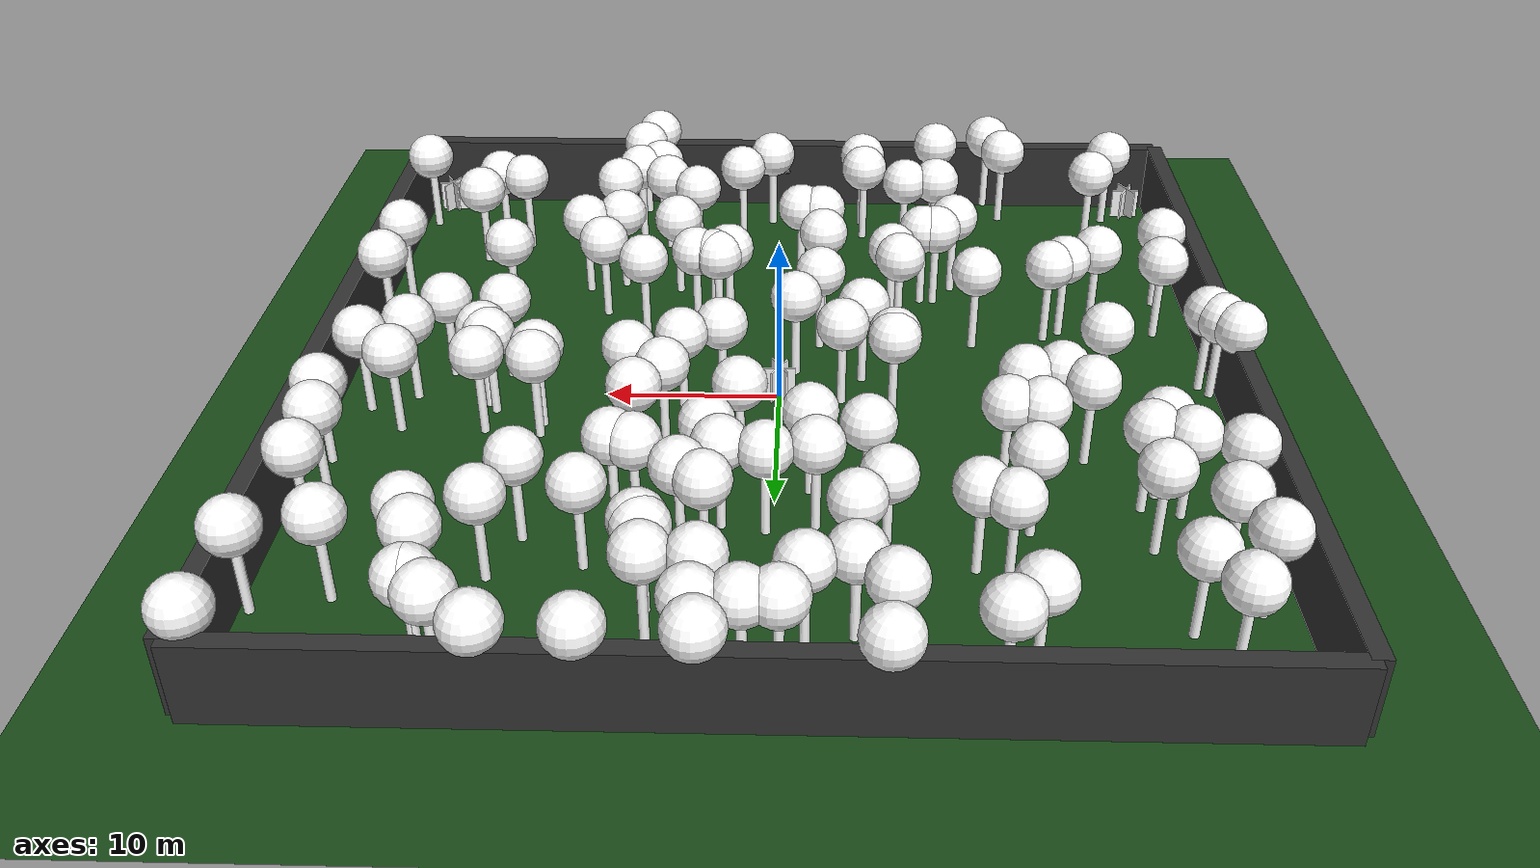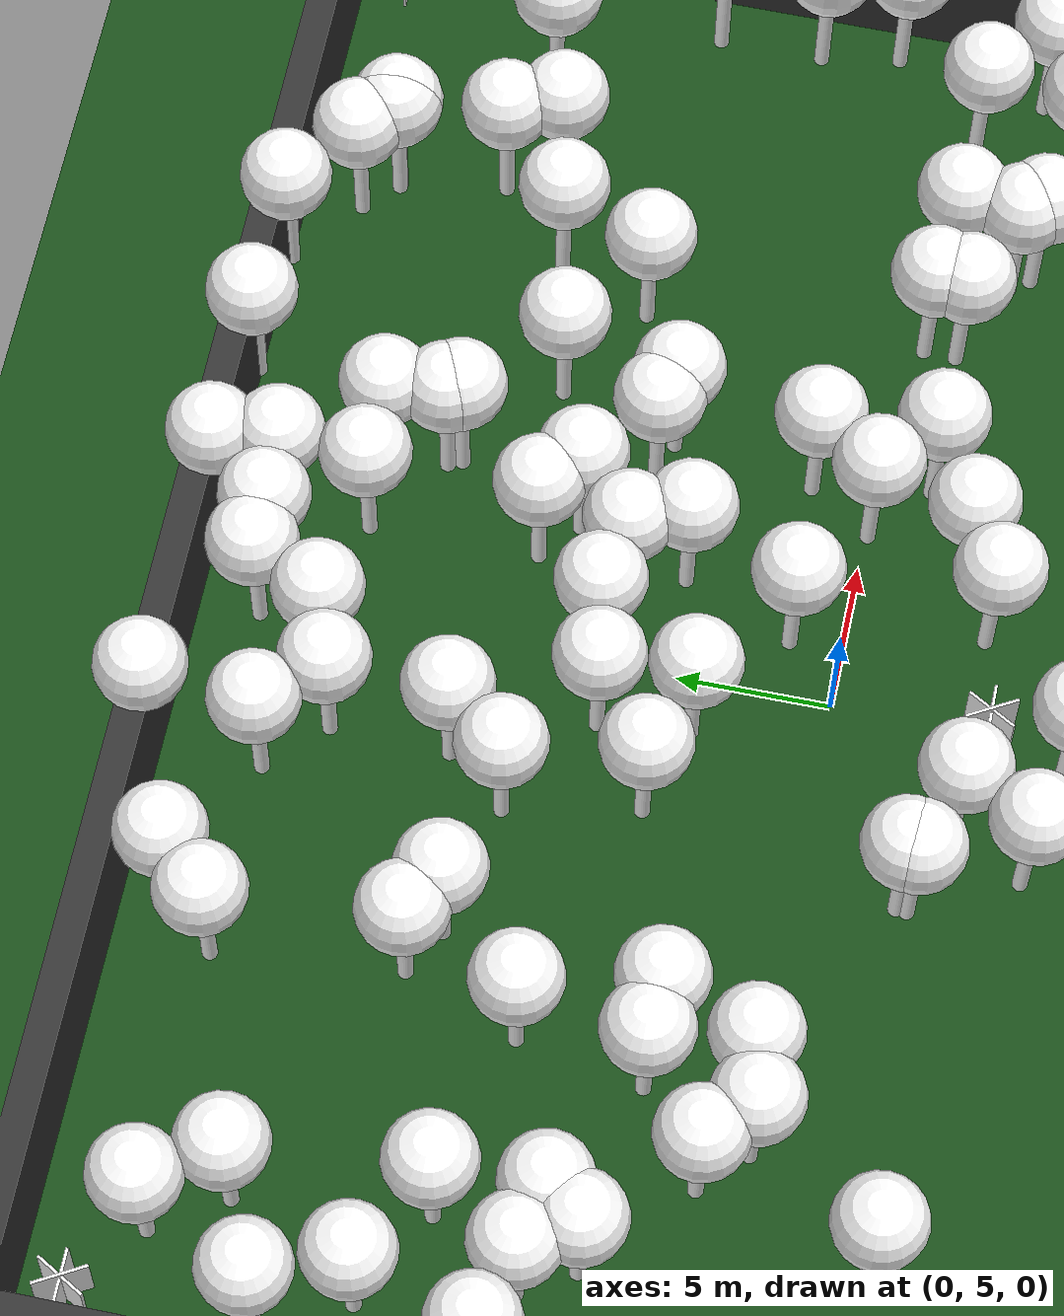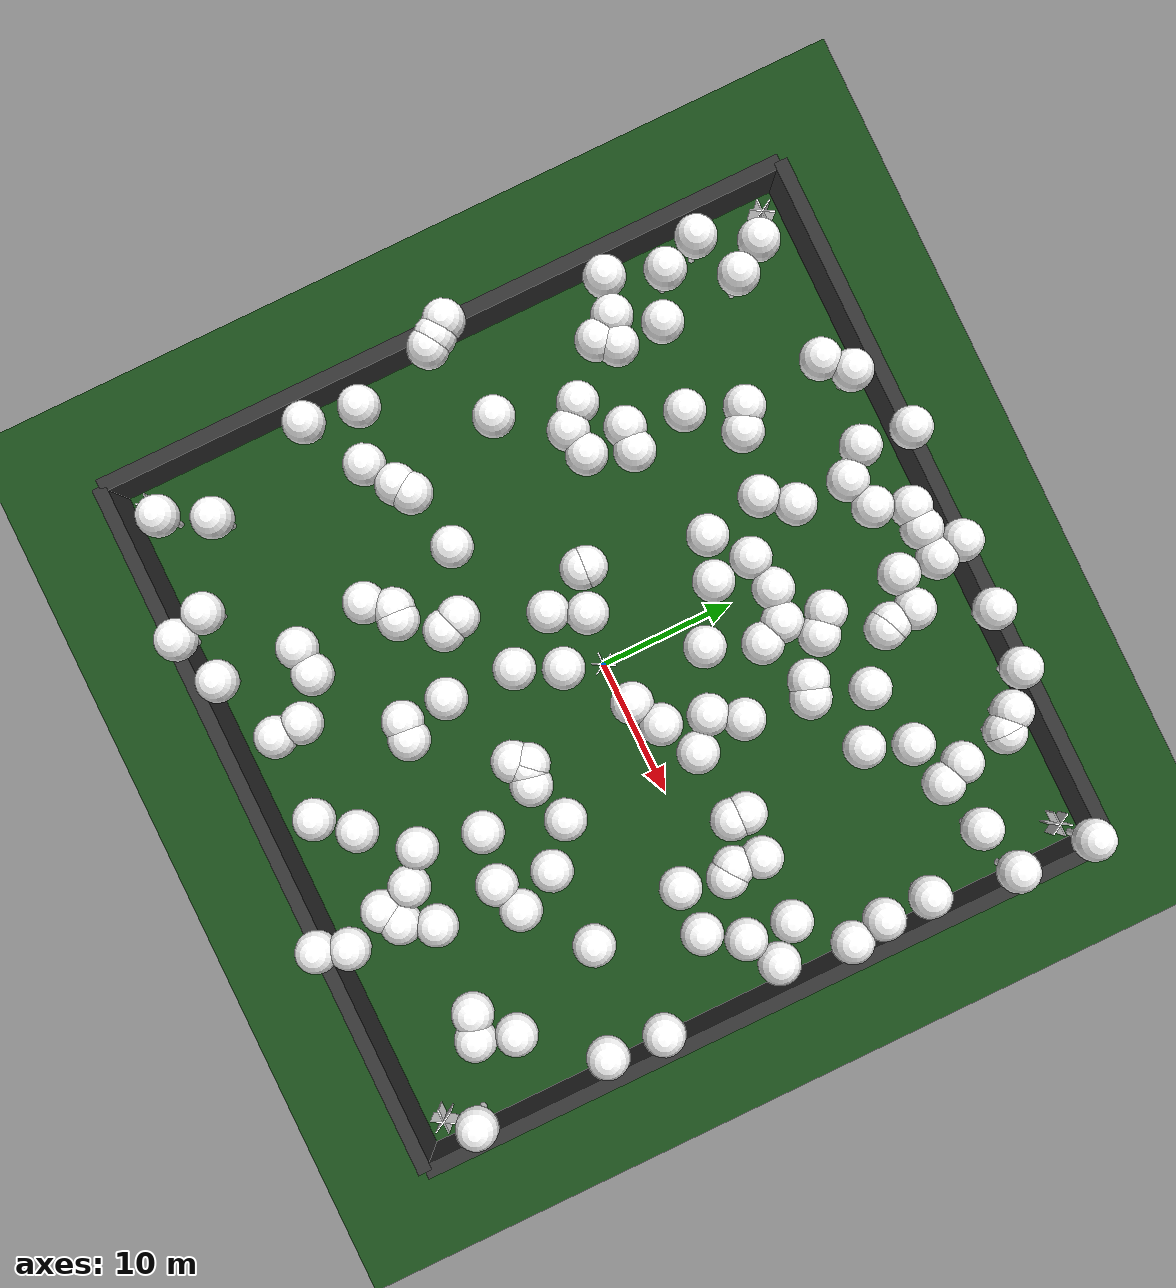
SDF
<?xml version='1.0' encoding='utf-8'?>
<sdf version="1.8">
  <world name="forest_world">

    <plugin filename="libignition-gazebo-physics-system.so" name="ignition::gazebo::systems::Physics">
    </plugin>
    <plugin filename="libignition-gazebo-user-commands-system.so" name="ignition::gazebo::systems::UserCommands">
    </plugin>
    <plugin filename="libignition-gazebo-scene-broadcaster-system.so" name="ignition::gazebo::systems::SceneBroadcaster">
    </plugin>
    <plugin filename="libignition-gazebo-sensors-system.so" name="ignition::gazebo::systems::Sensors">
    </plugin>

    <spherical_coordinates>
      <surface_model>EARTH_WGS84</surface_model>
      <latitude_deg>47.397743</latitude_deg>
      <longitude_deg>8.545594</longitude_deg>
      <elevation>0.0</elevation>
      <heading_deg>0</heading_deg>
    </spherical_coordinates>

    <physics name="1ms" type="ode">
      <gravity>0 0 -9.8066</gravity>
      <ode>
        <solver>
          <type>quick</type>
          <iters>50</iters>
          <sor>1.0</sor>
          <use_dynamic_moi_rescaling>0</use_dynamic_moi_rescaling>
        </solver>
        <constraints>
          <cfm>0</cfm>
          <erp>0.2</erp>
          <contact_max_correcting_vel>1000</contact_max_correcting_vel>
          <contact_surface_layer>0.001</contact_surface_layer>
        </constraints>
      </ode>
      <max_step_size>0.004</max_step_size>
      <real_time_factor>1</real_time_factor>
      <real_time_update_rate>250</real_time_update_rate>
      <magnetic_field>6.0e-06 2.3e-05 -4.2e-05</magnetic_field>
    </physics>

    <scene>
      <ambient>0.8 0.8 0.8</ambient>
      <background>0.9 0.95 1.0</background>
      <shadows>true</shadows>
      <fog>
        <color>0.9 0.9 0.95 1.0</color>
        <type>linear</type>
        <start>30</start>
        <end>150</end>
        <density>0.2</density>
      </fog>
      <grid>false</grid>
      <sky>
        <clouds>
          <speed>12</speed>
        </clouds>
      </sky>
    </scene>

    <light type="directional" name="forest_sun">
      <cast_shadows>true</cast_shadows>
      <pose>0 0 1000 -0.5 0.5 0</pose>
      <diffuse>1.0 1.0 0.95 1</diffuse>
      <specular>0.4 0.4 0.4 1</specular>
      <attenuation>
        <range>2000</range>
        <constant>0.7</constant>
        <linear>0.005</linear>
        <quadratic>0.0001</quadratic>
      </attenuation>
      <direction>-0.3 -0.3 -0.9</direction>
    </light>

    <light type="directional" name="ambient_fill">
      <cast_shadows>false</cast_shadows>
      <pose>0 0 500 0 0 0</pose>
      <diffuse>0.6 0.6 0.7 1</diffuse>
      <specular>0.2 0.2 0.2 1</specular>
      <direction>0 0 -1</direction>
    </light>

    <model name="fire_1"><pose>23.95 23.95 1.00 0 0 0.00</pose><static>true</static><link name="fire_link"><visual name="fire_1_fire_main_0"><pose>0.00 0.00 0.00 0 0 0.00</pose><geometry><box><size>1.80 0.10 2.00</size></box></geometry><material><ambient>0.7 0.35 0.0 1</ambient><diffuse>1 1 1 1</diffuse><specular>0 0 0 1</specular><emissive>0 0 0 1</emissive><pbr><metal><albedo_map>textures/fire.png</albedo_map><metalness>0.0</metalness><roughness>0.6</roughness></metal></pbr></material><transparency>0.0</transparency><cast_shadows>false</cast_shadows></visual><visual name="fire_1_fire_60_1"><pose>0.00 0.00 0.10 0 0 1.05</pose><geometry><box><size>1.80 0.10 2.00</size></box></geometry><material><ambient>0.7 0.35 0.0 1</ambient><diffuse>1 1 1 1</diffuse><specular>0 0 0 1</specular><emissive>0 0 0 1</emissive><pbr><metal><albedo_map>textures/fire.png</albedo_map><metalness>0.0</metalness><roughness>0.6</roughness></metal></pbr></material><transparency>0.0</transparency><cast_shadows>false</cast_shadows></visual><visual name="fire_1_fire_120_2"><pose>0.00 0.00 0.20 0 0 2.09</pose><geometry><box><size>1.80 0.10 2.00</size></box></geometry><material><ambient>0.7 0.35 0.0 1</ambient><diffuse>1 1 1 1</diffuse><specular>0 0 0 1</specular><emissive>0 0 0 1</emissive><pbr><metal><albedo_map>textures/fire.png</albedo_map><metalness>0.0</metalness><roughness>0.6</roughness></metal></pbr></material><transparency>0.0</transparency><cast_shadows>false</cast_shadows></visual><light type="point" name="fire_1_light_0"><pose>0.40 0.00 0.50 0 0 0</pose><diffuse>1.0 0.7 0.3 1</diffuse><specular>1.0 0.8 0.3 1</specular><intensity>2</intensity><attenuation><range>2</range><constant>0.1</constant><linear>0.05</linear><quadratic>0.02</quadratic></attenuation><cast_shadows>false</cast_shadows></light><light type="point" name="fire_1_light_1"><pose>-0.20 0.35 0.50 0 0 0</pose><diffuse>1.0 0.7 0.3 1</diffuse><specular>1.0 0.8 0.3 1</specular><intensity>2</intensity><attenuation><range>2</range><constant>0.1</constant><linear>0.05</linear><quadratic>0.02</quadratic></attenuation><cast_shadows>false</cast_shadows></light><light type="point" name="fire_1_light_2"><pose>-0.20 -0.35 0.50 0 0 0</pose><diffuse>1.0 0.7 0.3 1</diffuse><specular>1.0 0.8 0.3 1</specular><intensity>2</intensity><attenuation><range>2</range><constant>0.1</constant><linear>0.05</linear><quadratic>0.02</quadratic></attenuation><cast_shadows>false</cast_shadows></light></link><plugin filename="libignition-gazebo-pose-publisher-system.so" name="ignition::gazebo::systems::PosePublisher"><frame_id>world</frame_id><publish_link_pose>true</publish_link_pose><use_pose_vector_msg>true</use_pose_vector_msg><static_publisher>true</static_publisher><static_update_frequency>1</static_update_frequency></plugin></model><model name="fire_2"><pose>-23.95 23.95 1.00 0 0 0.00</pose><static>true</static><link name="fire_link"><visual name="fire_2_fire_main_0"><pose>0.00 0.00 0.00 0 0 0.00</pose><geometry><box><size>1.80 0.10 2.00</size></box></geometry><material><ambient>0.7 0.35 0.0 1</ambient><diffuse>1 1 1 1</diffuse><specular>0 0 0 1</specular><emissive>0 0 0 1</emissive><pbr><metal><albedo_map>textures/fire.png</albedo_map><metalness>0.0</metalness><roughness>0.6</roughness></metal></pbr></material><transparency>0.0</transparency><cast_shadows>false</cast_shadows></visual><visual name="fire_2_fire_60_1"><pose>0.00 0.00 0.10 0 0 1.05</pose><geometry><box><size>1.80 0.10 2.00</size></box></geometry><material><ambient>0.7 0.35 0.0 1</ambient><diffuse>1 1 1 1</diffuse><specular>0 0 0 1</specular><emissive>0 0 0 1</emissive><pbr><metal><albedo_map>textures/fire.png</albedo_map><metalness>0.0</metalness><roughness>0.6</roughness></metal></pbr></material><transparency>0.0</transparency><cast_shadows>false</cast_shadows></visual><visual name="fire_2_fire_120_2"><pose>0.00 0.00 0.20 0 0 2.09</pose><geometry><box><size>1.80 0.10 2.00</size></box></geometry><material><ambient>0.7 0.35 0.0 1</ambient><diffuse>1 1 1 1</diffuse><specular>0 0 0 1</specular><emissive>0 0 0 1</emissive><pbr><metal><albedo_map>textures/fire.png</albedo_map><metalness>0.0</metalness><roughness>0.6</roughness></metal></pbr></material><transparency>0.0</transparency><cast_shadows>false</cast_shadows></visual><light type="point" name="fire_2_light_0"><pose>0.40 0.00 0.50 0 0 0</pose><diffuse>1.0 0.7 0.3 1</diffuse><specular>1.0 0.8 0.3 1</specular><intensity>2</intensity><attenuation><range>2</range><constant>0.1</constant><linear>0.05</linear><quadratic>0.02</quadratic></attenuation><cast_shadows>false</cast_shadows></light><light type="point" name="fire_2_light_1"><pose>-0.20 0.35 0.50 0 0 0</pose><diffuse>1.0 0.7 0.3 1</diffuse><specular>1.0 0.8 0.3 1</specular><intensity>2</intensity><attenuation><range>2</range><constant>0.1</constant><linear>0.05</linear><quadratic>0.02</quadratic></attenuation><cast_shadows>false</cast_shadows></light><light type="point" name="fire_2_light_2"><pose>-0.20 -0.35 0.50 0 0 0</pose><diffuse>1.0 0.7 0.3 1</diffuse><specular>1.0 0.8 0.3 1</specular><intensity>2</intensity><attenuation><range>2</range><constant>0.1</constant><linear>0.05</linear><quadratic>0.02</quadratic></attenuation><cast_shadows>false</cast_shadows></light></link><plugin filename="libignition-gazebo-pose-publisher-system.so" name="ignition::gazebo::systems::PosePublisher"><frame_id>world</frame_id><publish_link_pose>true</publish_link_pose><use_pose_vector_msg>true</use_pose_vector_msg><static_publisher>true</static_publisher><static_update_frequency>1</static_update_frequency></plugin></model><model name="fire_3"><pose>23.95 -23.95 1.00 0 0 0.00</pose><static>true</static><link name="fire_link"><visual name="fire_3_fire_main_0"><pose>0.00 0.00 0.00 0 0 0.00</pose><geometry><box><size>1.80 0.10 2.00</size></box></geometry><material><ambient>0.7 0.35 0.0 1</ambient><diffuse>1 1 1 1</diffuse><specular>0 0 0 1</specular><emissive>0 0 0 1</emissive><pbr><metal><albedo_map>textures/fire.png</albedo_map><metalness>0.0</metalness><roughness>0.6</roughness></metal></pbr></material><transparency>0.0</transparency><cast_shadows>false</cast_shadows></visual><visual name="fire_3_fire_60_1"><pose>0.00 0.00 0.10 0 0 1.05</pose><geometry><box><size>1.80 0.10 2.00</size></box></geometry><material><ambient>0.7 0.35 0.0 1</ambient><diffuse>1 1 1 1</diffuse><specular>0 0 0 1</specular><emissive>0 0 0 1</emissive><pbr><metal><albedo_map>textures/fire.png</albedo_map><metalness>0.0</metalness><roughness>0.6</roughness></metal></pbr></material><transparency>0.0</transparency><cast_shadows>false</cast_shadows></visual><visual name="fire_3_fire_120_2"><pose>0.00 0.00 0.20 0 0 2.09</pose><geometry><box><size>1.80 0.10 2.00</size></box></geometry><material><ambient>0.7 0.35 0.0 1</ambient><diffuse>1 1 1 1</diffuse><specular>0 0 0 1</specular><emissive>0 0 0 1</emissive><pbr><metal><albedo_map>textures/fire.png</albedo_map><metalness>0.0</metalness><roughness>0.6</roughness></metal></pbr></material><transparency>0.0</transparency><cast_shadows>false</cast_shadows></visual><light type="point" name="fire_3_light_0"><pose>0.40 0.00 0.50 0 0 0</pose><diffuse>1.0 0.7 0.3 1</diffuse><specular>1.0 0.8 0.3 1</specular><intensity>2</intensity><attenuation><range>2</range><constant>0.1</constant><linear>0.05</linear><quadratic>0.02</quadratic></attenuation><cast_shadows>false</cast_shadows></light><light type="point" name="fire_3_light_1"><pose>-0.20 0.35 0.50 0 0 0</pose><diffuse>1.0 0.7 0.3 1</diffuse><specular>1.0 0.8 0.3 1</specular><intensity>2</intensity><attenuation><range>2</range><constant>0.1</constant><linear>0.05</linear><quadratic>0.02</quadratic></attenuation><cast_shadows>false</cast_shadows></light><light type="point" name="fire_3_light_2"><pose>-0.20 -0.35 0.50 0 0 0</pose><diffuse>1.0 0.7 0.3 1</diffuse><specular>1.0 0.8 0.3 1</specular><intensity>2</intensity><attenuation><range>2</range><constant>0.1</constant><linear>0.05</linear><quadratic>0.02</quadratic></attenuation><cast_shadows>false</cast_shadows></light></link><plugin filename="libignition-gazebo-pose-publisher-system.so" name="ignition::gazebo::systems::PosePublisher"><frame_id>world</frame_id><publish_link_pose>true</publish_link_pose><use_pose_vector_msg>true</use_pose_vector_msg><static_publisher>true</static_publisher><static_update_frequency>1</static_update_frequency></plugin></model><model name="fire_4"><pose>-23.95 -23.95 1.00 0 0 0.00</pose><static>true</static><link name="fire_link"><visual name="fire_4_fire_main_0"><pose>0.00 0.00 0.00 0 0 0.00</pose><geometry><box><size>1.80 0.10 2.00</size></box></geometry><material><ambient>0.7 0.35 0.0 1</ambient><diffuse>1 1 1 1</diffuse><specular>0 0 0 1</specular><emissive>0 0 0 1</emissive><pbr><metal><albedo_map>textures/fire.png</albedo_map><metalness>0.0</metalness><roughness>0.6</roughness></metal></pbr></material><transparency>0.0</transparency><cast_shadows>false</cast_shadows></visual><visual name="fire_4_fire_60_1"><pose>0.00 0.00 0.10 0 0 1.05</pose><geometry><box><size>1.80 0.10 2.00</size></box></geometry><material><ambient>0.7 0.35 0.0 1</ambient><diffuse>1 1 1 1</diffuse><specular>0 0 0 1</specular><emissive>0 0 0 1</emissive><pbr><metal><albedo_map>textures/fire.png</albedo_map><metalness>0.0</metalness><roughness>0.6</roughness></metal></pbr></material><transparency>0.0</transparency><cast_shadows>false</cast_shadows></visual><visual name="fire_4_fire_120_2"><pose>0.00 0.00 0.20 0 0 2.09</pose><geometry><box><size>1.80 0.10 2.00</size></box></geometry><material><ambient>0.7 0.35 0.0 1</ambient><diffuse>1 1 1 1</diffuse><specular>0 0 0 1</specular><emissive>0 0 0 1</emissive><pbr><metal><albedo_map>textures/fire.png</albedo_map><metalness>0.0</metalness><roughness>0.6</roughness></metal></pbr></material><transparency>0.0</transparency><cast_shadows>false</cast_shadows></visual><light type="point" name="fire_4_light_0"><pose>0.40 0.00 0.50 0 0 0</pose><diffuse>1.0 0.7 0.3 1</diffuse><specular>1.0 0.8 0.3 1</specular><intensity>2</intensity><attenuation><range>2</range><constant>0.1</constant><linear>0.05</linear><quadratic>0.02</quadratic></attenuation><cast_shadows>false</cast_shadows></light><light type="point" name="fire_4_light_1"><pose>-0.20 0.35 0.50 0 0 0</pose><diffuse>1.0 0.7 0.3 1</diffuse><specular>1.0 0.8 0.3 1</specular><intensity>2</intensity><attenuation><range>2</range><constant>0.1</constant><linear>0.05</linear><quadratic>0.02</quadratic></attenuation><cast_shadows>false</cast_shadows></light><light type="point" name="fire_4_light_2"><pose>-0.20 -0.35 0.50 0 0 0</pose><diffuse>1.0 0.7 0.3 1</diffuse><specular>1.0 0.8 0.3 1</specular><intensity>2</intensity><attenuation><range>2</range><constant>0.1</constant><linear>0.05</linear><quadratic>0.02</quadratic></attenuation><cast_shadows>false</cast_shadows></light></link><plugin filename="libignition-gazebo-pose-publisher-system.so" name="ignition::gazebo::systems::PosePublisher"><frame_id>world</frame_id><publish_link_pose>true</publish_link_pose><use_pose_vector_msg>true</use_pose_vector_msg><static_publisher>true</static_publisher><static_update_frequency>1</static_update_frequency></plugin></model><model name="fire_5"><pose>0.00 0.00 1.00 0 0 0.00</pose><static>true</static><link name="fire_link"><visual name="fire_5_fire_main_0"><pose>0.00 0.00 0.00 0 0 0.00</pose><geometry><box><size>1.80 0.10 2.00</size></box></geometry><material><ambient>0.7 0.35 0.0 1</ambient><diffuse>1 1 1 1</diffuse><specular>0 0 0 1</specular><emissive>0 0 0 1</emissive><pbr><metal><albedo_map>textures/fire.png</albedo_map><metalness>0.0</metalness><roughness>0.6</roughness></metal></pbr></material><transparency>0.0</transparency><cast_shadows>false</cast_shadows></visual><visual name="fire_5_fire_60_1"><pose>0.00 0.00 0.10 0 0 1.05</pose><geometry><box><size>1.80 0.10 2.00</size></box></geometry><material><ambient>0.7 0.35 0.0 1</ambient><diffuse>1 1 1 1</diffuse><specular>0 0 0 1</specular><emissive>0 0 0 1</emissive><pbr><metal><albedo_map>textures/fire.png</albedo_map><metalness>0.0</metalness><roughness>0.6</roughness></metal></pbr></material><transparency>0.0</transparency><cast_shadows>false</cast_shadows></visual><visual name="fire_5_fire_120_2"><pose>0.00 0.00 0.20 0 0 2.09</pose><geometry><box><size>1.80 0.10 2.00</size></box></geometry><material><ambient>0.7 0.35 0.0 1</ambient><diffuse>1 1 1 1</diffuse><specular>0 0 0 1</specular><emissive>0 0 0 1</emissive><pbr><metal><albedo_map>textures/fire.png</albedo_map><metalness>0.0</metalness><roughness>0.6</roughness></metal></pbr></material><transparency>0.0</transparency><cast_shadows>false</cast_shadows></visual><light type="point" name="fire_5_light_0"><pose>0.40 0.00 0.50 0 0 0</pose><diffuse>1.0 0.7 0.3 1</diffuse><specular>1.0 0.8 0.3 1</specular><intensity>2</intensity><attenuation><range>2</range><constant>0.1</constant><linear>0.05</linear><quadratic>0.02</quadratic></attenuation><cast_shadows>false</cast_shadows></light><light type="point" name="fire_5_light_1"><pose>-0.20 0.35 0.50 0 0 0</pose><diffuse>1.0 0.7 0.3 1</diffuse><specular>1.0 0.8 0.3 1</specular><intensity>2</intensity><attenuation><range>2</range><constant>0.1</constant><linear>0.05</linear><quadratic>0.02</quadratic></attenuation><cast_shadows>false</cast_shadows></light><light type="point" name="fire_5_light_2"><pose>-0.20 -0.35 0.50 0 0 0</pose><diffuse>1.0 0.7 0.3 1</diffuse><specular>1.0 0.8 0.3 1</specular><intensity>2</intensity><attenuation><range>2</range><constant>0.1</constant><linear>0.05</linear><quadratic>0.02</quadratic></attenuation><cast_shadows>false</cast_shadows></light></link><plugin filename="libignition-gazebo-pose-publisher-system.so" name="ignition::gazebo::systems::PosePublisher"><frame_id>world</frame_id><publish_link_pose>true</publish_link_pose><use_pose_vector_msg>true</use_pose_vector_msg><static_publisher>true</static_publisher><static_update_frequency>1</static_update_frequency></plugin></model><model name="tree_simple498">
      <static>1</static>
      <link name="link">
        <pose>0 0 0.1 0 -0 0</pose>
        <collision name="collision_trunk">
          <pose>0 0 2 0 -0 0</pose>
          <geometry>
            <cylinder>
              <radius>0.25</radius>
              <length>4</length>
            </cylinder>
          </geometry>
        </collision>
        <collision name="collision_treetop">
          <pose>0 0 5.2 0 -0 0</pose>
          <geometry>
            <sphere>
              <radius>1.5</radius>
            </sphere>
          </geometry>
        </collision>
        <visual name="trunk">
          <pose>0 0 2 0 -0 0</pose>
          <geometry>
            <cylinder>
              <radius>0.25</radius>
              <length>4</length>
            </cylinder>
          </geometry>
          <material>
            <ambient>0.5 0.5 0.5 1</ambient>
            <diffuse>1.0 1.0 1.0 1</diffuse>
            <specular>0.0 0.0 0.0 1</specular>
            <pbr>
              <metal>
                <albedo_map>../worlds/textures/tree_simple_trunk.jpg</albedo_map>
                <metalness>0.0</metalness>
                <roughness>0.8</roughness>
              </metal>
            </pbr>
          </material>
        </visual>
        <visual name="treetop">
          <pose>0 0 5.2 0 -0 0</pose>
          <geometry>
            <sphere>
              <radius>1.5</radius>
            </sphere>
          </geometry>
          <material>
            <ambient>0.5 0.5 0.5 1</ambient>
            <diffuse>1.0 1.0 1.0 1</diffuse>
            <specular>0.0 0.0 0.0 1</specular>
            <pbr>
              <metal>
                <albedo_map>../worlds/textures/tree_simple_treetop.jpg</albedo_map>
                <metalness>0.0</metalness>
                <roughness>0.9</roughness>
              </metal>
            </pbr>
          </material>
        </visual>
        <self_collide>0</self_collide>
        <kinematic>0</kinematic>
      </link>
      <pose>-20.062069779 9.09254194943 0 0 -0 0</pose>
    </model>

    <model name="tree_simple497">
      <static>1</static>
      <link name="link">
        <pose>0 0 0.1 0 -0 0</pose>
        <collision name="collision_trunk">
          <pose>0 0 2 0 -0 0</pose>
          <geometry>
            <cylinder>
              <radius>0.25</radius>
              <length>4</length>
            </cylinder>
          </geometry>
        </collision>
        <collision name="collision_treetop">
          <pose>0 0 5.2 0 -0 0</pose>
          <geometry>
            <sphere>
              <radius>1.5</radius>
            </sphere>
          </geometry>
        </collision>
        <visual name="trunk">
          <pose>0 0 2 0 -0 0</pose>
          <geometry>
            <cylinder>
              <radius>0.25</radius>
              <length>4</length>
            </cylinder>
          </geometry>
          <material>
            <ambient>0.5 0.5 0.5 1</ambient>
            <diffuse>1.0 1.0 1.0 1</diffuse>
            <specular>0.0 0.0 0.0 1</specular>
            <pbr>
              <metal>
                <albedo_map>../worlds/textures/tree_simple_trunk.jpg</albedo_map>
                <metalness>0.0</metalness>
                <roughness>0.8</roughness>
              </metal>
            </pbr>
          </material>
        </visual>
        <visual name="treetop">
          <pose>0 0 5.2 0 -0 0</pose>
          <geometry>
            <sphere>
              <radius>1.5</radius>
            </sphere>
          </geometry>
          <material>
            <ambient>0.5 0.5 0.5 1</ambient>
            <diffuse>1.0 1.0 1.0 1</diffuse>
            <specular>0.0 0.0 0.0 1</specular>
            <pbr>
              <metal>
                <albedo_map>../worlds/textures/tree_simple_treetop.jpg</albedo_map>
                <metalness>0.0</metalness>
                <roughness>0.9</roughness>
              </metal>
            </pbr>
          </material>
        </visual>
        <self_collide>0</self_collide>
        <kinematic>0</kinematic>
      </link>
      <pose>16.5730666381 19.0016793819 0 0 -0 0</pose>
    </model>

    <model name="tree_simple495">
      <static>1</static>
      <link name="link">
        <pose>0 0 0.1 0 -0 0</pose>
        <collision name="collision_trunk">
          <pose>0 0 2 0 -0 0</pose>
          <geometry>
            <cylinder>
              <radius>0.25</radius>
              <length>4</length>
            </cylinder>
          </geometry>
        </collision>
        <collision name="collision_treetop">
          <pose>0 0 5.2 0 -0 0</pose>
          <geometry>
            <sphere>
              <radius>1.5</radius>
            </sphere>
          </geometry>
        </collision>
        <visual name="trunk">
          <pose>0 0 2 0 -0 0</pose>
          <geometry>
            <cylinder>
              <radius>0.25</radius>
              <length>4</length>
            </cylinder>
          </geometry>
          <material>
            <ambient>0.5 0.5 0.5 1</ambient>
            <diffuse>1.0 1.0 1.0 1</diffuse>
            <specular>0.0 0.0 0.0 1</specular>
            <pbr>
              <metal>
                <albedo_map>../worlds/textures/tree_simple_trunk.jpg</albedo_map>
                <metalness>0.0</metalness>
                <roughness>0.8</roughness>
              </metal>
            </pbr>
          </material>
        </visual>
        <visual name="treetop">
          <pose>0 0 5.2 0 -0 0</pose>
          <geometry>
            <sphere>
              <radius>1.5</radius>
            </sphere>
          </geometry>
          <material>
            <ambient>0.5 0.5 0.5 1</ambient>
            <diffuse>1.0 1.0 1.0 1</diffuse>
            <specular>0.0 0.0 0.0 1</specular>
            <pbr>
              <metal>
                <albedo_map>../worlds/textures/tree_simple_treetop.jpg</albedo_map>
                <metalness>0.0</metalness>
                <roughness>0.9</roughness>
              </metal>
            </pbr>
          </material>
        </visual>
        <self_collide>0</self_collide>
        <kinematic>0</kinematic>
      </link>
      <pose>13.2663357304 3.23501246435 0 0 -0 0</pose>
    </model>

    <model name="tree_simple488">
      <static>1</static>
      <link name="link">
        <pose>0 0 0.1 0 -0 0</pose>
        <collision name="collision_trunk">
          <pose>0 0 2 0 -0 0</pose>
          <geometry>
            <cylinder>
              <radius>0.25</radius>
              <length>4</length>
            </cylinder>
          </geometry>
        </collision>
        <collision name="collision_treetop">
          <pose>0 0 5.2 0 -0 0</pose>
          <geometry>
            <sphere>
              <radius>1.5</radius>
            </sphere>
          </geometry>
        </collision>
        <visual name="trunk">
          <pose>0 0 2 0 -0 0</pose>
          <geometry>
            <cylinder>
              <radius>0.25</radius>
              <length>4</length>
            </cylinder>
          </geometry>
          <material>
            <ambient>0.5 0.5 0.5 1</ambient>
            <diffuse>1.0 1.0 1.0 1</diffuse>
            <specular>0.0 0.0 0.0 1</specular>
            <pbr>
              <metal>
                <albedo_map>../worlds/textures/tree_simple_trunk.jpg</albedo_map>
                <metalness>0.0</metalness>
                <roughness>0.8</roughness>
              </metal>
            </pbr>
          </material>
        </visual>
        <visual name="treetop">
          <pose>0 0 5.2 0 -0 0</pose>
          <geometry>
            <sphere>
              <radius>1.5</radius>
            </sphere>
          </geometry>
          <material>
            <ambient>0.5 0.5 0.5 1</ambient>
            <diffuse>1.0 1.0 1.0 1</diffuse>
            <specular>0.0 0.0 0.0 1</specular>
            <pbr>
              <metal>
                <albedo_map>../worlds/textures/tree_simple_treetop.jpg</albedo_map>
                <metalness>0.0</metalness>
                <roughness>0.9</roughness>
              </metal>
            </pbr>
          </material>
        </visual>
        <self_collide>0</self_collide>
        <kinematic>0</kinematic>
      </link>
      <pose>-13.1215818691 12.435953241 0 0 -0 0</pose>
    </model>

    <model name="tree_simple486">
      <static>1</static>
      <link name="link">
        <pose>0 0 0.1 0 -0 0</pose>
        <collision name="collision_trunk">
          <pose>0 0 2 0 -0 0</pose>
          <geometry>
            <cylinder>
              <radius>0.25</radius>
              <length>4</length>
            </cylinder>
          </geometry>
        </collision>
        <collision name="collision_treetop">
          <pose>0 0 5.2 0 -0 0</pose>
          <geometry>
            <sphere>
              <radius>1.5</radius>
            </sphere>
          </geometry>
        </collision>
        <visual name="trunk">
          <pose>0 0 2 0 -0 0</pose>
          <geometry>
            <cylinder>
              <radius>0.25</radius>
              <length>4</length>
            </cylinder>
          </geometry>
          <material>
            <ambient>0.5 0.5 0.5 1</ambient>
            <diffuse>1.0 1.0 1.0 1</diffuse>
            <specular>0.0 0.0 0.0 1</specular>
            <pbr>
              <metal>
                <albedo_map>../worlds/textures/tree_simple_trunk.jpg</albedo_map>
                <metalness>0.0</metalness>
                <roughness>0.8</roughness>
              </metal>
            </pbr>
          </material>
        </visual>
        <visual name="treetop">
          <pose>0 0 5.2 0 -0 0</pose>
          <geometry>
            <sphere>
              <radius>1.5</radius>
            </sphere>
          </geometry>
          <material>
            <ambient>0.5 0.5 0.5 1</ambient>
            <diffuse>1.0 1.0 1.0 1</diffuse>
            <specular>0.0 0.0 0.0 1</specular>
            <pbr>
              <metal>
                <albedo_map>../worlds/textures/tree_simple_treetop.jpg</albedo_map>
                <metalness>0.0</metalness>
                <roughness>0.9</roughness>
              </metal>
            </pbr>
          </material>
        </visual>
        <self_collide>0</self_collide>
        <kinematic>0</kinematic>
      </link>
      <pose>8.18281559396 11.6524151823 0 0 -0 0</pose>
    </model>

    <model name="tree_simple480">
      <static>1</static>
      <link name="link">
        <pose>0 0 0.1 0 -0 0</pose>
        <collision name="collision_trunk">
          <pose>0 0 2 0 -0 0</pose>
          <geometry>
            <cylinder>
              <radius>0.25</radius>
              <length>4</length>
            </cylinder>
          </geometry>
        </collision>
        <collision name="collision_treetop">
          <pose>0 0 5.2 0 -0 0</pose>
          <geometry>
            <sphere>
              <radius>1.5</radius>
            </sphere>
          </geometry>
        </collision>
        <visual name="trunk">
          <pose>0 0 2 0 -0 0</pose>
          <geometry>
            <cylinder>
              <radius>0.25</radius>
              <length>4</length>
            </cylinder>
          </geometry>
          <material>
            <ambient>0.5 0.5 0.5 1</ambient>
            <diffuse>1.0 1.0 1.0 1</diffuse>
            <specular>0.0 0.0 0.0 1</specular>
            <pbr>
              <metal>
                <albedo_map>../worlds/textures/tree_simple_trunk.jpg</albedo_map>
                <metalness>0.0</metalness>
                <roughness>0.8</roughness>
              </metal>
            </pbr>
          </material>
        </visual>
        <visual name="treetop">
          <pose>0 0 5.2 0 -0 0</pose>
          <geometry>
            <sphere>
              <radius>1.5</radius>
            </sphere>
          </geometry>
          <material>
            <ambient>0.5 0.5 0.5 1</ambient>
            <diffuse>1.0 1.0 1.0 1</diffuse>
            <specular>0.0 0.0 0.0 1</specular>
            <pbr>
              <metal>
                <albedo_map>../worlds/textures/tree_simple_treetop.jpg</albedo_map>
                <metalness>0.0</metalness>
                <roughness>0.9</roughness>
              </metal>
            </pbr>
          </material>
        </visual>
        <self_collide>0</self_collide>
        <kinematic>0</kinematic>
      </link>
      <pose>-2.16211412072 12.1351070175 0 0 -0 0</pose>
    </model>

    <model name="tree_simple479">
      <static>1</static>
      <link name="link">
        <pose>0 0 0.1 0 -0 0</pose>
        <collision name="collision_trunk">
          <pose>0 0 2 0 -0 0</pose>
          <geometry>
            <cylinder>
              <radius>0.25</radius>
              <length>4</length>
            </cylinder>
          </geometry>
        </collision>
        <collision name="collision_treetop">
          <pose>0 0 5.2 0 -0 0</pose>
          <geometry>
            <sphere>
              <radius>1.5</radius>
            </sphere>
          </geometry>
        </collision>
        <visual name="trunk">
          <pose>0 0 2 0 -0 0</pose>
          <geometry>
            <cylinder>
              <radius>0.25</radius>
              <length>4</length>
            </cylinder>
          </geometry>
          <material>
            <ambient>0.5 0.5 0.5 1</ambient>
            <diffuse>1.0 1.0 1.0 1</diffuse>
            <specular>0.0 0.0 0.0 1</specular>
            <pbr>
              <metal>
                <albedo_map>../worlds/textures/tree_simple_trunk.jpg</albedo_map>
                <metalness>0.0</metalness>
                <roughness>0.8</roughness>
              </metal>
            </pbr>
          </material>
        </visual>
        <visual name="treetop">
          <pose>0 0 5.2 0 -0 0</pose>
          <geometry>
            <sphere>
              <radius>1.5</radius>
            </sphere>
          </geometry>
          <material>
            <ambient>0.5 0.5 0.5 1</ambient>
            <diffuse>1.0 1.0 1.0 1</diffuse>
            <specular>0.0 0.0 0.0 1</specular>
            <pbr>
              <metal>
                <albedo_map>../worlds/textures/tree_simple_treetop.jpg</albedo_map>
                <metalness>0.0</metalness>
                <roughness>0.9</roughness>
              </metal>
            </pbr>
          </material>
        </visual>
        <self_collide>0</self_collide>
        <kinematic>0</kinematic>
      </link>
      <pose>-12.2778199556 22.3020251283 0 0 -0 0</pose>
    </model>

    <model name="tree_simple478">
      <static>1</static>
      <link name="link">
        <pose>0 0 0.1 0 -0 0</pose>
        <collision name="collision_trunk">
          <pose>0 0 2 0 -0 0</pose>
          <geometry>
            <cylinder>
              <radius>0.25</radius>
              <length>4</length>
            </cylinder>
          </geometry>
        </collision>
        <collision name="collision_treetop">
          <pose>0 0 5.2 0 -0 0</pose>
          <geometry>
            <sphere>
              <radius>1.5</radius>
            </sphere>
          </geometry>
        </collision>
        <visual name="trunk">
          <pose>0 0 2 0 -0 0</pose>
          <geometry>
            <cylinder>
              <radius>0.25</radius>
              <length>4</length>
            </cylinder>
          </geometry>
          <material>
            <ambient>0.5 0.5 0.5 1</ambient>
            <diffuse>1.0 1.0 1.0 1</diffuse>
            <specular>0.0 0.0 0.0 1</specular>
            <pbr>
              <metal>
                <albedo_map>../worlds/textures/tree_simple_trunk.jpg</albedo_map>
                <metalness>0.0</metalness>
                <roughness>0.8</roughness>
              </metal>
            </pbr>
          </material>
        </visual>
        <visual name="treetop">
          <pose>0 0 5.2 0 -0 0</pose>
          <geometry>
            <sphere>
              <radius>1.5</radius>
            </sphere>
          </geometry>
          <material>
            <ambient>0.5 0.5 0.5 1</ambient>
            <diffuse>1.0 1.0 1.0 1</diffuse>
            <specular>0.0 0.0 0.0 1</specular>
            <pbr>
              <metal>
                <albedo_map>../worlds/textures/tree_simple_treetop.jpg</albedo_map>
                <metalness>0.0</metalness>
                <roughness>0.9</roughness>
              </metal>
            </pbr>
          </material>
        </visual>
        <self_collide>0</self_collide>
        <kinematic>0</kinematic>
      </link>
      <pose>6.74093075138 -12.3162984353 0 0 -0 0</pose>
    </model>

    <model name="tree_simple472">
      <static>1</static>
      <link name="link">
        <pose>0 0 0.1 0 -0 0</pose>
        <collision name="collision_trunk">
          <pose>0 0 2 0 -0 0</pose>
          <geometry>
            <cylinder>
              <radius>0.25</radius>
              <length>4</length>
            </cylinder>
          </geometry>
        </collision>
        <collision name="collision_treetop">
          <pose>0 0 5.2 0 -0 0</pose>
          <geometry>
            <sphere>
              <radius>1.5</radius>
            </sphere>
          </geometry>
        </collision>
        <visual name="trunk">
          <pose>0 0 2 0 -0 0</pose>
          <geometry>
            <cylinder>
              <radius>0.25</radius>
              <length>4</length>
            </cylinder>
          </geometry>
          <material>
            <ambient>0.5 0.5 0.5 1</ambient>
            <diffuse>1.0 1.0 1.0 1</diffuse>
            <specular>0.0 0.0 0.0 1</specular>
            <pbr>
              <metal>
                <albedo_map>../worlds/textures/tree_simple_trunk.jpg</albedo_map>
                <metalness>0.0</metalness>
                <roughness>0.8</roughness>
              </metal>
            </pbr>
          </material>
        </visual>
        <visual name="treetop">
          <pose>0 0 5.2 0 -0 0</pose>
          <geometry>
            <sphere>
              <radius>1.5</radius>
            </sphere>
          </geometry>
          <material>
            <ambient>0.5 0.5 0.5 1</ambient>
            <diffuse>1.0 1.0 1.0 1</diffuse>
            <specular>0.0 0.0 0.0 1</specular>
            <pbr>
              <metal>
                <albedo_map>../worlds/textures/tree_simple_treetop.jpg</albedo_map>
                <metalness>0.0</metalness>
                <roughness>0.9</roughness>
              </metal>
            </pbr>
          </material>
        </visual>
        <self_collide>0</self_collide>
        <kinematic>0</kinematic>
      </link>
      <pose>9.92228677952 -23.8303447852 0 0 -0 0</pose>
    </model>

    <model name="tree_simple471">
      <static>1</static>
      <link name="link">
        <pose>0 0 0.1 0 -0 0</pose>
        <collision name="collision_trunk">
          <pose>0 0 2 0 -0 0</pose>
          <geometry>
            <cylinder>
              <radius>0.25</radius>
              <length>4</length>
            </cylinder>
          </geometry>
        </collision>
        <collision name="collision_treetop">
          <pose>0 0 5.2 0 -0 0</pose>
          <geometry>
            <sphere>
              <radius>1.5</radius>
            </sphere>
          </geometry>
        </collision>
        <visual name="trunk">
          <pose>0 0 2 0 -0 0</pose>
          <geometry>
            <cylinder>
              <radius>0.25</radius>
              <length>4</length>
            </cylinder>
          </geometry>
          <material>
            <ambient>0.5 0.5 0.5 1</ambient>
            <diffuse>1.0 1.0 1.0 1</diffuse>
            <specular>0.0 0.0 0.0 1</specular>
            <pbr>
              <metal>
                <albedo_map>../worlds/textures/tree_simple_trunk.jpg</albedo_map>
                <metalness>0.0</metalness>
                <roughness>0.8</roughness>
              </metal>
            </pbr>
          </material>
        </visual>
        <visual name="treetop">
          <pose>0 0 5.2 0 -0 0</pose>
          <geometry>
            <sphere>
              <radius>1.5</radius>
            </sphere>
          </geometry>
          <material>
            <ambient>0.5 0.5 0.5 1</ambient>
            <diffuse>1.0 1.0 1.0 1</diffuse>
            <specular>0.0 0.0 0.0 1</specular>
            <pbr>
              <metal>
                <albedo_map>../worlds/textures/tree_simple_treetop.jpg</albedo_map>
                <metalness>0.0</metalness>
                <roughness>0.9</roughness>
              </metal>
            </pbr>
          </material>
        </visual>
        <self_collide>0</self_collide>
        <kinematic>0</kinematic>
      </link>
      <pose>-4.10985349052 16.4703272545 0 0 -0 0</pose>
    </model>

    <model name="tree_simple466">
      <static>1</static>
      <link name="link">
        <pose>0 0 0.1 0 -0 0</pose>
        <collision name="collision_trunk">
          <pose>0 0 2 0 -0 0</pose>
          <geometry>
            <cylinder>
              <radius>0.25</radius>
              <length>4</length>
            </cylinder>
          </geometry>
        </collision>
        <collision name="collision_treetop">
          <pose>0 0 5.2 0 -0 0</pose>
          <geometry>
            <sphere>
              <radius>1.5</radius>
            </sphere>
          </geometry>
        </collision>
        <visual name="trunk">
          <pose>0 0 2 0 -0 0</pose>
          <geometry>
            <cylinder>
              <radius>0.25</radius>
              <length>4</length>
            </cylinder>
          </geometry>
          <material>
            <ambient>0.5 0.5 0.5 1</ambient>
            <diffuse>1.0 1.0 1.0 1</diffuse>
            <specular>0.0 0.0 0.0 1</specular>
            <pbr>
              <metal>
                <albedo_map>../worlds/textures/tree_simple_trunk.jpg</albedo_map>
                <metalness>0.0</metalness>
                <roughness>0.8</roughness>
              </metal>
            </pbr>
          </material>
        </visual>
        <visual name="treetop">
          <pose>0 0 5.2 0 -0 0</pose>
          <geometry>
            <sphere>
              <radius>1.5</radius>
            </sphere>
          </geometry>
          <material>
            <ambient>0.5 0.5 0.5 1</ambient>
            <diffuse>1.0 1.0 1.0 1</diffuse>
            <specular>0.0 0.0 0.0 1</specular>
            <pbr>
              <metal>
                <albedo_map>../worlds/textures/tree_simple_treetop.jpg</albedo_map>
                <metalness>0.0</metalness>
                <roughness>0.9</roughness>
              </metal>
            </pbr>
          </material>
        </visual>
        <self_collide>0</self_collide>
        <kinematic>0</kinematic>
      </link>
      <pose>-5.77986608036 22.173723886 0 0 -0 0</pose>
    </model>

    <model name="tree_simple465">
      <static>1</static>
      <link name="link">
        <pose>0 0 0.1 0 -0 0</pose>
        <collision name="collision_trunk">
          <pose>0 0 2 0 -0 0</pose>
          <geometry>
            <cylinder>
              <radius>0.25</radius>
              <length>4</length>
            </cylinder>
          </geometry>
        </collision>
        <collision name="collision_treetop">
          <pose>0 0 5.2 0 -0 0</pose>
          <geometry>
            <sphere>
              <radius>1.5</radius>
            </sphere>
          </geometry>
        </collision>
        <visual name="trunk">
          <pose>0 0 2 0 -0 0</pose>
          <geometry>
            <cylinder>
              <radius>0.25</radius>
              <length>4</length>
            </cylinder>
          </geometry>
          <material>
            <ambient>0.5 0.5 0.5 1</ambient>
            <diffuse>1.0 1.0 1.0 1</diffuse>
            <specular>0.0 0.0 0.0 1</specular>
            <pbr>
              <metal>
                <albedo_map>../worlds/textures/tree_simple_trunk.jpg</albedo_map>
                <metalness>0.0</metalness>
                <roughness>0.8</roughness>
              </metal>
            </pbr>
          </material>
        </visual>
        <visual name="treetop">
          <pose>0 0 5.2 0 -0 0</pose>
          <geometry>
            <sphere>
              <radius>1.5</radius>
            </sphere>
          </geometry>
          <material>
            <ambient>0.5 0.5 0.5 1</ambient>
            <diffuse>1.0 1.0 1.0 1</diffuse>
            <specular>0.0 0.0 0.0 1</specular>
            <pbr>
              <metal>
                <albedo_map>../worlds/textures/tree_simple_treetop.jpg</albedo_map>
                <metalness>0.0</metalness>
                <roughness>0.9</roughness>
              </metal>
            </pbr>
          </material>
        </visual>
        <self_collide>0</self_collide>
        <kinematic>0</kinematic>
      </link>
      <pose>5.78708546562 20.6382949275 0 0 -0 0</pose>
    </model>

    <model name="tree_simple463">
      <static>1</static>
      <link name="link">
        <pose>0 0 0.1 0 -0 0</pose>
        <collision name="collision_trunk">
          <pose>0 0 2 0 -0 0</pose>
          <geometry>
            <cylinder>
              <radius>0.25</radius>
              <length>4</length>
            </cylinder>
          </geometry>
        </collision>
        <collision name="collision_treetop">
          <pose>0 0 5.2 0 -0 0</pose>
          <geometry>
            <sphere>
              <radius>1.5</radius>
            </sphere>
          </geometry>
        </collision>
        <visual name="trunk">
          <pose>0 0 2 0 -0 0</pose>
          <geometry>
            <cylinder>
              <radius>0.25</radius>
              <length>4</length>
            </cylinder>
          </geometry>
          <material>
            <ambient>0.5 0.5 0.5 1</ambient>
            <diffuse>1.0 1.0 1.0 1</diffuse>
            <specular>0.0 0.0 0.0 1</specular>
            <pbr>
              <metal>
                <albedo_map>../worlds/textures/tree_simple_trunk.jpg</albedo_map>
                <metalness>0.0</metalness>
                <roughness>0.8</roughness>
              </metal>
            </pbr>
          </material>
        </visual>
        <visual name="treetop">
          <pose>0 0 5.2 0 -0 0</pose>
          <geometry>
            <sphere>
              <radius>1.5</radius>
            </sphere>
          </geometry>
          <material>
            <ambient>0.5 0.5 0.5 1</ambient>
            <diffuse>1.0 1.0 1.0 1</diffuse>
            <specular>0.0 0.0 0.0 1</specular>
            <pbr>
              <metal>
                <albedo_map>../worlds/textures/tree_simple_treetop.jpg</albedo_map>
                <metalness>0.0</metalness>
                <roughness>0.9</roughness>
              </metal>
            </pbr>
          </material>
        </visual>
        <self_collide>0</self_collide>
        <kinematic>0</kinematic>
      </link>
      <pose>4.14452898467 -7.71733475474 0 0 -0 0</pose>
    </model>

    <model name="tree_simple460">
      <static>1</static>
      <link name="link">
        <pose>0 0 0.1 0 -0 0</pose>
        <collision name="collision_trunk">
          <pose>0 0 2 0 -0 0</pose>
          <geometry>
            <cylinder>
              <radius>0.25</radius>
              <length>4</length>
            </cylinder>
          </geometry>
        </collision>
        <collision name="collision_treetop">
          <pose>0 0 5.2 0 -0 0</pose>
          <geometry>
            <sphere>
              <radius>1.5</radius>
            </sphere>
          </geometry>
        </collision>
        <visual name="trunk">
          <pose>0 0 2 0 -0 0</pose>
          <geometry>
            <cylinder>
              <radius>0.25</radius>
              <length>4</length>
            </cylinder>
          </geometry>
          <material>
            <ambient>0.5 0.5 0.5 1</ambient>
            <diffuse>1.0 1.0 1.0 1</diffuse>
            <specular>0.0 0.0 0.0 1</specular>
            <pbr>
              <metal>
                <albedo_map>../worlds/textures/tree_simple_trunk.jpg</albedo_map>
                <metalness>0.0</metalness>
                <roughness>0.8</roughness>
              </metal>
            </pbr>
          </material>
        </visual>
        <visual name="treetop">
          <pose>0 0 5.2 0 -0 0</pose>
          <geometry>
            <sphere>
              <radius>1.5</radius>
            </sphere>
          </geometry>
          <material>
            <ambient>0.5 0.5 0.5 1</ambient>
            <diffuse>1.0 1.0 1.0 1</diffuse>
            <specular>0.0 0.0 0.0 1</specular>
            <pbr>
              <metal>
                <albedo_map>../worlds/textures/tree_simple_treetop.jpg</albedo_map>
                <metalness>0.0</metalness>
                <roughness>0.9</roughness>
              </metal>
            </pbr>
          </material>
        </visual>
        <self_collide>0</self_collide>
        <kinematic>0</kinematic>
      </link>
      <pose>-19.1263542494 10.273291852 0 0 -0 0</pose>
    </model>

    <model name="tree_simple453">
      <static>1</static>
      <link name="link">
        <pose>0 0 0.1 0 -0 0</pose>
        <collision name="collision_trunk">
          <pose>0 0 2 0 -0 0</pose>
          <geometry>
            <cylinder>
              <radius>0.25</radius>
              <length>4</length>
            </cylinder>
          </geometry>
        </collision>
        <collision name="collision_treetop">
          <pose>0 0 5.2 0 -0 0</pose>
          <geometry>
            <sphere>
              <radius>1.5</radius>
            </sphere>
          </geometry>
        </collision>
        <visual name="trunk">
          <pose>0 0 2 0 -0 0</pose>
          <geometry>
            <cylinder>
              <radius>0.25</radius>
              <length>4</length>
            </cylinder>
          </geometry>
          <material>
            <ambient>0.5 0.5 0.5 1</ambient>
            <diffuse>1.0 1.0 1.0 1</diffuse>
            <specular>0.0 0.0 0.0 1</specular>
            <pbr>
              <metal>
                <albedo_map>../worlds/textures/tree_simple_trunk.jpg</albedo_map>
                <metalness>0.0</metalness>
                <roughness>0.8</roughness>
              </metal>
            </pbr>
          </material>
        </visual>
        <visual name="treetop">
          <pose>0 0 5.2 0 -0 0</pose>
          <geometry>
            <sphere>
              <radius>1.5</radius>
            </sphere>
          </geometry>
          <material>
            <ambient>0.5 0.5 0.5 1</ambient>
            <diffuse>1.0 1.0 1.0 1</diffuse>
            <specular>0.0 0.0 0.0 1</specular>
            <pbr>
              <metal>
                <albedo_map>../worlds/textures/tree_simple_treetop.jpg</albedo_map>
                <metalness>0.0</metalness>
                <roughness>0.9</roughness>
              </metal>
            </pbr>
          </material>
        </visual>
        <self_collide>0</self_collide>
        <kinematic>0</kinematic>
      </link>
      <pose>-12.135251061 8.19022164755 0 0 -0 0</pose>
    </model>

    <model name="tree_simple450">
      <static>1</static>
      <link name="link">
        <pose>0 0 0.1 0 -0 0</pose>
        <collision name="collision_trunk">
          <pose>0 0 2 0 -0 0</pose>
          <geometry>
            <cylinder>
              <radius>0.25</radius>
              <length>4</length>
            </cylinder>
          </geometry>
        </collision>
        <collision name="collision_treetop">
          <pose>0 0 5.2 0 -0 0</pose>
          <geometry>
            <sphere>
              <radius>1.5</radius>
            </sphere>
          </geometry>
        </collision>
        <visual name="trunk">
          <pose>0 0 2 0 -0 0</pose>
          <geometry>
            <cylinder>
              <radius>0.25</radius>
              <length>4</length>
            </cylinder>
          </geometry>
          <material>
            <ambient>0.5 0.5 0.5 1</ambient>
            <diffuse>1.0 1.0 1.0 1</diffuse>
            <specular>0.0 0.0 0.0 1</specular>
            <pbr>
              <metal>
                <albedo_map>../worlds/textures/tree_simple_trunk.jpg</albedo_map>
                <metalness>0.0</metalness>
                <roughness>0.8</roughness>
              </metal>
            </pbr>
          </material>
        </visual>
        <visual name="treetop">
          <pose>0 0 5.2 0 -0 0</pose>
          <geometry>
            <sphere>
              <radius>1.5</radius>
            </sphere>
          </geometry>
          <material>
            <ambient>0.5 0.5 0.5 1</ambient>
            <diffuse>1.0 1.0 1.0 1</diffuse>
            <specular>0.0 0.0 0.0 1</specular>
            <pbr>
              <metal>
                <albedo_map>../worlds/textures/tree_simple_treetop.jpg</albedo_map>
                <metalness>0.0</metalness>
                <roughness>0.9</roughness>
              </metal>
            </pbr>
          </material>
        </visual>
        <self_collide>0</self_collide>
        <kinematic>0</kinematic>
      </link>
      <pose>16.0273432372 22.5148519884 0 0 -0 0</pose>
    </model>

    <model name="tree_simple448">
      <static>1</static>
      <link name="link">
        <pose>0 0 0.1 0 -0 0</pose>
        <collision name="collision_trunk">
          <pose>0 0 2 0 -0 0</pose>
          <geometry>
            <cylinder>
              <radius>0.25</radius>
              <length>4</length>
            </cylinder>
          </geometry>
        </collision>
        <collision name="collision_treetop">
          <pose>0 0 5.2 0 -0 0</pose>
          <geometry>
            <sphere>
              <radius>1.5</radius>
            </sphere>
          </geometry>
        </collision>
        <visual name="trunk">
          <pose>0 0 2 0 -0 0</pose>
          <geometry>
            <cylinder>
              <radius>0.25</radius>
              <length>4</length>
            </cylinder>
          </geometry>
          <material>
            <ambient>0.5 0.5 0.5 1</ambient>
            <diffuse>1.0 1.0 1.0 1</diffuse>
            <specular>0.0 0.0 0.0 1</specular>
            <pbr>
              <metal>
                <albedo_map>../worlds/textures/tree_simple_trunk.jpg</albedo_map>
                <metalness>0.0</metalness>
                <roughness>0.8</roughness>
              </metal>
            </pbr>
          </material>
        </visual>
        <visual name="treetop">
          <pose>0 0 5.2 0 -0 0</pose>
          <geometry>
            <sphere>
              <radius>1.5</radius>
            </sphere>
          </geometry>
          <material>
            <ambient>0.5 0.5 0.5 1</ambient>
            <diffuse>1.0 1.0 1.0 1</diffuse>
            <specular>0.0 0.0 0.0 1</specular>
            <pbr>
              <metal>
                <albedo_map>../worlds/textures/tree_simple_treetop.jpg</albedo_map>
                <metalness>0.0</metalness>
                <roughness>0.9</roughness>
              </metal>
            </pbr>
          </material>
        </visual>
        <self_collide>0</self_collide>
        <kinematic>0</kinematic>
      </link>
      <pose>-24.5519753109 -1.42546954192 0 0 -0 0</pose>
    </model>

    <model name="tree_simple444">
      <static>1</static>
      <link name="link">
        <pose>0 0 0.1 0 -0 0</pose>
        <collision name="collision_trunk">
          <pose>0 0 2 0 -0 0</pose>
          <geometry>
            <cylinder>
              <radius>0.25</radius>
              <length>4</length>
            </cylinder>
          </geometry>
        </collision>
        <collision name="collision_treetop">
          <pose>0 0 5.2 0 -0 0</pose>
          <geometry>
            <sphere>
              <radius>1.5</radius>
            </sphere>
          </geometry>
        </collision>
        <visual name="trunk">
          <pose>0 0 2 0 -0 0</pose>
          <geometry>
            <cylinder>
              <radius>0.25</radius>
              <length>4</length>
            </cylinder>
          </geometry>
          <material>
            <ambient>0.5 0.5 0.5 1</ambient>
            <diffuse>1.0 1.0 1.0 1</diffuse>
            <specular>0.0 0.0 0.0 1</specular>
            <pbr>
              <metal>
                <albedo_map>../worlds/textures/tree_simple_trunk.jpg</albedo_map>
                <metalness>0.0</metalness>
                <roughness>0.8</roughness>
              </metal>
            </pbr>
          </material>
        </visual>
        <visual name="treetop">
          <pose>0 0 5.2 0 -0 0</pose>
          <geometry>
            <sphere>
              <radius>1.5</radius>
            </sphere>
          </geometry>
          <material>
            <ambient>0.5 0.5 0.5 1</ambient>
            <diffuse>1.0 1.0 1.0 1</diffuse>
            <specular>0.0 0.0 0.0 1</specular>
            <pbr>
              <metal>
                <albedo_map>../worlds/textures/tree_simple_treetop.jpg</albedo_map>
                <metalness>0.0</metalness>
                <roughness>0.9</roughness>
              </metal>
            </pbr>
          </material>
        </visual>
        <self_collide>0</self_collide>
        <kinematic>0</kinematic>
      </link>
      <pose>-23.7375888222 11.4825776361 0 0 -0 0</pose>
    </model>

    <model name="tree_simple442">
      <static>1</static>
      <link name="link">
        <pose>0 0 0.1 0 -0 0</pose>
        <collision name="collision_trunk">
          <pose>0 0 2 0 -0 0</pose>
          <geometry>
            <cylinder>
              <radius>0.25</radius>
              <length>4</length>
            </cylinder>
          </geometry>
        </collision>
        <collision name="collision_treetop">
          <pose>0 0 5.2 0 -0 0</pose>
          <geometry>
            <sphere>
              <radius>1.5</radius>
            </sphere>
          </geometry>
        </collision>
        <visual name="trunk">
          <pose>0 0 2 0 -0 0</pose>
          <geometry>
            <cylinder>
              <radius>0.25</radius>
              <length>4</length>
            </cylinder>
          </geometry>
          <material>
            <ambient>0.5 0.5 0.5 1</ambient>
            <diffuse>1.0 1.0 1.0 1</diffuse>
            <specular>0.0 0.0 0.0 1</specular>
            <pbr>
              <metal>
                <albedo_map>../worlds/textures/tree_simple_trunk.jpg</albedo_map>
                <metalness>0.0</metalness>
                <roughness>0.8</roughness>
              </metal>
            </pbr>
          </material>
        </visual>
        <visual name="treetop">
          <pose>0 0 5.2 0 -0 0</pose>
          <geometry>
            <sphere>
              <radius>1.5</radius>
            </sphere>
          </geometry>
          <material>
            <ambient>0.5 0.5 0.5 1</ambient>
            <diffuse>1.0 1.0 1.0 1</diffuse>
            <specular>0.0 0.0 0.0 1</specular>
            <pbr>
              <metal>
                <albedo_map>../worlds/textures/tree_simple_treetop.jpg</albedo_map>
                <metalness>0.0</metalness>
                <roughness>0.9</roughness>
              </metal>
            </pbr>
          </material>
        </visual>
        <self_collide>0</self_collide>
        <kinematic>0</kinematic>
      </link>
      <pose>-1.68249170611 21.1094247696 0 0 -0 0</pose>
    </model>

    <model name="tree_simple439">
      <static>1</static>
      <link name="link">
        <pose>0 0 0.1 0 -0 0</pose>
        <collision name="collision_trunk">
          <pose>0 0 2 0 -0 0</pose>
          <geometry>
            <cylinder>
              <radius>0.25</radius>
              <length>4</length>
            </cylinder>
          </geometry>
        </collision>
        <collision name="collision_treetop">
          <pose>0 0 5.2 0 -0 0</pose>
          <geometry>
            <sphere>
              <radius>1.5</radius>
            </sphere>
          </geometry>
        </collision>
        <visual name="trunk">
          <pose>0 0 2 0 -0 0</pose>
          <geometry>
            <cylinder>
              <radius>0.25</radius>
              <length>4</length>
            </cylinder>
          </geometry>
          <material>
            <ambient>0.5 0.5 0.5 1</ambient>
            <diffuse>1.0 1.0 1.0 1</diffuse>
            <specular>0.0 0.0 0.0 1</specular>
            <pbr>
              <metal>
                <albedo_map>../worlds/textures/tree_simple_trunk.jpg</albedo_map>
                <metalness>0.0</metalness>
                <roughness>0.8</roughness>
              </metal>
            </pbr>
          </material>
        </visual>
        <visual name="treetop">
          <pose>0 0 5.2 0 -0 0</pose>
          <geometry>
            <sphere>
              <radius>1.5</radius>
            </sphere>
          </geometry>
          <material>
            <ambient>0.5 0.5 0.5 1</ambient>
            <diffuse>1.0 1.0 1.0 1</diffuse>
            <specular>0.0 0.0 0.0 1</specular>
            <pbr>
              <metal>
                <albedo_map>../worlds/textures/tree_simple_treetop.jpg</albedo_map>
                <metalness>0.0</metalness>
                <roughness>0.9</roughness>
              </metal>
            </pbr>
          </material>
        </visual>
        <self_collide>0</self_collide>
        <kinematic>0</kinematic>
      </link>
      <pose>8.56501316053 -20.7640585998 0 0 -0 0</pose>
    </model>

    <model name="tree_simple432">
      <static>1</static>
      <link name="link">
        <pose>0 0 0.1 0 -0 0</pose>
        <collision name="collision_trunk">
          <pose>0 0 2 0 -0 0</pose>
          <geometry>
            <cylinder>
              <radius>0.25</radius>
              <length>4</length>
            </cylinder>
          </geometry>
        </collision>
        <collision name="collision_treetop">
          <pose>0 0 5.2 0 -0 0</pose>
          <geometry>
            <sphere>
              <radius>1.5</radius>
            </sphere>
          </geometry>
        </collision>
        <visual name="trunk">
          <pose>0 0 2 0 -0 0</pose>
          <geometry>
            <cylinder>
              <radius>0.25</radius>
              <length>4</length>
            </cylinder>
          </geometry>
          <material>
            <ambient>0.5 0.5 0.5 1</ambient>
            <diffuse>1.0 1.0 1.0 1</diffuse>
            <specular>0.0 0.0 0.0 1</specular>
            <pbr>
              <metal>
                <albedo_map>../worlds/textures/tree_simple_trunk.jpg</albedo_map>
                <metalness>0.0</metalness>
                <roughness>0.8</roughness>
              </metal>
            </pbr>
          </material>
        </visual>
        <visual name="treetop">
          <pose>0 0 5.2 0 -0 0</pose>
          <geometry>
            <sphere>
              <radius>1.5</radius>
            </sphere>
          </geometry>
          <material>
            <ambient>0.5 0.5 0.5 1</ambient>
            <diffuse>1.0 1.0 1.0 1</diffuse>
            <specular>0.0 0.0 0.0 1</specular>
            <pbr>
              <metal>
                <albedo_map>../worlds/textures/tree_simple_treetop.jpg</albedo_map>
                <metalness>0.0</metalness>
                <roughness>0.9</roughness>
              </metal>
            </pbr>
          </material>
        </visual>
        <self_collide>0</self_collide>
        <kinematic>0</kinematic>
      </link>
      <pose>8.39657738542 -6.88848549894 0 0 -0 0</pose>
    </model>

    <model name="tree_simple431">
      <static>1</static>
      <link name="link">
        <pose>0 0 0.1 0 -0 0</pose>
        <collision name="collision_trunk">
          <pose>0 0 2 0 -0 0</pose>
          <geometry>
            <cylinder>
              <radius>0.25</radius>
              <length>4</length>
            </cylinder>
          </geometry>
        </collision>
        <collision name="collision_treetop">
          <pose>0 0 5.2 0 -0 0</pose>
          <geometry>
            <sphere>
              <radius>1.5</radius>
            </sphere>
          </geometry>
        </collision>
        <visual name="trunk">
          <pose>0 0 2 0 -0 0</pose>
          <geometry>
            <cylinder>
              <radius>0.25</radius>
              <length>4</length>
            </cylinder>
          </geometry>
          <material>
            <ambient>0.5 0.5 0.5 1</ambient>
            <diffuse>1.0 1.0 1.0 1</diffuse>
            <specular>0.0 0.0 0.0 1</specular>
            <pbr>
              <metal>
                <albedo_map>../worlds/textures/tree_simple_trunk.jpg</albedo_map>
                <metalness>0.0</metalness>
                <roughness>0.8</roughness>
              </metal>
            </pbr>
          </material>
        </visual>
        <visual name="treetop">
          <pose>0 0 5.2 0 -0 0</pose>
          <geometry>
            <sphere>
              <radius>1.5</radius>
            </sphere>
          </geometry>
          <material>
            <ambient>0.5 0.5 0.5 1</ambient>
            <diffuse>1.0 1.0 1.0 1</diffuse>
            <specular>0.0 0.0 0.0 1</specular>
            <pbr>
              <metal>
                <albedo_map>../worlds/textures/tree_simple_treetop.jpg</albedo_map>
                <metalness>0.0</metalness>
                <roughness>0.9</roughness>
              </metal>
            </pbr>
          </material>
        </visual>
        <self_collide>0</self_collide>
        <kinematic>0</kinematic>
      </link>
      <pose>21.2091972338 3.93897030512 0 0 -0 0</pose>
    </model>

    <model name="tree_simple428">
      <static>1</static>
      <link name="link">
        <pose>0 0 0.1 0 -0 0</pose>
        <collision name="collision_trunk">
          <pose>0 0 2 0 -0 0</pose>
          <geometry>
            <cylinder>
              <radius>0.25</radius>
              <length>4</length>
            </cylinder>
          </geometry>
        </collision>
        <collision name="collision_treetop">
          <pose>0 0 5.2 0 -0 0</pose>
          <geometry>
            <sphere>
              <radius>1.5</radius>
            </sphere>
          </geometry>
        </collision>
        <visual name="trunk">
          <pose>0 0 2 0 -0 0</pose>
          <geometry>
            <cylinder>
              <radius>0.25</radius>
              <length>4</length>
            </cylinder>
          </geometry>
          <material>
            <ambient>0.5 0.5 0.5 1</ambient>
            <diffuse>1.0 1.0 1.0 1</diffuse>
            <specular>0.0 0.0 0.0 1</specular>
            <pbr>
              <metal>
                <albedo_map>../worlds/textures/tree_simple_trunk.jpg</albedo_map>
                <metalness>0.0</metalness>
                <roughness>0.8</roughness>
              </metal>
            </pbr>
          </material>
        </visual>
        <visual name="treetop">
          <pose>0 0 5.2 0 -0 0</pose>
          <geometry>
            <sphere>
              <radius>1.5</radius>
            </sphere>
          </geometry>
          <material>
            <ambient>0.5 0.5 0.5 1</ambient>
            <diffuse>1.0 1.0 1.0 1</diffuse>
            <specular>0.0 0.0 0.0 1</specular>
            <pbr>
              <metal>
                <albedo_map>../worlds/textures/tree_simple_treetop.jpg</albedo_map>
                <metalness>0.0</metalness>
                <roughness>0.9</roughness>
              </metal>
            </pbr>
          </material>
        </visual>
        <self_collide>0</self_collide>
        <kinematic>0</kinematic>
      </link>
      <pose>9.87663766252 -19.9509422297 0 0 -0 0</pose>
    </model>

    <model name="tree_simple424">
      <static>1</static>
      <link name="link">
        <pose>0 0 0.1 0 -0 0</pose>
        <collision name="collision_trunk">
          <pose>0 0 2 0 -0 0</pose>
          <geometry>
            <cylinder>
              <radius>0.25</radius>
              <length>4</length>
            </cylinder>
          </geometry>
        </collision>
        <collision name="collision_treetop">
          <pose>0 0 5.2 0 -0 0</pose>
          <geometry>
            <sphere>
              <radius>1.5</radius>
            </sphere>
          </geometry>
        </collision>
        <visual name="trunk">
          <pose>0 0 2 0 -0 0</pose>
          <geometry>
            <cylinder>
              <radius>0.25</radius>
              <length>4</length>
            </cylinder>
          </geometry>
          <material>
            <ambient>0.5 0.5 0.5 1</ambient>
            <diffuse>1.0 1.0 1.0 1</diffuse>
            <specular>0.0 0.0 0.0 1</specular>
            <pbr>
              <metal>
                <albedo_map>../worlds/textures/tree_simple_trunk.jpg</albedo_map>
                <metalness>0.0</metalness>
                <roughness>0.8</roughness>
              </metal>
            </pbr>
          </material>
        </visual>
        <visual name="treetop">
          <pose>0 0 5.2 0 -0 0</pose>
          <geometry>
            <sphere>
              <radius>1.5</radius>
            </sphere>
          </geometry>
          <material>
            <ambient>0.5 0.5 0.5 1</ambient>
            <diffuse>1.0 1.0 1.0 1</diffuse>
            <specular>0.0 0.0 0.0 1</specular>
            <pbr>
              <metal>
                <albedo_map>../worlds/textures/tree_simple_treetop.jpg</albedo_map>
                <metalness>0.0</metalness>
                <roughness>0.9</roughness>
              </metal>
            </pbr>
          </material>
        </visual>
        <self_collide>0</self_collide>
        <kinematic>0</kinematic>
      </link>
      <pose>-16.7770993139 6.12178979124 0 0 -0 0</pose>
    </model>

    <model name="tree_simple421">
      <static>1</static>
      <link name="link">
        <pose>0 0 0.1 0 -0 0</pose>
        <collision name="collision_trunk">
          <pose>0 0 2 0 -0 0</pose>
          <geometry>
            <cylinder>
              <radius>0.25</radius>
              <length>4</length>
            </cylinder>
          </geometry>
        </collision>
        <collision name="collision_treetop">
          <pose>0 0 5.2 0 -0 0</pose>
          <geometry>
            <sphere>
              <radius>1.5</radius>
            </sphere>
          </geometry>
        </collision>
        <visual name="trunk">
          <pose>0 0 2 0 -0 0</pose>
          <geometry>
            <cylinder>
              <radius>0.25</radius>
              <length>4</length>
            </cylinder>
          </geometry>
          <material>
            <ambient>0.5 0.5 0.5 1</ambient>
            <diffuse>1.0 1.0 1.0 1</diffuse>
            <specular>0.0 0.0 0.0 1</specular>
            <pbr>
              <metal>
                <albedo_map>../worlds/textures/tree_simple_trunk.jpg</albedo_map>
                <metalness>0.0</metalness>
                <roughness>0.8</roughness>
              </metal>
            </pbr>
          </material>
        </visual>
        <visual name="treetop">
          <pose>0 0 5.2 0 -0 0</pose>
          <geometry>
            <sphere>
              <radius>1.5</radius>
            </sphere>
          </geometry>
          <material>
            <ambient>0.5 0.5 0.5 1</ambient>
            <diffuse>1.0 1.0 1.0 1</diffuse>
            <specular>0.0 0.0 0.0 1</specular>
            <pbr>
              <metal>
                <albedo_map>../worlds/textures/tree_simple_treetop.jpg</albedo_map>
                <metalness>0.0</metalness>
                <roughness>0.9</roughness>
              </metal>
            </pbr>
          </material>
        </visual>
        <self_collide>0</self_collide>
        <kinematic>0</kinematic>
      </link>
      <pose>7.02492588621 12.0559728025 0 0 -0 0</pose>
    </model>

    <model name="tree_simple418">
      <static>1</static>
      <link name="link">
        <pose>0 0 0.1 0 -0 0</pose>
        <collision name="collision_trunk">
          <pose>0 0 2 0 -0 0</pose>
          <geometry>
            <cylinder>
              <radius>0.25</radius>
              <length>4</length>
            </cylinder>
          </geometry>
        </collision>
        <collision name="collision_treetop">
          <pose>0 0 5.2 0 -0 0</pose>
          <geometry>
            <sphere>
              <radius>1.5</radius>
            </sphere>
          </geometry>
        </collision>
        <visual name="trunk">
          <pose>0 0 2 0 -0 0</pose>
          <geometry>
            <cylinder>
              <radius>0.25</radius>
              <length>4</length>
            </cylinder>
          </geometry>
          <material>
            <ambient>0.5 0.5 0.5 1</ambient>
            <diffuse>1.0 1.0 1.0 1</diffuse>
            <specular>0.0 0.0 0.0 1</specular>
            <pbr>
              <metal>
                <albedo_map>../worlds/textures/tree_simple_trunk.jpg</albedo_map>
                <metalness>0.0</metalness>
                <roughness>0.8</roughness>
              </metal>
            </pbr>
          </material>
        </visual>
        <visual name="treetop">
          <pose>0 0 5.2 0 -0 0</pose>
          <geometry>
            <sphere>
              <radius>1.5</radius>
            </sphere>
          </geometry>
          <material>
            <ambient>0.5 0.5 0.5 1</ambient>
            <diffuse>1.0 1.0 1.0 1</diffuse>
            <specular>0.0 0.0 0.0 1</specular>
            <pbr>
              <metal>
                <albedo_map>../worlds/textures/tree_simple_treetop.jpg</albedo_map>
                <metalness>0.0</metalness>
                <roughness>0.9</roughness>
              </metal>
            </pbr>
          </material>
        </visual>
        <self_collide>0</self_collide>
        <kinematic>0</kinematic>
      </link>
      <pose>-22.9841604277 -7.39292719752 0 0 -0 0</pose>
    </model>

    <model name="tree_simple417">
      <static>1</static>
      <link name="link">
        <pose>0 0 0.1 0 -0 0</pose>
        <collision name="collision_trunk">
          <pose>0 0 2 0 -0 0</pose>
          <geometry>
            <cylinder>
              <radius>0.25</radius>
              <length>4</length>
            </cylinder>
          </geometry>
        </collision>
        <collision name="collision_treetop">
          <pose>0 0 5.2 0 -0 0</pose>
          <geometry>
            <sphere>
              <radius>1.5</radius>
            </sphere>
          </geometry>
        </collision>
        <visual name="trunk">
          <pose>0 0 2 0 -0 0</pose>
          <geometry>
            <cylinder>
              <radius>0.25</radius>
              <length>4</length>
            </cylinder>
          </geometry>
          <material>
            <ambient>0.5 0.5 0.5 1</ambient>
            <diffuse>1.0 1.0 1.0 1</diffuse>
            <specular>0.0 0.0 0.0 1</specular>
            <pbr>
              <metal>
                <albedo_map>../worlds/textures/tree_simple_trunk.jpg</albedo_map>
                <metalness>0.0</metalness>
                <roughness>0.8</roughness>
              </metal>
            </pbr>
          </material>
        </visual>
        <visual name="treetop">
          <pose>0 0 5.2 0 -0 0</pose>
          <geometry>
            <sphere>
              <radius>1.5</radius>
            </sphere>
          </geometry>
          <material>
            <ambient>0.5 0.5 0.5 1</ambient>
            <diffuse>1.0 1.0 1.0 1</diffuse>
            <specular>0.0 0.0 0.0 1</specular>
            <pbr>
              <metal>
                <albedo_map>../worlds/textures/tree_simple_treetop.jpg</albedo_map>
                <metalness>0.0</metalness>
                <roughness>0.9</roughness>
              </metal>
            </pbr>
          </material>
        </visual>
        <self_collide>0</self_collide>
        <kinematic>0</kinematic>
      </link>
      <pose>-1.82310579314 9.17527441854 0 0 -0 0</pose>
    </model>

    <model name="tree_simple415">
      <static>1</static>
      <link name="link">
        <pose>0 0 0.1 0 -0 0</pose>
        <collision name="collision_trunk">
          <pose>0 0 2 0 -0 0</pose>
          <geometry>
            <cylinder>
              <radius>0.25</radius>
              <length>4</length>
            </cylinder>
          </geometry>
        </collision>
        <collision name="collision_treetop">
          <pose>0 0 5.2 0 -0 0</pose>
          <geometry>
            <sphere>
              <radius>1.5</radius>
            </sphere>
          </geometry>
        </collision>
        <visual name="trunk">
          <pose>0 0 2 0 -0 0</pose>
          <geometry>
            <cylinder>
              <radius>0.25</radius>
              <length>4</length>
            </cylinder>
          </geometry>
          <material>
            <ambient>0.5 0.5 0.5 1</ambient>
            <diffuse>1.0 1.0 1.0 1</diffuse>
            <specular>0.0 0.0 0.0 1</specular>
            <pbr>
              <metal>
                <albedo_map>../worlds/textures/tree_simple_trunk.jpg</albedo_map>
                <metalness>0.0</metalness>
                <roughness>0.8</roughness>
              </metal>
            </pbr>
          </material>
        </visual>
        <visual name="treetop">
          <pose>0 0 5.2 0 -0 0</pose>
          <geometry>
            <sphere>
              <radius>1.5</radius>
            </sphere>
          </geometry>
          <material>
            <ambient>0.5 0.5 0.5 1</ambient>
            <diffuse>1.0 1.0 1.0 1</diffuse>
            <specular>0.0 0.0 0.0 1</specular>
            <pbr>
              <metal>
                <albedo_map>../worlds/textures/tree_simple_treetop.jpg</albedo_map>
                <metalness>0.0</metalness>
                <roughness>0.9</roughness>
              </metal>
            </pbr>
          </material>
        </visual>
        <self_collide>0</self_collide>
        <kinematic>0</kinematic>
      </link>
      <pose>-11.6355979465 -5.8252534874 0 0 -0 0</pose>
    </model>

    <model name="tree_simple412">
      <static>1</static>
      <link name="link">
        <pose>0 0 0.1 0 -0 0</pose>
        <collision name="collision_trunk">
          <pose>0 0 2 0 -0 0</pose>
          <geometry>
            <cylinder>
              <radius>0.25</radius>
              <length>4</length>
            </cylinder>
          </geometry>
        </collision>
        <collision name="collision_treetop">
          <pose>0 0 5.2 0 -0 0</pose>
          <geometry>
            <sphere>
              <radius>1.5</radius>
            </sphere>
          </geometry>
        </collision>
        <visual name="trunk">
          <pose>0 0 2 0 -0 0</pose>
          <geometry>
            <cylinder>
              <radius>0.25</radius>
              <length>4</length>
            </cylinder>
          </geometry>
          <material>
            <ambient>0.5 0.5 0.5 1</ambient>
            <diffuse>1.0 1.0 1.0 1</diffuse>
            <specular>0.0 0.0 0.0 1</specular>
            <pbr>
              <metal>
                <albedo_map>../worlds/textures/tree_simple_trunk.jpg</albedo_map>
                <metalness>0.0</metalness>
                <roughness>0.8</roughness>
              </metal>
            </pbr>
          </material>
        </visual>
        <visual name="treetop">
          <pose>0 0 5.2 0 -0 0</pose>
          <geometry>
            <sphere>
              <radius>1.5</radius>
            </sphere>
          </geometry>
          <material>
            <ambient>0.5 0.5 0.5 1</ambient>
            <diffuse>1.0 1.0 1.0 1</diffuse>
            <specular>0.0 0.0 0.0 1</specular>
            <pbr>
              <metal>
                <albedo_map>../worlds/textures/tree_simple_treetop.jpg</albedo_map>
                <metalness>0.0</metalness>
                <roughness>0.9</roughness>
              </metal>
            </pbr>
          </material>
        </visual>
        <self_collide>0</self_collide>
        <kinematic>0</kinematic>
      </link>
      <pose>1.94235434688 6.68973059551 0 0 -0 0</pose>
    </model>

    <model name="tree_simple395">
      <static>1</static>
      <link name="link">
        <pose>0 0 0.1 0 -0 0</pose>
        <collision name="collision_trunk">
          <pose>0 0 2 0 -0 0</pose>
          <geometry>
            <cylinder>
              <radius>0.25</radius>
              <length>4</length>
            </cylinder>
          </geometry>
        </collision>
        <collision name="collision_treetop">
          <pose>0 0 5.2 0 -0 0</pose>
          <geometry>
            <sphere>
              <radius>1.5</radius>
            </sphere>
          </geometry>
        </collision>
        <visual name="trunk">
          <pose>0 0 2 0 -0 0</pose>
          <geometry>
            <cylinder>
              <radius>0.25</radius>
              <length>4</length>
            </cylinder>
          </geometry>
          <material>
            <ambient>0.5 0.5 0.5 1</ambient>
            <diffuse>1.0 1.0 1.0 1</diffuse>
            <specular>0.0 0.0 0.0 1</specular>
            <pbr>
              <metal>
                <albedo_map>../worlds/textures/tree_simple_trunk.jpg</albedo_map>
                <metalness>0.0</metalness>
                <roughness>0.8</roughness>
              </metal>
            </pbr>
          </material>
        </visual>
        <visual name="treetop">
          <pose>0 0 5.2 0 -0 0</pose>
          <geometry>
            <sphere>
              <radius>1.5</radius>
            </sphere>
          </geometry>
          <material>
            <ambient>0.5 0.5 0.5 1</ambient>
            <diffuse>1.0 1.0 1.0 1</diffuse>
            <specular>0.0 0.0 0.0 1</specular>
            <pbr>
              <metal>
                <albedo_map>../worlds/textures/tree_simple_treetop.jpg</albedo_map>
                <metalness>0.0</metalness>
                <roughness>0.9</roughness>
              </metal>
            </pbr>
          </material>
        </visual>
        <self_collide>0</self_collide>
        <kinematic>0</kinematic>
      </link>
      <pose>-14.8909068885 -23.0244241553 0 0 -0 0</pose>
    </model>

    <model name="tree_simple393">
      <static>1</static>
      <link name="link">
        <pose>0 0 0.1 0 -0 0</pose>
        <collision name="collision_trunk">
          <pose>0 0 2 0 -0 0</pose>
          <geometry>
            <cylinder>
              <radius>0.25</radius>
              <length>4</length>
            </cylinder>
          </geometry>
        </collision>
        <collision name="collision_treetop">
          <pose>0 0 5.2 0 -0 0</pose>
          <geometry>
            <sphere>
              <radius>1.5</radius>
            </sphere>
          </geometry>
        </collision>
        <visual name="trunk">
          <pose>0 0 2 0 -0 0</pose>
          <geometry>
            <cylinder>
              <radius>0.25</radius>
              <length>4</length>
            </cylinder>
          </geometry>
          <material>
            <ambient>0.5 0.5 0.5 1</ambient>
            <diffuse>1.0 1.0 1.0 1</diffuse>
            <specular>0.0 0.0 0.0 1</specular>
            <pbr>
              <metal>
                <albedo_map>../worlds/textures/tree_simple_trunk.jpg</albedo_map>
                <metalness>0.0</metalness>
                <roughness>0.8</roughness>
              </metal>
            </pbr>
          </material>
        </visual>
        <visual name="treetop">
          <pose>0 0 5.2 0 -0 0</pose>
          <geometry>
            <sphere>
              <radius>1.5</radius>
            </sphere>
          </geometry>
          <material>
            <ambient>0.5 0.5 0.5 1</ambient>
            <diffuse>1.0 1.0 1.0 1</diffuse>
            <specular>0.0 0.0 0.0 1</specular>
            <pbr>
              <metal>
                <albedo_map>../worlds/textures/tree_simple_treetop.jpg</albedo_map>
                <metalness>0.0</metalness>
                <roughness>0.9</roughness>
              </metal>
            </pbr>
          </material>
        </visual>
        <self_collide>0</self_collide>
        <kinematic>0</kinematic>
      </link>
      <pose>-19.2161378336 13.717868908 0 0 -0 0</pose>
    </model>

    <model name="tree_simple392">
      <static>1</static>
      <link name="link">
        <pose>0 0 0.1 0 -0 0</pose>
        <collision name="collision_trunk">
          <pose>0 0 2 0 -0 0</pose>
          <geometry>
            <cylinder>
              <radius>0.25</radius>
              <length>4</length>
            </cylinder>
          </geometry>
        </collision>
        <collision name="collision_treetop">
          <pose>0 0 5.2 0 -0 0</pose>
          <geometry>
            <sphere>
              <radius>1.5</radius>
            </sphere>
          </geometry>
        </collision>
        <visual name="trunk">
          <pose>0 0 2 0 -0 0</pose>
          <geometry>
            <cylinder>
              <radius>0.25</radius>
              <length>4</length>
            </cylinder>
          </geometry>
          <material>
            <ambient>0.5 0.5 0.5 1</ambient>
            <diffuse>1.0 1.0 1.0 1</diffuse>
            <specular>0.0 0.0 0.0 1</specular>
            <pbr>
              <metal>
                <albedo_map>../worlds/textures/tree_simple_trunk.jpg</albedo_map>
                <metalness>0.0</metalness>
                <roughness>0.8</roughness>
              </metal>
            </pbr>
          </material>
        </visual>
        <visual name="treetop">
          <pose>0 0 5.2 0 -0 0</pose>
          <geometry>
            <sphere>
              <radius>1.5</radius>
            </sphere>
          </geometry>
          <material>
            <ambient>0.5 0.5 0.5 1</ambient>
            <diffuse>1.0 1.0 1.0 1</diffuse>
            <specular>0.0 0.0 0.0 1</specular>
            <pbr>
              <metal>
                <albedo_map>../worlds/textures/tree_simple_treetop.jpg</albedo_map>
                <metalness>0.0</metalness>
                <roughness>0.9</roughness>
              </metal>
            </pbr>
          </material>
        </visual>
        <self_collide>0</self_collide>
        <kinematic>0</kinematic>
      </link>
      <pose>-2.49227665262 -10.6347787598 0 0 -0 0</pose>
    </model>

    <model name="tree_simple389">
      <static>1</static>
      <link name="link">
        <pose>0 0 0.1 0 -0 0</pose>
        <collision name="collision_trunk">
          <pose>0 0 2 0 -0 0</pose>
          <geometry>
            <cylinder>
              <radius>0.25</radius>
              <length>4</length>
            </cylinder>
          </geometry>
        </collision>
        <collision name="collision_treetop">
          <pose>0 0 5.2 0 -0 0</pose>
          <geometry>
            <sphere>
              <radius>1.5</radius>
            </sphere>
          </geometry>
        </collision>
        <visual name="trunk">
          <pose>0 0 2 0 -0 0</pose>
          <geometry>
            <cylinder>
              <radius>0.25</radius>
              <length>4</length>
            </cylinder>
          </geometry>
          <material>
            <ambient>0.5 0.5 0.5 1</ambient>
            <diffuse>1.0 1.0 1.0 1</diffuse>
            <specular>0.0 0.0 0.0 1</specular>
            <pbr>
              <metal>
                <albedo_map>../worlds/textures/tree_simple_trunk.jpg</albedo_map>
                <metalness>0.0</metalness>
                <roughness>0.8</roughness>
              </metal>
            </pbr>
          </material>
        </visual>
        <visual name="treetop">
          <pose>0 0 5.2 0 -0 0</pose>
          <geometry>
            <sphere>
              <radius>1.5</radius>
            </sphere>
          </geometry>
          <material>
            <ambient>0.5 0.5 0.5 1</ambient>
            <diffuse>1.0 1.0 1.0 1</diffuse>
            <specular>0.0 0.0 0.0 1</specular>
            <pbr>
              <metal>
                <albedo_map>../worlds/textures/tree_simple_treetop.jpg</albedo_map>
                <metalness>0.0</metalness>
                <roughness>0.9</roughness>
              </metal>
            </pbr>
          </material>
        </visual>
        <self_collide>0</self_collide>
        <kinematic>0</kinematic>
      </link>
      <pose>12.5934036343 -12.2598342596 0 0 -0 0</pose>
    </model>

    <model name="tree_simple387">
      <static>1</static>
      <link name="link">
        <pose>0 0 0.1 0 -0 0</pose>
        <collision name="collision_trunk">
          <pose>0 0 2 0 -0 0</pose>
          <geometry>
            <cylinder>
              <radius>0.25</radius>
              <length>4</length>
            </cylinder>
          </geometry>
        </collision>
        <collision name="collision_treetop">
          <pose>0 0 5.2 0 -0 0</pose>
          <geometry>
            <sphere>
              <radius>1.5</radius>
            </sphere>
          </geometry>
        </collision>
        <visual name="trunk">
          <pose>0 0 2 0 -0 0</pose>
          <geometry>
            <cylinder>
              <radius>0.25</radius>
              <length>4</length>
            </cylinder>
          </geometry>
          <material>
            <ambient>0.5 0.5 0.5 1</ambient>
            <diffuse>1.0 1.0 1.0 1</diffuse>
            <specular>0.0 0.0 0.0 1</specular>
            <pbr>
              <metal>
                <albedo_map>../worlds/textures/tree_simple_trunk.jpg</albedo_map>
                <metalness>0.0</metalness>
                <roughness>0.8</roughness>
              </metal>
            </pbr>
          </material>
        </visual>
        <visual name="treetop">
          <pose>0 0 5.2 0 -0 0</pose>
          <geometry>
            <sphere>
              <radius>1.5</radius>
            </sphere>
          </geometry>
          <material>
            <ambient>0.5 0.5 0.5 1</ambient>
            <diffuse>1.0 1.0 1.0 1</diffuse>
            <specular>0.0 0.0 0.0 1</specular>
            <pbr>
              <metal>
                <albedo_map>../worlds/textures/tree_simple_treetop.jpg</albedo_map>
                <metalness>0.0</metalness>
                <roughness>0.9</roughness>
              </metal>
            </pbr>
          </material>
        </visual>
        <self_collide>0</self_collide>
        <kinematic>0</kinematic>
      </link>
      <pose>25.1584680938 24.780687948 0 0 -0 0</pose>
    </model>

    <model name="tree_simple386">
      <static>1</static>
      <link name="link">
        <pose>0 0 0.1 0 -0 0</pose>
        <collision name="collision_trunk">
          <pose>0 0 2 0 -0 0</pose>
          <geometry>
            <cylinder>
              <radius>0.25</radius>
              <length>4</length>
            </cylinder>
          </geometry>
        </collision>
        <collision name="collision_treetop">
          <pose>0 0 5.2 0 -0 0</pose>
          <geometry>
            <sphere>
              <radius>1.5</radius>
            </sphere>
          </geometry>
        </collision>
        <visual name="trunk">
          <pose>0 0 2 0 -0 0</pose>
          <geometry>
            <cylinder>
              <radius>0.25</radius>
              <length>4</length>
            </cylinder>
          </geometry>
          <material>
            <ambient>0.5 0.5 0.5 1</ambient>
            <diffuse>1.0 1.0 1.0 1</diffuse>
            <specular>0.0 0.0 0.0 1</specular>
            <pbr>
              <metal>
                <albedo_map>../worlds/textures/tree_simple_trunk.jpg</albedo_map>
                <metalness>0.0</metalness>
                <roughness>0.8</roughness>
              </metal>
            </pbr>
          </material>
        </visual>
        <visual name="treetop">
          <pose>0 0 5.2 0 -0 0</pose>
          <geometry>
            <sphere>
              <radius>1.5</radius>
            </sphere>
          </geometry>
          <material>
            <ambient>0.5 0.5 0.5 1</ambient>
            <diffuse>1.0 1.0 1.0 1</diffuse>
            <specular>0.0 0.0 0.0 1</specular>
            <pbr>
              <metal>
                <albedo_map>../worlds/textures/tree_simple_treetop.jpg</albedo_map>
                <metalness>0.0</metalness>
                <roughness>0.9</roughness>
              </metal>
            </pbr>
          </material>
        </visual>
        <self_collide>0</self_collide>
        <kinematic>0</kinematic>
      </link>
      <pose>-19.2490777258 -8.77456979873 0 0 -0 0</pose>
    </model>

    <model name="tree_simple376">
      <static>1</static>
      <link name="link">
        <pose>0 0 0.1 0 -0 0</pose>
        <collision name="collision_trunk">
          <pose>0 0 2 0 -0 0</pose>
          <geometry>
            <cylinder>
              <radius>0.25</radius>
              <length>4</length>
            </cylinder>
          </geometry>
        </collision>
        <collision name="collision_treetop">
          <pose>0 0 5.2 0 -0 0</pose>
          <geometry>
            <sphere>
              <radius>1.5</radius>
            </sphere>
          </geometry>
        </collision>
        <visual name="trunk">
          <pose>0 0 2 0 -0 0</pose>
          <geometry>
            <cylinder>
              <radius>0.25</radius>
              <length>4</length>
            </cylinder>
          </geometry>
          <material>
            <ambient>0.5 0.5 0.5 1</ambient>
            <diffuse>1.0 1.0 1.0 1</diffuse>
            <specular>0.0 0.0 0.0 1</specular>
            <pbr>
              <metal>
                <albedo_map>../worlds/textures/tree_simple_trunk.jpg</albedo_map>
                <metalness>0.0</metalness>
                <roughness>0.8</roughness>
              </metal>
            </pbr>
          </material>
        </visual>
        <visual name="treetop">
          <pose>0 0 5.2 0 -0 0</pose>
          <geometry>
            <sphere>
              <radius>1.5</radius>
            </sphere>
          </geometry>
          <material>
            <ambient>0.5 0.5 0.5 1</ambient>
            <diffuse>1.0 1.0 1.0 1</diffuse>
            <specular>0.0 0.0 0.0 1</specular>
            <pbr>
              <metal>
                <albedo_map>../worlds/textures/tree_simple_treetop.jpg</albedo_map>
                <metalness>0.0</metalness>
                <roughness>0.9</roughness>
              </metal>
            </pbr>
          </material>
        </visual>
        <self_collide>0</self_collide>
        <kinematic>0</kinematic>
      </link>
      <pose>-3.57495660346 0.511559407044 0 0 -0 0</pose>
    </model>

    <model name="tree_simple364">
      <static>1</static>
      <link name="link">
        <pose>0 0 0.1 0 -0 0</pose>
        <collision name="collision_trunk">
          <pose>0 0 2 0 -0 0</pose>
          <geometry>
            <cylinder>
              <radius>0.25</radius>
              <length>4</length>
            </cylinder>
          </geometry>
        </collision>
        <collision name="collision_treetop">
          <pose>0 0 5.2 0 -0 0</pose>
          <geometry>
            <sphere>
              <radius>1.5</radius>
            </sphere>
          </geometry>
        </collision>
        <visual name="trunk">
          <pose>0 0 2 0 -0 0</pose>
          <geometry>
            <cylinder>
              <radius>0.25</radius>
              <length>4</length>
            </cylinder>
          </geometry>
          <material>
            <ambient>0.5 0.5 0.5 1</ambient>
            <diffuse>1.0 1.0 1.0 1</diffuse>
            <specular>0.0 0.0 0.0 1</specular>
            <pbr>
              <metal>
                <albedo_map>../worlds/textures/tree_simple_trunk.jpg</albedo_map>
                <metalness>0.0</metalness>
                <roughness>0.8</roughness>
              </metal>
            </pbr>
          </material>
        </visual>
        <visual name="treetop">
          <pose>0 0 5.2 0 -0 0</pose>
          <geometry>
            <sphere>
              <radius>1.5</radius>
            </sphere>
          </geometry>
          <material>
            <ambient>0.5 0.5 0.5 1</ambient>
            <diffuse>1.0 1.0 1.0 1</diffuse>
            <specular>0.0 0.0 0.0 1</specular>
            <pbr>
              <metal>
                <albedo_map>../worlds/textures/tree_simple_treetop.jpg</albedo_map>
                <metalness>0.0</metalness>
                <roughness>0.9</roughness>
              </metal>
            </pbr>
          </material>
        </visual>
        <self_collide>0</self_collide>
        <kinematic>0</kinematic>
      </link>
      <pose>-5.23612591395 -20.1562951187 0 0 -0 0</pose>
    </model>

    <model name="tree_simple360">
      <static>1</static>
      <link name="link">
        <pose>0 0 0.1 0 -0 0</pose>
        <collision name="collision_trunk">
          <pose>0 0 2 0 -0 0</pose>
          <geometry>
            <cylinder>
              <radius>0.25</radius>
              <length>4</length>
            </cylinder>
          </geometry>
        </collision>
        <collision name="collision_treetop">
          <pose>0 0 5.2 0 -0 0</pose>
          <geometry>
            <sphere>
              <radius>1.5</radius>
            </sphere>
          </geometry>
        </collision>
        <visual name="trunk">
          <pose>0 0 2 0 -0 0</pose>
          <geometry>
            <cylinder>
              <radius>0.25</radius>
              <length>4</length>
            </cylinder>
          </geometry>
          <material>
            <ambient>0.5 0.5 0.5 1</ambient>
            <diffuse>1.0 1.0 1.0 1</diffuse>
            <specular>0.0 0.0 0.0 1</specular>
            <pbr>
              <metal>
                <albedo_map>../worlds/textures/tree_simple_trunk.jpg</albedo_map>
                <metalness>0.0</metalness>
                <roughness>0.8</roughness>
              </metal>
            </pbr>
          </material>
        </visual>
        <visual name="treetop">
          <pose>0 0 5.2 0 -0 0</pose>
          <geometry>
            <sphere>
              <radius>1.5</radius>
            </sphere>
          </geometry>
          <material>
            <ambient>0.5 0.5 0.5 1</ambient>
            <diffuse>1.0 1.0 1.0 1</diffuse>
            <specular>0.0 0.0 0.0 1</specular>
            <pbr>
              <metal>
                <albedo_map>../worlds/textures/tree_simple_treetop.jpg</albedo_map>
                <metalness>0.0</metalness>
                <roughness>0.9</roughness>
              </metal>
            </pbr>
          </material>
        </visual>
        <self_collide>0</self_collide>
        <kinematic>0</kinematic>
      </link>
      <pose>-13.8761955988 8.30702560736 0 0 -0 0</pose>
    </model>

    <model name="tree_simple350">
      <static>1</static>
      <link name="link">
        <pose>0 0 0.1 0 -0 0</pose>
        <collision name="collision_trunk">
          <pose>0 0 2 0 -0 0</pose>
          <geometry>
            <cylinder>
              <radius>0.25</radius>
              <length>4</length>
            </cylinder>
          </geometry>
        </collision>
        <collision name="collision_treetop">
          <pose>0 0 5.2 0 -0 0</pose>
          <geometry>
            <sphere>
              <radius>1.5</radius>
            </sphere>
          </geometry>
        </collision>
        <visual name="trunk">
          <pose>0 0 2 0 -0 0</pose>
          <geometry>
            <cylinder>
              <radius>0.25</radius>
              <length>4</length>
            </cylinder>
          </geometry>
          <material>
            <ambient>0.5 0.5 0.5 1</ambient>
            <diffuse>1.0 1.0 1.0 1</diffuse>
            <specular>0.0 0.0 0.0 1</specular>
            <pbr>
              <metal>
                <albedo_map>../worlds/textures/tree_simple_trunk.jpg</albedo_map>
                <metalness>0.0</metalness>
                <roughness>0.8</roughness>
              </metal>
            </pbr>
          </material>
        </visual>
        <visual name="treetop">
          <pose>0 0 5.2 0 -0 0</pose>
          <geometry>
            <sphere>
              <radius>1.5</radius>
            </sphere>
          </geometry>
          <material>
            <ambient>0.5 0.5 0.5 1</ambient>
            <diffuse>1.0 1.0 1.0 1</diffuse>
            <specular>0.0 0.0 0.0 1</specular>
            <pbr>
              <metal>
                <albedo_map>../worlds/textures/tree_simple_treetop.jpg</albedo_map>
                <metalness>0.0</metalness>
                <roughness>0.9</roughness>
              </metal>
            </pbr>
          </material>
        </visual>
        <self_collide>0</self_collide>
        <kinematic>0</kinematic>
      </link>
      <pose>5.40258361507 1.7380066323 0 0 -0 0</pose>
    </model>

    <model name="tree_simple349">
      <static>1</static>
      <link name="link">
        <pose>0 0 0.1 0 -0 0</pose>
        <collision name="collision_trunk">
          <pose>0 0 2 0 -0 0</pose>
          <geometry>
            <cylinder>
              <radius>0.25</radius>
              <length>4</length>
            </cylinder>
          </geometry>
        </collision>
        <collision name="collision_treetop">
          <pose>0 0 5.2 0 -0 0</pose>
          <geometry>
            <sphere>
              <radius>1.5</radius>
            </sphere>
          </geometry>
        </collision>
        <visual name="trunk">
          <pose>0 0 2 0 -0 0</pose>
          <geometry>
            <cylinder>
              <radius>0.25</radius>
              <length>4</length>
            </cylinder>
          </geometry>
          <material>
            <ambient>0.5 0.5 0.5 1</ambient>
            <diffuse>1.0 1.0 1.0 1</diffuse>
            <specular>0.0 0.0 0.0 1</specular>
            <pbr>
              <metal>
                <albedo_map>../worlds/textures/tree_simple_trunk.jpg</albedo_map>
                <metalness>0.0</metalness>
                <roughness>0.8</roughness>
              </metal>
            </pbr>
          </material>
        </visual>
        <visual name="treetop">
          <pose>0 0 5.2 0 -0 0</pose>
          <geometry>
            <sphere>
              <radius>1.5</radius>
            </sphere>
          </geometry>
          <material>
            <ambient>0.5 0.5 0.5 1</ambient>
            <diffuse>1.0 1.0 1.0 1</diffuse>
            <specular>0.0 0.0 0.0 1</specular>
            <pbr>
              <metal>
                <albedo_map>../worlds/textures/tree_simple_treetop.jpg</albedo_map>
                <metalness>0.0</metalness>
                <roughness>0.9</roughness>
              </metal>
            </pbr>
          </material>
        </visual>
        <self_collide>0</self_collide>
        <kinematic>0</kinematic>
      </link>
      <pose>-20.4686708935 -19.6389151122 0 0 -0 0</pose>
    </model>

    <model name="tree_simple347">
      <static>1</static>
      <link name="link">
        <pose>0 0 0.1 0 -0 0</pose>
        <collision name="collision_trunk">
          <pose>0 0 2 0 -0 0</pose>
          <geometry>
            <cylinder>
              <radius>0.25</radius>
              <length>4</length>
            </cylinder>
          </geometry>
        </collision>
        <collision name="collision_treetop">
          <pose>0 0 5.2 0 -0 0</pose>
          <geometry>
            <sphere>
              <radius>1.5</radius>
            </sphere>
          </geometry>
        </collision>
        <visual name="trunk">
          <pose>0 0 2 0 -0 0</pose>
          <geometry>
            <cylinder>
              <radius>0.25</radius>
              <length>4</length>
            </cylinder>
          </geometry>
          <material>
            <ambient>0.5 0.5 0.5 1</ambient>
            <diffuse>1.0 1.0 1.0 1</diffuse>
            <specular>0.0 0.0 0.0 1</specular>
            <pbr>
              <metal>
                <albedo_map>../worlds/textures/tree_simple_trunk.jpg</albedo_map>
                <metalness>0.0</metalness>
                <roughness>0.8</roughness>
              </metal>
            </pbr>
          </material>
        </visual>
        <visual name="treetop">
          <pose>0 0 5.2 0 -0 0</pose>
          <geometry>
            <sphere>
              <radius>1.5</radius>
            </sphere>
          </geometry>
          <material>
            <ambient>0.5 0.5 0.5 1</ambient>
            <diffuse>1.0 1.0 1.0 1</diffuse>
            <specular>0.0 0.0 0.0 1</specular>
            <pbr>
              <metal>
                <albedo_map>../worlds/textures/tree_simple_treetop.jpg</albedo_map>
                <metalness>0.0</metalness>
                <roughness>0.9</roughness>
              </metal>
            </pbr>
          </material>
        </visual>
        <self_collide>0</self_collide>
        <kinematic>0</kinematic>
      </link>
      <pose>-10.2981062424 -24.1175281228 0 0 -0 0</pose>
    </model>

    <model name="tree_simple346">
      <static>1</static>
      <link name="link">
        <pose>0 0 0.1 0 -0 0</pose>
        <collision name="collision_trunk">
          <pose>0 0 2 0 -0 0</pose>
          <geometry>
            <cylinder>
              <radius>0.25</radius>
              <length>4</length>
            </cylinder>
          </geometry>
        </collision>
        <collision name="collision_treetop">
          <pose>0 0 5.2 0 -0 0</pose>
          <geometry>
            <sphere>
              <radius>1.5</radius>
            </sphere>
          </geometry>
        </collision>
        <visual name="trunk">
          <pose>0 0 2 0 -0 0</pose>
          <geometry>
            <cylinder>
              <radius>0.25</radius>
              <length>4</length>
            </cylinder>
          </geometry>
          <material>
            <ambient>0.5 0.5 0.5 1</ambient>
            <diffuse>1.0 1.0 1.0 1</diffuse>
            <specular>0.0 0.0 0.0 1</specular>
            <pbr>
              <metal>
                <albedo_map>../worlds/textures/tree_simple_trunk.jpg</albedo_map>
                <metalness>0.0</metalness>
                <roughness>0.8</roughness>
              </metal>
            </pbr>
          </material>
        </visual>
        <visual name="treetop">
          <pose>0 0 5.2 0 -0 0</pose>
          <geometry>
            <sphere>
              <radius>1.5</radius>
            </sphere>
          </geometry>
          <material>
            <ambient>0.5 0.5 0.5 1</ambient>
            <diffuse>1.0 1.0 1.0 1</diffuse>
            <specular>0.0 0.0 0.0 1</specular>
            <pbr>
              <metal>
                <albedo_map>../worlds/textures/tree_simple_treetop.jpg</albedo_map>
                <metalness>0.0</metalness>
                <roughness>0.9</roughness>
              </metal>
            </pbr>
          </material>
        </visual>
        <self_collide>0</self_collide>
        <kinematic>0</kinematic>
      </link>
      <pose>6.18558583868 4.91340003373 0 0 -0 0</pose>
    </model>

    <model name="tree_simple339">
      <static>1</static>
      <link name="link">
        <pose>0 0 0.1 0 -0 0</pose>
        <collision name="collision_trunk">
          <pose>0 0 2 0 -0 0</pose>
          <geometry>
            <cylinder>
              <radius>0.25</radius>
              <length>4</length>
            </cylinder>
          </geometry>
        </collision>
        <collision name="collision_treetop">
          <pose>0 0 5.2 0 -0 0</pose>
          <geometry>
            <sphere>
              <radius>1.5</radius>
            </sphere>
          </geometry>
        </collision>
        <visual name="trunk">
          <pose>0 0 2 0 -0 0</pose>
          <geometry>
            <cylinder>
              <radius>0.25</radius>
              <length>4</length>
            </cylinder>
          </geometry>
          <material>
            <ambient>0.5 0.5 0.5 1</ambient>
            <diffuse>1.0 1.0 1.0 1</diffuse>
            <specular>0.0 0.0 0.0 1</specular>
            <pbr>
              <metal>
                <albedo_map>../worlds/textures/tree_simple_trunk.jpg</albedo_map>
                <metalness>0.0</metalness>
                <roughness>0.8</roughness>
              </metal>
            </pbr>
          </material>
        </visual>
        <visual name="treetop">
          <pose>0 0 5.2 0 -0 0</pose>
          <geometry>
            <sphere>
              <radius>1.5</radius>
            </sphere>
          </geometry>
          <material>
            <ambient>0.5 0.5 0.5 1</ambient>
            <diffuse>1.0 1.0 1.0 1</diffuse>
            <specular>0.0 0.0 0.0 1</specular>
            <pbr>
              <metal>
                <albedo_map>../worlds/textures/tree_simple_treetop.jpg</albedo_map>
                <metalness>0.0</metalness>
                <roughness>0.9</roughness>
              </metal>
            </pbr>
          </material>
        </visual>
        <self_collide>0</self_collide>
        <kinematic>0</kinematic>
      </link>
      <pose>8.14193712957 25.5166560065 0 0 -0 0</pose>
    </model>

    <model name="tree_simple338">
      <static>1</static>
      <link name="link">
        <pose>0 0 0.1 0 -0 0</pose>
        <collision name="collision_trunk">
          <pose>0 0 2 0 -0 0</pose>
          <geometry>
            <cylinder>
              <radius>0.25</radius>
              <length>4</length>
            </cylinder>
          </geometry>
        </collision>
        <collision name="collision_treetop">
          <pose>0 0 5.2 0 -0 0</pose>
          <geometry>
            <sphere>
              <radius>1.5</radius>
            </sphere>
          </geometry>
        </collision>
        <visual name="trunk">
          <pose>0 0 2 0 -0 0</pose>
          <geometry>
            <cylinder>
              <radius>0.25</radius>
              <length>4</length>
            </cylinder>
          </geometry>
          <material>
            <ambient>0.5 0.5 0.5 1</ambient>
            <diffuse>1.0 1.0 1.0 1</diffuse>
            <specular>0.0 0.0 0.0 1</specular>
            <pbr>
              <metal>
                <albedo_map>../worlds/textures/tree_simple_trunk.jpg</albedo_map>
                <metalness>0.0</metalness>
                <roughness>0.8</roughness>
              </metal>
            </pbr>
          </material>
        </visual>
        <visual name="treetop">
          <pose>0 0 5.2 0 -0 0</pose>
          <geometry>
            <sphere>
              <radius>1.5</radius>
            </sphere>
          </geometry>
          <material>
            <ambient>0.5 0.5 0.5 1</ambient>
            <diffuse>1.0 1.0 1.0 1</diffuse>
            <specular>0.0 0.0 0.0 1</specular>
            <pbr>
              <metal>
                <albedo_map>../worlds/textures/tree_simple_treetop.jpg</albedo_map>
                <metalness>0.0</metalness>
                <roughness>0.9</roughness>
              </metal>
            </pbr>
          </material>
        </visual>
        <self_collide>0</self_collide>
        <kinematic>0</kinematic>
      </link>
      <pose>-22.4236352143 15.4465495723 0 0 -0 0</pose>
    </model>

    <model name="tree_simple328">
      <static>1</static>
      <link name="link">
        <pose>0 0 0.1 0 -0 0</pose>
        <collision name="collision_trunk">
          <pose>0 0 2 0 -0 0</pose>
          <geometry>
            <cylinder>
              <radius>0.25</radius>
              <length>4</length>
            </cylinder>
          </geometry>
        </collision>
        <collision name="collision_treetop">
          <pose>0 0 5.2 0 -0 0</pose>
          <geometry>
            <sphere>
              <radius>1.5</radius>
            </sphere>
          </geometry>
        </collision>
        <visual name="trunk">
          <pose>0 0 2 0 -0 0</pose>
          <geometry>
            <cylinder>
              <radius>0.25</radius>
              <length>4</length>
            </cylinder>
          </geometry>
          <material>
            <ambient>0.5 0.5 0.5 1</ambient>
            <diffuse>1.0 1.0 1.0 1</diffuse>
            <specular>0.0 0.0 0.0 1</specular>
            <pbr>
              <metal>
                <albedo_map>../worlds/textures/tree_simple_trunk.jpg</albedo_map>
                <metalness>0.0</metalness>
                <roughness>0.8</roughness>
              </metal>
            </pbr>
          </material>
        </visual>
        <visual name="treetop">
          <pose>0 0 5.2 0 -0 0</pose>
          <geometry>
            <sphere>
              <radius>1.5</radius>
            </sphere>
          </geometry>
          <material>
            <ambient>0.5 0.5 0.5 1</ambient>
            <diffuse>1.0 1.0 1.0 1</diffuse>
            <specular>0.0 0.0 0.0 1</specular>
            <pbr>
              <metal>
                <albedo_map>../worlds/textures/tree_simple_treetop.jpg</albedo_map>
                <metalness>0.0</metalness>
                <roughness>0.9</roughness>
              </metal>
            </pbr>
          </material>
        </visual>
        <self_collide>0</self_collide>
        <kinematic>0</kinematic>
      </link>
      <pose>3.34573808519 23.5188113382 0 0 -0 0</pose>
    </model>

    <model name="tree_simple327">
      <static>1</static>
      <link name="link">
        <pose>0 0 0.1 0 -0 0</pose>
        <collision name="collision_trunk">
          <pose>0 0 2 0 -0 0</pose>
          <geometry>
            <cylinder>
              <radius>0.25</radius>
              <length>4</length>
            </cylinder>
          </geometry>
        </collision>
        <collision name="collision_treetop">
          <pose>0 0 5.2 0 -0 0</pose>
          <geometry>
            <sphere>
              <radius>1.5</radius>
            </sphere>
          </geometry>
        </collision>
        <visual name="trunk">
          <pose>0 0 2 0 -0 0</pose>
          <geometry>
            <cylinder>
              <radius>0.25</radius>
              <length>4</length>
            </cylinder>
          </geometry>
          <material>
            <ambient>0.5 0.5 0.5 1</ambient>
            <diffuse>1.0 1.0 1.0 1</diffuse>
            <specular>0.0 0.0 0.0 1</specular>
            <pbr>
              <metal>
                <albedo_map>../worlds/textures/tree_simple_trunk.jpg</albedo_map>
                <metalness>0.0</metalness>
                <roughness>0.8</roughness>
              </metal>
            </pbr>
          </material>
        </visual>
        <visual name="treetop">
          <pose>0 0 5.2 0 -0 0</pose>
          <geometry>
            <sphere>
              <radius>1.5</radius>
            </sphere>
          </geometry>
          <material>
            <ambient>0.5 0.5 0.5 1</ambient>
            <diffuse>1.0 1.0 1.0 1</diffuse>
            <specular>0.0 0.0 0.0 1</specular>
            <pbr>
              <metal>
                <albedo_map>../worlds/textures/tree_simple_treetop.jpg</albedo_map>
                <metalness>0.0</metalness>
                <roughness>0.9</roughness>
              </metal>
            </pbr>
          </material>
        </visual>
        <self_collide>0</self_collide>
        <kinematic>0</kinematic>
      </link>
      <pose>5.78438571624 -16.7663148306 0 0 -0 0</pose>
    </model>

    <model name="tree_simple324">
      <static>1</static>
      <link name="link">
        <pose>0 0 0.1 0 -0 0</pose>
        <collision name="collision_trunk">
          <pose>0 0 2 0 -0 0</pose>
          <geometry>
            <cylinder>
              <radius>0.25</radius>
              <length>4</length>
            </cylinder>
          </geometry>
        </collision>
        <collision name="collision_treetop">
          <pose>0 0 5.2 0 -0 0</pose>
          <geometry>
            <sphere>
              <radius>1.5</radius>
            </sphere>
          </geometry>
        </collision>
        <visual name="trunk">
          <pose>0 0 2 0 -0 0</pose>
          <geometry>
            <cylinder>
              <radius>0.25</radius>
              <length>4</length>
            </cylinder>
          </geometry>
          <material>
            <ambient>0.5 0.5 0.5 1</ambient>
            <diffuse>1.0 1.0 1.0 1</diffuse>
            <specular>0.0 0.0 0.0 1</specular>
            <pbr>
              <metal>
                <albedo_map>../worlds/textures/tree_simple_trunk.jpg</albedo_map>
                <metalness>0.0</metalness>
                <roughness>0.8</roughness>
              </metal>
            </pbr>
          </material>
        </visual>
        <visual name="treetop">
          <pose>0 0 5.2 0 -0 0</pose>
          <geometry>
            <sphere>
              <radius>1.5</radius>
            </sphere>
          </geometry>
          <material>
            <ambient>0.5 0.5 0.5 1</ambient>
            <diffuse>1.0 1.0 1.0 1</diffuse>
            <specular>0.0 0.0 0.0 1</specular>
            <pbr>
              <metal>
                <albedo_map>../worlds/textures/tree_simple_treetop.jpg</albedo_map>
                <metalness>0.0</metalness>
                <roughness>0.9</roughness>
              </metal>
            </pbr>
          </material>
        </visual>
        <self_collide>0</self_collide>
        <kinematic>0</kinematic>
      </link>
      <pose>2.67974288493 12.1656578915 0 0 -0 0</pose>
    </model>

    <model name="tree_simple322">
      <static>1</static>
      <link name="link">
        <pose>0 0 0.1 0 -0 0</pose>
        <collision name="collision_trunk">
          <pose>0 0 2 0 -0 0</pose>
          <geometry>
            <cylinder>
              <radius>0.25</radius>
              <length>4</length>
            </cylinder>
          </geometry>
        </collision>
        <collision name="collision_treetop">
          <pose>0 0 5.2 0 -0 0</pose>
          <geometry>
            <sphere>
              <radius>1.5</radius>
            </sphere>
          </geometry>
        </collision>
        <visual name="trunk">
          <pose>0 0 2 0 -0 0</pose>
          <geometry>
            <cylinder>
              <radius>0.25</radius>
              <length>4</length>
            </cylinder>
          </geometry>
          <material>
            <ambient>0.5 0.5 0.5 1</ambient>
            <diffuse>1.0 1.0 1.0 1</diffuse>
            <specular>0.0 0.0 0.0 1</specular>
            <pbr>
              <metal>
                <albedo_map>../worlds/textures/tree_simple_trunk.jpg</albedo_map>
                <metalness>0.0</metalness>
                <roughness>0.8</roughness>
              </metal>
            </pbr>
          </material>
        </visual>
        <visual name="treetop">
          <pose>0 0 5.2 0 -0 0</pose>
          <geometry>
            <sphere>
              <radius>1.5</radius>
            </sphere>
          </geometry>
          <material>
            <ambient>0.5 0.5 0.5 1</ambient>
            <diffuse>1.0 1.0 1.0 1</diffuse>
            <specular>0.0 0.0 0.0 1</specular>
            <pbr>
              <metal>
                <albedo_map>../worlds/textures/tree_simple_treetop.jpg</albedo_map>
                <metalness>0.0</metalness>
                <roughness>0.9</roughness>
              </metal>
            </pbr>
          </material>
        </visual>
        <self_collide>0</self_collide>
        <kinematic>0</kinematic>
      </link>
      <pose>-10.7837387112 -12.8598856653 0 0 -0 0</pose>
    </model>

    <model name="tree_simple317">
      <static>1</static>
      <link name="link">
        <pose>0 0 0.1 0 -0 0</pose>
        <collision name="collision_trunk">
          <pose>0 0 2 0 -0 0</pose>
          <geometry>
            <cylinder>
              <radius>0.25</radius>
              <length>4</length>
            </cylinder>
          </geometry>
        </collision>
        <collision name="collision_treetop">
          <pose>0 0 5.2 0 -0 0</pose>
          <geometry>
            <sphere>
              <radius>1.5</radius>
            </sphere>
          </geometry>
        </collision>
        <visual name="trunk">
          <pose>0 0 2 0 -0 0</pose>
          <geometry>
            <cylinder>
              <radius>0.25</radius>
              <length>4</length>
            </cylinder>
          </geometry>
          <material>
            <ambient>0.5 0.5 0.5 1</ambient>
            <diffuse>1.0 1.0 1.0 1</diffuse>
            <specular>0.0 0.0 0.0 1</specular>
            <pbr>
              <metal>
                <albedo_map>../worlds/textures/tree_simple_trunk.jpg</albedo_map>
                <metalness>0.0</metalness>
                <roughness>0.8</roughness>
              </metal>
            </pbr>
          </material>
        </visual>
        <visual name="treetop">
          <pose>0 0 5.2 0 -0 0</pose>
          <geometry>
            <sphere>
              <radius>1.5</radius>
            </sphere>
          </geometry>
          <material>
            <ambient>0.5 0.5 0.5 1</ambient>
            <diffuse>1.0 1.0 1.0 1</diffuse>
            <specular>0.0 0.0 0.0 1</specular>
            <pbr>
              <metal>
                <albedo_map>../worlds/textures/tree_simple_treetop.jpg</albedo_map>
                <metalness>0.0</metalness>
                <roughness>0.9</roughness>
              </metal>
            </pbr>
          </material>
        </visual>
        <self_collide>0</self_collide>
        <kinematic>0</kinematic>
      </link>
      <pose>1.01183279708 -22.2370296953 0 0 -0 0</pose>
    </model>

    <model name="tree_simple316">
      <static>1</static>
      <link name="link">
        <pose>0 0 0.1 0 -0 0</pose>
        <collision name="collision_trunk">
          <pose>0 0 2 0 -0 0</pose>
          <geometry>
            <cylinder>
              <radius>0.25</radius>
              <length>4</length>
            </cylinder>
          </geometry>
        </collision>
        <collision name="collision_treetop">
          <pose>0 0 5.2 0 -0 0</pose>
          <geometry>
            <sphere>
              <radius>1.5</radius>
            </sphere>
          </geometry>
        </collision>
        <visual name="trunk">
          <pose>0 0 2 0 -0 0</pose>
          <geometry>
            <cylinder>
              <radius>0.25</radius>
              <length>4</length>
            </cylinder>
          </geometry>
          <material>
            <ambient>0.5 0.5 0.5 1</ambient>
            <diffuse>1.0 1.0 1.0 1</diffuse>
            <specular>0.0 0.0 0.0 1</specular>
            <pbr>
              <metal>
                <albedo_map>../worlds/textures/tree_simple_trunk.jpg</albedo_map>
                <metalness>0.0</metalness>
                <roughness>0.8</roughness>
              </metal>
            </pbr>
          </material>
        </visual>
        <visual name="treetop">
          <pose>0 0 5.2 0 -0 0</pose>
          <geometry>
            <sphere>
              <radius>1.5</radius>
            </sphere>
          </geometry>
          <material>
            <ambient>0.5 0.5 0.5 1</ambient>
            <diffuse>1.0 1.0 1.0 1</diffuse>
            <specular>0.0 0.0 0.0 1</specular>
            <pbr>
              <metal>
                <albedo_map>../worlds/textures/tree_simple_treetop.jpg</albedo_map>
                <metalness>0.0</metalness>
                <roughness>0.9</roughness>
              </metal>
            </pbr>
          </material>
        </visual>
        <self_collide>0</self_collide>
        <kinematic>0</kinematic>
      </link>
      <pose>19.3529599153 -1.91242662106 0 0 -0 0</pose>
    </model>

    <model name="tree_simple315">
      <static>1</static>
      <link name="link">
        <pose>0 0 0.1 0 -0 0</pose>
        <collision name="collision_trunk">
          <pose>0 0 2 0 -0 0</pose>
          <geometry>
            <cylinder>
              <radius>0.25</radius>
              <length>4</length>
            </cylinder>
          </geometry>
        </collision>
        <collision name="collision_treetop">
          <pose>0 0 5.2 0 -0 0</pose>
          <geometry>
            <sphere>
              <radius>1.5</radius>
            </sphere>
          </geometry>
        </collision>
        <visual name="trunk">
          <pose>0 0 2 0 -0 0</pose>
          <geometry>
            <cylinder>
              <radius>0.25</radius>
              <length>4</length>
            </cylinder>
          </geometry>
          <material>
            <ambient>0.5 0.5 0.5 1</ambient>
            <diffuse>1.0 1.0 1.0 1</diffuse>
            <specular>0.0 0.0 0.0 1</specular>
            <pbr>
              <metal>
                <albedo_map>../worlds/textures/tree_simple_trunk.jpg</albedo_map>
                <metalness>0.0</metalness>
                <roughness>0.8</roughness>
              </metal>
            </pbr>
          </material>
        </visual>
        <visual name="treetop">
          <pose>0 0 5.2 0 -0 0</pose>
          <geometry>
            <sphere>
              <radius>1.5</radius>
            </sphere>
          </geometry>
          <material>
            <ambient>0.5 0.5 0.5 1</ambient>
            <diffuse>1.0 1.0 1.0 1</diffuse>
            <specular>0.0 0.0 0.0 1</specular>
            <pbr>
              <metal>
                <albedo_map>../worlds/textures/tree_simple_treetop.jpg</albedo_map>
                <metalness>0.0</metalness>
                <roughness>0.9</roughness>
              </metal>
            </pbr>
          </material>
        </visual>
        <self_collide>0</self_collide>
        <kinematic>0</kinematic>
      </link>
      <pose>20.9855205965 0.626463942169 0 0 -0 0</pose>
    </model>

    <model name="tree_simple314">
      <static>1</static>
      <link name="link">
        <pose>0 0 0.1 0 -0 0</pose>
        <collision name="collision_trunk">
          <pose>0 0 2 0 -0 0</pose>
          <geometry>
            <cylinder>
              <radius>0.25</radius>
              <length>4</length>
            </cylinder>
          </geometry>
        </collision>
        <collision name="collision_treetop">
          <pose>0 0 5.2 0 -0 0</pose>
          <geometry>
            <sphere>
              <radius>1.5</radius>
            </sphere>
          </geometry>
        </collision>
        <visual name="trunk">
          <pose>0 0 2 0 -0 0</pose>
          <geometry>
            <cylinder>
              <radius>0.25</radius>
              <length>4</length>
            </cylinder>
          </geometry>
          <material>
            <ambient>0.5 0.5 0.5 1</ambient>
            <diffuse>1.0 1.0 1.0 1</diffuse>
            <specular>0.0 0.0 0.0 1</specular>
            <pbr>
              <metal>
                <albedo_map>../worlds/textures/tree_simple_trunk.jpg</albedo_map>
                <metalness>0.0</metalness>
                <roughness>0.8</roughness>
              </metal>
            </pbr>
          </material>
        </visual>
        <visual name="treetop">
          <pose>0 0 5.2 0 -0 0</pose>
          <geometry>
            <sphere>
              <radius>1.5</radius>
            </sphere>
          </geometry>
          <material>
            <ambient>0.5 0.5 0.5 1</ambient>
            <diffuse>1.0 1.0 1.0 1</diffuse>
            <specular>0.0 0.0 0.0 1</specular>
            <pbr>
              <metal>
                <albedo_map>../worlds/textures/tree_simple_treetop.jpg</albedo_map>
                <metalness>0.0</metalness>
                <roughness>0.9</roughness>
              </metal>
            </pbr>
          </material>
        </visual>
        <self_collide>0</self_collide>
        <kinematic>0</kinematic>
      </link>
      <pose>15.9305866253 -1.88175491407 0 0 -0 0</pose>
    </model>

    <model name="tree_simple309">
      <static>1</static>
      <link name="link">
        <pose>0 0 0.1 0 -0 0</pose>
        <collision name="collision_trunk">
          <pose>0 0 2 0 -0 0</pose>
          <geometry>
            <cylinder>
              <radius>0.25</radius>
              <length>4</length>
            </cylinder>
          </geometry>
        </collision>
        <collision name="collision_treetop">
          <pose>0 0 5.2 0 -0 0</pose>
          <geometry>
            <sphere>
              <radius>1.5</radius>
            </sphere>
          </geometry>
        </collision>
        <visual name="trunk">
          <pose>0 0 2 0 -0 0</pose>
          <geometry>
            <cylinder>
              <radius>0.25</radius>
              <length>4</length>
            </cylinder>
          </geometry>
          <material>
            <ambient>0.5 0.5 0.5 1</ambient>
            <diffuse>1.0 1.0 1.0 1</diffuse>
            <specular>0.0 0.0 0.0 1</specular>
            <pbr>
              <metal>
                <albedo_map>../worlds/textures/tree_simple_trunk.jpg</albedo_map>
                <metalness>0.0</metalness>
                <roughness>0.8</roughness>
              </metal>
            </pbr>
          </material>
        </visual>
        <visual name="treetop">
          <pose>0 0 5.2 0 -0 0</pose>
          <geometry>
            <sphere>
              <radius>1.5</radius>
            </sphere>
          </geometry>
          <material>
            <ambient>0.5 0.5 0.5 1</ambient>
            <diffuse>1.0 1.0 1.0 1</diffuse>
            <specular>0.0 0.0 0.0 1</specular>
            <pbr>
              <metal>
                <albedo_map>../worlds/textures/tree_simple_treetop.jpg</albedo_map>
                <metalness>0.0</metalness>
                <roughness>0.9</roughness>
              </metal>
            </pbr>
          </material>
        </visual>
        <self_collide>0</self_collide>
        <kinematic>0</kinematic>
      </link>
      <pose>19.1748935323 -18.8000539767 0 0 -0 0</pose>
    </model>

    <model name="tree_simple308">
      <static>1</static>
      <link name="link">
        <pose>0 0 0.1 0 -0 0</pose>
        <collision name="collision_trunk">
          <pose>0 0 2 0 -0 0</pose>
          <geometry>
            <cylinder>
              <radius>0.25</radius>
              <length>4</length>
            </cylinder>
          </geometry>
        </collision>
        <collision name="collision_treetop">
          <pose>0 0 5.2 0 -0 0</pose>
          <geometry>
            <sphere>
              <radius>1.5</radius>
            </sphere>
          </geometry>
        </collision>
        <visual name="trunk">
          <pose>0 0 2 0 -0 0</pose>
          <geometry>
            <cylinder>
              <radius>0.25</radius>
              <length>4</length>
            </cylinder>
          </geometry>
          <material>
            <ambient>0.5 0.5 0.5 1</ambient>
            <diffuse>1.0 1.0 1.0 1</diffuse>
            <specular>0.0 0.0 0.0 1</specular>
            <pbr>
              <metal>
                <albedo_map>../worlds/textures/tree_simple_trunk.jpg</albedo_map>
                <metalness>0.0</metalness>
                <roughness>0.8</roughness>
              </metal>
            </pbr>
          </material>
        </visual>
        <visual name="treetop">
          <pose>0 0 5.2 0 -0 0</pose>
          <geometry>
            <sphere>
              <radius>1.5</radius>
            </sphere>
          </geometry>
          <material>
            <ambient>0.5 0.5 0.5 1</ambient>
            <diffuse>1.0 1.0 1.0 1</diffuse>
            <specular>0.0 0.0 0.0 1</specular>
            <pbr>
              <metal>
                <albedo_map>../worlds/textures/tree_simple_treetop.jpg</albedo_map>
                <metalness>0.0</metalness>
                <roughness>0.9</roughness>
              </metal>
            </pbr>
          </material>
        </visual>
        <self_collide>0</self_collide>
        <kinematic>0</kinematic>
      </link>
      <pose>3.23733276298 0.582978933188 0 0 -0 0</pose>
    </model>

    <model name="tree_simple304">
      <static>1</static>
      <link name="link">
        <pose>0 0 0.1 0 -0 0</pose>
        <collision name="collision_trunk">
          <pose>0 0 2 0 -0 0</pose>
          <geometry>
            <cylinder>
              <radius>0.25</radius>
              <length>4</length>
            </cylinder>
          </geometry>
        </collision>
        <collision name="collision_treetop">
          <pose>0 0 5.2 0 -0 0</pose>
          <geometry>
            <sphere>
              <radius>1.5</radius>
            </sphere>
          </geometry>
        </collision>
        <visual name="trunk">
          <pose>0 0 2 0 -0 0</pose>
          <geometry>
            <cylinder>
              <radius>0.25</radius>
              <length>4</length>
            </cylinder>
          </geometry>
          <material>
            <ambient>0.5 0.5 0.5 1</ambient>
            <diffuse>1.0 1.0 1.0 1</diffuse>
            <specular>0.0 0.0 0.0 1</specular>
            <pbr>
              <metal>
                <albedo_map>../worlds/textures/tree_simple_trunk.jpg</albedo_map>
                <metalness>0.0</metalness>
                <roughness>0.8</roughness>
              </metal>
            </pbr>
          </material>
        </visual>
        <visual name="treetop">
          <pose>0 0 5.2 0 -0 0</pose>
          <geometry>
            <sphere>
              <radius>1.5</radius>
            </sphere>
          </geometry>
          <material>
            <ambient>0.5 0.5 0.5 1</ambient>
            <diffuse>1.0 1.0 1.0 1</diffuse>
            <specular>0.0 0.0 0.0 1</specular>
            <pbr>
              <metal>
                <albedo_map>../worlds/textures/tree_simple_treetop.jpg</albedo_map>
                <metalness>0.0</metalness>
                <roughness>0.9</roughness>
              </metal>
            </pbr>
          </material>
        </visual>
        <self_collide>0</self_collide>
        <kinematic>0</kinematic>
      </link>
      <pose>12.7492321523 13.4736505169 0 0 -0 0</pose>
    </model>

    <model name="tree_simple303">
      <static>1</static>
      <link name="link">
        <pose>0 0 0.1 0 -0 0</pose>
        <collision name="collision_trunk">
          <pose>0 0 2 0 -0 0</pose>
          <geometry>
            <cylinder>
              <radius>0.25</radius>
              <length>4</length>
            </cylinder>
          </geometry>
        </collision>
        <collision name="collision_treetop">
          <pose>0 0 5.2 0 -0 0</pose>
          <geometry>
            <sphere>
              <radius>1.5</radius>
            </sphere>
          </geometry>
        </collision>
        <visual name="trunk">
          <pose>0 0 2 0 -0 0</pose>
          <geometry>
            <cylinder>
              <radius>0.25</radius>
              <length>4</length>
            </cylinder>
          </geometry>
          <material>
            <ambient>0.5 0.5 0.5 1</ambient>
            <diffuse>1.0 1.0 1.0 1</diffuse>
            <specular>0.0 0.0 0.0 1</specular>
            <pbr>
              <metal>
                <albedo_map>../worlds/textures/tree_simple_trunk.jpg</albedo_map>
                <metalness>0.0</metalness>
                <roughness>0.8</roughness>
              </metal>
            </pbr>
          </material>
        </visual>
        <visual name="treetop">
          <pose>0 0 5.2 0 -0 0</pose>
          <geometry>
            <sphere>
              <radius>1.5</radius>
            </sphere>
          </geometry>
          <material>
            <ambient>0.5 0.5 0.5 1</ambient>
            <diffuse>1.0 1.0 1.0 1</diffuse>
            <specular>0.0 0.0 0.0 1</specular>
            <pbr>
              <metal>
                <albedo_map>../worlds/textures/tree_simple_treetop.jpg</albedo_map>
                <metalness>0.0</metalness>
                <roughness>0.9</roughness>
              </metal>
            </pbr>
          </material>
        </visual>
        <self_collide>0</self_collide>
        <kinematic>0</kinematic>
      </link>
      <pose>-9.56094886719 -11.2139048457 0 0 -0 0</pose>
    </model>

    <model name="tree_simple293">
      <static>1</static>
      <link name="link">
        <pose>0 0 0.1 0 -0 0</pose>
        <collision name="collision_trunk">
          <pose>0 0 2 0 -0 0</pose>
          <geometry>
            <cylinder>
              <radius>0.25</radius>
              <length>4</length>
            </cylinder>
          </geometry>
        </collision>
        <collision name="collision_treetop">
          <pose>0 0 5.2 0 -0 0</pose>
          <geometry>
            <sphere>
              <radius>1.5</radius>
            </sphere>
          </geometry>
        </collision>
        <visual name="trunk">
          <pose>0 0 2 0 -0 0</pose>
          <geometry>
            <cylinder>
              <radius>0.25</radius>
              <length>4</length>
            </cylinder>
          </geometry>
          <material>
            <ambient>0.5 0.5 0.5 1</ambient>
            <diffuse>1.0 1.0 1.0 1</diffuse>
            <specular>0.0 0.0 0.0 1</specular>
            <pbr>
              <metal>
                <albedo_map>../worlds/textures/tree_simple_trunk.jpg</albedo_map>
                <metalness>0.0</metalness>
                <roughness>0.8</roughness>
              </metal>
            </pbr>
          </material>
        </visual>
        <visual name="treetop">
          <pose>0 0 5.2 0 -0 0</pose>
          <geometry>
            <sphere>
              <radius>1.5</radius>
            </sphere>
          </geometry>
          <material>
            <ambient>0.5 0.5 0.5 1</ambient>
            <diffuse>1.0 1.0 1.0 1</diffuse>
            <specular>0.0 0.0 0.0 1</specular>
            <pbr>
              <metal>
                <albedo_map>../worlds/textures/tree_simple_treetop.jpg</albedo_map>
                <metalness>0.0</metalness>
                <roughness>0.9</roughness>
              </metal>
            </pbr>
          </material>
        </visual>
        <self_collide>0</self_collide>
        <kinematic>0</kinematic>
      </link>
      <pose>23.4063524119 1.93979754522 0 0 -0 0</pose>
    </model>

    <model name="tree_simple292">
      <static>1</static>
      <link name="link">
        <pose>0 0 0.1 0 -0 0</pose>
        <collision name="collision_trunk">
          <pose>0 0 2 0 -0 0</pose>
          <geometry>
            <cylinder>
              <radius>0.25</radius>
              <length>4</length>
            </cylinder>
          </geometry>
        </collision>
        <collision name="collision_treetop">
          <pose>0 0 5.2 0 -0 0</pose>
          <geometry>
            <sphere>
              <radius>1.5</radius>
            </sphere>
          </geometry>
        </collision>
        <visual name="trunk">
          <pose>0 0 2 0 -0 0</pose>
          <geometry>
            <cylinder>
              <radius>0.25</radius>
              <length>4</length>
            </cylinder>
          </geometry>
          <material>
            <ambient>0.5 0.5 0.5 1</ambient>
            <diffuse>1.0 1.0 1.0 1</diffuse>
            <specular>0.0 0.0 0.0 1</specular>
            <pbr>
              <metal>
                <albedo_map>../worlds/textures/tree_simple_trunk.jpg</albedo_map>
                <metalness>0.0</metalness>
                <roughness>0.8</roughness>
              </metal>
            </pbr>
          </material>
        </visual>
        <visual name="treetop">
          <pose>0 0 5.2 0 -0 0</pose>
          <geometry>
            <sphere>
              <radius>1.5</radius>
            </sphere>
          </geometry>
          <material>
            <ambient>0.5 0.5 0.5 1</ambient>
            <diffuse>1.0 1.0 1.0 1</diffuse>
            <specular>0.0 0.0 0.0 1</specular>
            <pbr>
              <metal>
                <albedo_map>../worlds/textures/tree_simple_treetop.jpg</albedo_map>
                <metalness>0.0</metalness>
                <roughness>0.9</roughness>
              </metal>
            </pbr>
          </material>
        </visual>
        <self_collide>0</self_collide>
        <kinematic>0</kinematic>
      </link>
      <pose>16.8917664362 -8.8290409333 0 0 -0 0</pose>
    </model>

    <model name="tree_simple284">
      <static>1</static>
      <link name="link">
        <pose>0 0 0.1 0 -0 0</pose>
        <collision name="collision_trunk">
          <pose>0 0 2 0 -0 0</pose>
          <geometry>
            <cylinder>
              <radius>0.25</radius>
              <length>4</length>
            </cylinder>
          </geometry>
        </collision>
        <collision name="collision_treetop">
          <pose>0 0 5.2 0 -0 0</pose>
          <geometry>
            <sphere>
              <radius>1.5</radius>
            </sphere>
          </geometry>
        </collision>
        <visual name="trunk">
          <pose>0 0 2 0 -0 0</pose>
          <geometry>
            <cylinder>
              <radius>0.25</radius>
              <length>4</length>
            </cylinder>
          </geometry>
          <material>
            <ambient>0.5 0.5 0.5 1</ambient>
            <diffuse>1.0 1.0 1.0 1</diffuse>
            <specular>0.0 0.0 0.0 1</specular>
            <pbr>
              <metal>
                <albedo_map>../worlds/textures/tree_simple_trunk.jpg</albedo_map>
                <metalness>0.0</metalness>
                <roughness>0.8</roughness>
              </metal>
            </pbr>
          </material>
        </visual>
        <visual name="treetop">
          <pose>0 0 5.2 0 -0 0</pose>
          <geometry>
            <sphere>
              <radius>1.5</radius>
            </sphere>
          </geometry>
          <material>
            <ambient>0.5 0.5 0.5 1</ambient>
            <diffuse>1.0 1.0 1.0 1</diffuse>
            <specular>0.0 0.0 0.0 1</specular>
            <pbr>
              <metal>
                <albedo_map>../worlds/textures/tree_simple_treetop.jpg</albedo_map>
                <metalness>0.0</metalness>
                <roughness>0.9</roughness>
              </metal>
            </pbr>
          </material>
        </visual>
        <self_collide>0</self_collide>
        <kinematic>0</kinematic>
      </link>
      <pose>-18.3910783374 0.559962709575 0 0 -0 0</pose>
    </model>

    <model name="tree_simple282">
      <static>1</static>
      <link name="link">
        <pose>0 0 0.1 0 -0 0</pose>
        <collision name="collision_trunk">
          <pose>0 0 2 0 -0 0</pose>
          <geometry>
            <cylinder>
              <radius>0.25</radius>
              <length>4</length>
            </cylinder>
          </geometry>
        </collision>
        <collision name="collision_treetop">
          <pose>0 0 5.2 0 -0 0</pose>
          <geometry>
            <sphere>
              <radius>1.5</radius>
            </sphere>
          </geometry>
        </collision>
        <visual name="trunk">
          <pose>0 0 2 0 -0 0</pose>
          <geometry>
            <cylinder>
              <radius>0.25</radius>
              <length>4</length>
            </cylinder>
          </geometry>
          <material>
            <ambient>0.5 0.5 0.5 1</ambient>
            <diffuse>1.0 1.0 1.0 1</diffuse>
            <specular>0.0 0.0 0.0 1</specular>
            <pbr>
              <metal>
                <albedo_map>../worlds/textures/tree_simple_trunk.jpg</albedo_map>
                <metalness>0.0</metalness>
                <roughness>0.8</roughness>
              </metal>
            </pbr>
          </material>
        </visual>
        <visual name="treetop">
          <pose>0 0 5.2 0 -0 0</pose>
          <geometry>
            <sphere>
              <radius>1.5</radius>
            </sphere>
          </geometry>
          <material>
            <ambient>0.5 0.5 0.5 1</ambient>
            <diffuse>1.0 1.0 1.0 1</diffuse>
            <specular>0.0 0.0 0.0 1</specular>
            <pbr>
              <metal>
                <albedo_map>../worlds/textures/tree_simple_treetop.jpg</albedo_map>
                <metalness>0.0</metalness>
                <roughness>0.9</roughness>
              </metal>
            </pbr>
          </material>
        </visual>
        <self_collide>0</self_collide>
        <kinematic>0</kinematic>
      </link>
      <pose>-10.116665752 15.3935200089 0 0 -0 0</pose>
    </model>

    <model name="tree_simple279">
      <static>1</static>
      <link name="link">
        <pose>0 0 0.1 0 -0 0</pose>
        <collision name="collision_trunk">
          <pose>0 0 2 0 -0 0</pose>
          <geometry>
            <cylinder>
              <radius>0.25</radius>
              <length>4</length>
            </cylinder>
          </geometry>
        </collision>
        <collision name="collision_treetop">
          <pose>0 0 5.2 0 -0 0</pose>
          <geometry>
            <sphere>
              <radius>1.5</radius>
            </sphere>
          </geometry>
        </collision>
        <visual name="trunk">
          <pose>0 0 2 0 -0 0</pose>
          <geometry>
            <cylinder>
              <radius>0.25</radius>
              <length>4</length>
            </cylinder>
          </geometry>
          <material>
            <ambient>0.5 0.5 0.5 1</ambient>
            <diffuse>1.0 1.0 1.0 1</diffuse>
            <specular>0.0 0.0 0.0 1</specular>
            <pbr>
              <metal>
                <albedo_map>../worlds/textures/tree_simple_trunk.jpg</albedo_map>
                <metalness>0.0</metalness>
                <roughness>0.8</roughness>
              </metal>
            </pbr>
          </material>
        </visual>
        <visual name="treetop">
          <pose>0 0 5.2 0 -0 0</pose>
          <geometry>
            <sphere>
              <radius>1.5</radius>
            </sphere>
          </geometry>
          <material>
            <ambient>0.5 0.5 0.5 1</ambient>
            <diffuse>1.0 1.0 1.0 1</diffuse>
            <specular>0.0 0.0 0.0 1</specular>
            <pbr>
              <metal>
                <albedo_map>../worlds/textures/tree_simple_treetop.jpg</albedo_map>
                <metalness>0.0</metalness>
                <roughness>0.9</roughness>
              </metal>
            </pbr>
          </material>
        </visual>
        <self_collide>0</self_collide>
        <kinematic>0</kinematic>
      </link>
      <pose>-25.0449823603 -0.682470499347 0 0 -0 0</pose>
    </model>

    <model name="tree_simple269">
      <static>1</static>
      <link name="link">
        <pose>0 0 0.1 0 -0 0</pose>
        <collision name="collision_trunk">
          <pose>0 0 2 0 -0 0</pose>
          <geometry>
            <cylinder>
              <radius>0.25</radius>
              <length>4</length>
            </cylinder>
          </geometry>
        </collision>
        <collision name="collision_treetop">
          <pose>0 0 5.2 0 -0 0</pose>
          <geometry>
            <sphere>
              <radius>1.5</radius>
            </sphere>
          </geometry>
        </collision>
        <visual name="trunk">
          <pose>0 0 2 0 -0 0</pose>
          <geometry>
            <cylinder>
              <radius>0.25</radius>
              <length>4</length>
            </cylinder>
          </geometry>
          <material>
            <ambient>0.5 0.5 0.5 1</ambient>
            <diffuse>1.0 1.0 1.0 1</diffuse>
            <specular>0.0 0.0 0.0 1</specular>
            <pbr>
              <metal>
                <albedo_map>../worlds/textures/tree_simple_trunk.jpg</albedo_map>
                <metalness>0.0</metalness>
                <roughness>0.8</roughness>
              </metal>
            </pbr>
          </material>
        </visual>
        <visual name="treetop">
          <pose>0 0 5.2 0 -0 0</pose>
          <geometry>
            <sphere>
              <radius>1.5</radius>
            </sphere>
          </geometry>
          <material>
            <ambient>0.5 0.5 0.5 1</ambient>
            <diffuse>1.0 1.0 1.0 1</diffuse>
            <specular>0.0 0.0 0.0 1</specular>
            <pbr>
              <metal>
                <albedo_map>../worlds/textures/tree_simple_treetop.jpg</albedo_map>
                <metalness>0.0</metalness>
                <roughness>0.9</roughness>
              </metal>
            </pbr>
          </material>
        </visual>
        <self_collide>0</self_collide>
        <kinematic>0</kinematic>
      </link>
      <pose>3.4316618278 10.3418603378 0 0 -0 0</pose>
    </model>

    <model name="tree_simple268">
      <static>1</static>
      <link name="link">
        <pose>0 0 0.1 0 -0 0</pose>
        <collision name="collision_trunk">
          <pose>0 0 2 0 -0 0</pose>
          <geometry>
            <cylinder>
              <radius>0.25</radius>
              <length>4</length>
            </cylinder>
          </geometry>
        </collision>
        <collision name="collision_treetop">
          <pose>0 0 5.2 0 -0 0</pose>
          <geometry>
            <sphere>
              <radius>1.5</radius>
            </sphere>
          </geometry>
        </collision>
        <visual name="trunk">
          <pose>0 0 2 0 -0 0</pose>
          <geometry>
            <cylinder>
              <radius>0.25</radius>
              <length>4</length>
            </cylinder>
          </geometry>
          <material>
            <ambient>0.5 0.5 0.5 1</ambient>
            <diffuse>1.0 1.0 1.0 1</diffuse>
            <specular>0.0 0.0 0.0 1</specular>
            <pbr>
              <metal>
                <albedo_map>../worlds/textures/tree_simple_trunk.jpg</albedo_map>
                <metalness>0.0</metalness>
                <roughness>0.8</roughness>
              </metal>
            </pbr>
          </material>
        </visual>
        <visual name="treetop">
          <pose>0 0 5.2 0 -0 0</pose>
          <geometry>
            <sphere>
              <radius>1.5</radius>
            </sphere>
          </geometry>
          <material>
            <ambient>0.5 0.5 0.5 1</ambient>
            <diffuse>1.0 1.0 1.0 1</diffuse>
            <specular>0.0 0.0 0.0 1</specular>
            <pbr>
              <metal>
                <albedo_map>../worlds/textures/tree_simple_treetop.jpg</albedo_map>
                <metalness>0.0</metalness>
                <roughness>0.9</roughness>
              </metal>
            </pbr>
          </material>
        </visual>
        <self_collide>0</self_collide>
        <kinematic>0</kinematic>
      </link>
      <pose>-9.9717965144 -18.2645258901 0 0 -0 0</pose>
    </model>

    <model name="tree_simple266">
      <static>1</static>
      <link name="link">
        <pose>0 0 0.1 0 -0 0</pose>
        <collision name="collision_trunk">
          <pose>0 0 2 0 -0 0</pose>
          <geometry>
            <cylinder>
              <radius>0.25</radius>
              <length>4</length>
            </cylinder>
          </geometry>
        </collision>
        <collision name="collision_treetop">
          <pose>0 0 5.2 0 -0 0</pose>
          <geometry>
            <sphere>
              <radius>1.5</radius>
            </sphere>
          </geometry>
        </collision>
        <visual name="trunk">
          <pose>0 0 2 0 -0 0</pose>
          <geometry>
            <cylinder>
              <radius>0.25</radius>
              <length>4</length>
            </cylinder>
          </geometry>
          <material>
            <ambient>0.5 0.5 0.5 1</ambient>
            <diffuse>1.0 1.0 1.0 1</diffuse>
            <specular>0.0 0.0 0.0 1</specular>
            <pbr>
              <metal>
                <albedo_map>../worlds/textures/tree_simple_trunk.jpg</albedo_map>
                <metalness>0.0</metalness>
                <roughness>0.8</roughness>
              </metal>
            </pbr>
          </material>
        </visual>
        <visual name="treetop">
          <pose>0 0 5.2 0 -0 0</pose>
          <geometry>
            <sphere>
              <radius>1.5</radius>
            </sphere>
          </geometry>
          <material>
            <ambient>0.5 0.5 0.5 1</ambient>
            <diffuse>1.0 1.0 1.0 1</diffuse>
            <specular>0.0 0.0 0.0 1</specular>
            <pbr>
              <metal>
                <albedo_map>../worlds/textures/tree_simple_treetop.jpg</albedo_map>
                <metalness>0.0</metalness>
                <roughness>0.9</roughness>
              </metal>
            </pbr>
          </material>
        </visual>
        <self_collide>0</self_collide>
        <kinematic>0</kinematic>
      </link>
      <pose>24.8758321483 19.2237149963 0 0 -0 0</pose>
    </model>

    <model name="tree_simple253">
      <static>1</static>
      <link name="link">
        <pose>0 0 0.1 0 -0 0</pose>
        <collision name="collision_trunk">
          <pose>0 0 2 0 -0 0</pose>
          <geometry>
            <cylinder>
              <radius>0.25</radius>
              <length>4</length>
            </cylinder>
          </geometry>
        </collision>
        <collision name="collision_treetop">
          <pose>0 0 5.2 0 -0 0</pose>
          <geometry>
            <sphere>
              <radius>1.5</radius>
            </sphere>
          </geometry>
        </collision>
        <visual name="trunk">
          <pose>0 0 2 0 -0 0</pose>
          <geometry>
            <cylinder>
              <radius>0.25</radius>
              <length>4</length>
            </cylinder>
          </geometry>
          <material>
            <ambient>0.5 0.5 0.5 1</ambient>
            <diffuse>1.0 1.0 1.0 1</diffuse>
            <specular>0.0 0.0 0.0 1</specular>
            <pbr>
              <metal>
                <albedo_map>../worlds/textures/tree_simple_trunk.jpg</albedo_map>
                <metalness>0.0</metalness>
                <roughness>0.8</roughness>
              </metal>
            </pbr>
          </material>
        </visual>
        <visual name="treetop">
          <pose>0 0 5.2 0 -0 0</pose>
          <geometry>
            <sphere>
              <radius>1.5</radius>
            </sphere>
          </geometry>
          <material>
            <ambient>0.5 0.5 0.5 1</ambient>
            <diffuse>1.0 1.0 1.0 1</diffuse>
            <specular>0.0 0.0 0.0 1</specular>
            <pbr>
              <metal>
                <albedo_map>../worlds/textures/tree_simple_treetop.jpg</albedo_map>
                <metalness>0.0</metalness>
                <roughness>0.9</roughness>
              </metal>
            </pbr>
          </material>
        </visual>
        <self_collide>0</self_collide>
        <kinematic>0</kinematic>
      </link>
      <pose>-6.71887912458 -8.7537434381 0 0 -0 0</pose>
    </model>

    <model name="tree_simple251">
      <static>1</static>
      <link name="link">
        <pose>0 0 0.1 0 -0 0</pose>
        <collision name="collision_trunk">
          <pose>0 0 2 0 -0 0</pose>
          <geometry>
            <cylinder>
              <radius>0.25</radius>
              <length>4</length>
            </cylinder>
          </geometry>
        </collision>
        <collision name="collision_treetop">
          <pose>0 0 5.2 0 -0 0</pose>
          <geometry>
            <sphere>
              <radius>1.5</radius>
            </sphere>
          </geometry>
        </collision>
        <visual name="trunk">
          <pose>0 0 2 0 -0 0</pose>
          <geometry>
            <cylinder>
              <radius>0.25</radius>
              <length>4</length>
            </cylinder>
          </geometry>
          <material>
            <ambient>0.5 0.5 0.5 1</ambient>
            <diffuse>1.0 1.0 1.0 1</diffuse>
            <specular>0.0 0.0 0.0 1</specular>
            <pbr>
              <metal>
                <albedo_map>../worlds/textures/tree_simple_trunk.jpg</albedo_map>
                <metalness>0.0</metalness>
                <roughness>0.8</roughness>
              </metal>
            </pbr>
          </material>
        </visual>
        <visual name="treetop">
          <pose>0 0 5.2 0 -0 0</pose>
          <geometry>
            <sphere>
              <radius>1.5</radius>
            </sphere>
          </geometry>
          <material>
            <ambient>0.5 0.5 0.5 1</ambient>
            <diffuse>1.0 1.0 1.0 1</diffuse>
            <specular>0.0 0.0 0.0 1</specular>
            <pbr>
              <metal>
                <albedo_map>../worlds/textures/tree_simple_treetop.jpg</albedo_map>
                <metalness>0.0</metalness>
                <roughness>0.9</roughness>
              </metal>
            </pbr>
          </material>
        </visual>
        <self_collide>0</self_collide>
        <kinematic>0</kinematic>
      </link>
      <pose>-19.9479400909 19.7976665809 0 0 -0 0</pose>
    </model>

    <model name="tree_simple246">
      <static>1</static>
      <link name="link">
        <pose>0 0 0.1 0 -0 0</pose>
        <collision name="collision_trunk">
          <pose>0 0 2 0 -0 0</pose>
          <geometry>
            <cylinder>
              <radius>0.25</radius>
              <length>4</length>
            </cylinder>
          </geometry>
        </collision>
        <collision name="collision_treetop">
          <pose>0 0 5.2 0 -0 0</pose>
          <geometry>
            <sphere>
              <radius>1.5</radius>
            </sphere>
          </geometry>
        </collision>
        <visual name="trunk">
          <pose>0 0 2 0 -0 0</pose>
          <geometry>
            <cylinder>
              <radius>0.25</radius>
              <length>4</length>
            </cylinder>
          </geometry>
          <material>
            <ambient>0.5 0.5 0.5 1</ambient>
            <diffuse>1.0 1.0 1.0 1</diffuse>
            <specular>0.0 0.0 0.0 1</specular>
            <pbr>
              <metal>
                <albedo_map>../worlds/textures/tree_simple_trunk.jpg</albedo_map>
                <metalness>0.0</metalness>
                <roughness>0.8</roughness>
              </metal>
            </pbr>
          </material>
        </visual>
        <visual name="treetop">
          <pose>0 0 5.2 0 -0 0</pose>
          <geometry>
            <sphere>
              <radius>1.5</radius>
            </sphere>
          </geometry>
          <material>
            <ambient>0.5 0.5 0.5 1</ambient>
            <diffuse>1.0 1.0 1.0 1</diffuse>
            <specular>0.0 0.0 0.0 1</specular>
            <pbr>
              <metal>
                <albedo_map>../worlds/textures/tree_simple_treetop.jpg</albedo_map>
                <metalness>0.0</metalness>
                <roughness>0.9</roughness>
              </metal>
            </pbr>
          </material>
        </visual>
        <self_collide>0</self_collide>
        <kinematic>0</kinematic>
      </link>
      <pose>4.59531277399 14.0377896265 0 0 -0 0</pose>
    </model>

    <model name="tree_simple245">
      <static>1</static>
      <link name="link">
        <pose>0 0 0.1 0 -0 0</pose>
        <collision name="collision_trunk">
          <pose>0 0 2 0 -0 0</pose>
          <geometry>
            <cylinder>
              <radius>0.25</radius>
              <length>4</length>
            </cylinder>
          </geometry>
        </collision>
        <collision name="collision_treetop">
          <pose>0 0 5.2 0 -0 0</pose>
          <geometry>
            <sphere>
              <radius>1.5</radius>
            </sphere>
          </geometry>
        </collision>
        <visual name="trunk">
          <pose>0 0 2 0 -0 0</pose>
          <geometry>
            <cylinder>
              <radius>0.25</radius>
              <length>4</length>
            </cylinder>
          </geometry>
          <material>
            <ambient>0.5 0.5 0.5 1</ambient>
            <diffuse>1.0 1.0 1.0 1</diffuse>
            <specular>0.0 0.0 0.0 1</specular>
            <pbr>
              <metal>
                <albedo_map>../worlds/textures/tree_simple_trunk.jpg</albedo_map>
                <metalness>0.0</metalness>
                <roughness>0.8</roughness>
              </metal>
            </pbr>
          </material>
        </visual>
        <visual name="treetop">
          <pose>0 0 5.2 0 -0 0</pose>
          <geometry>
            <sphere>
              <radius>1.5</radius>
            </sphere>
          </geometry>
          <material>
            <ambient>0.5 0.5 0.5 1</ambient>
            <diffuse>1.0 1.0 1.0 1</diffuse>
            <specular>0.0 0.0 0.0 1</specular>
            <pbr>
              <metal>
                <albedo_map>../worlds/textures/tree_simple_treetop.jpg</albedo_map>
                <metalness>0.0</metalness>
                <roughness>0.9</roughness>
              </metal>
            </pbr>
          </material>
        </visual>
        <self_collide>0</self_collide>
        <kinematic>0</kinematic>
      </link>
      <pose>-25.7973722527 0.315231770046 0 0 -0 0</pose>
    </model>

    <model name="tree_simple242">
      <static>1</static>
      <link name="link">
        <pose>0 0 0.1 0 -0 0</pose>
        <collision name="collision_trunk">
          <pose>0 0 2 0 -0 0</pose>
          <geometry>
            <cylinder>
              <radius>0.25</radius>
              <length>4</length>
            </cylinder>
          </geometry>
        </collision>
        <collision name="collision_treetop">
          <pose>0 0 5.2 0 -0 0</pose>
          <geometry>
            <sphere>
              <radius>1.5</radius>
            </sphere>
          </geometry>
        </collision>
        <visual name="trunk">
          <pose>0 0 2 0 -0 0</pose>
          <geometry>
            <cylinder>
              <radius>0.25</radius>
              <length>4</length>
            </cylinder>
          </geometry>
          <material>
            <ambient>0.5 0.5 0.5 1</ambient>
            <diffuse>1.0 1.0 1.0 1</diffuse>
            <specular>0.0 0.0 0.0 1</specular>
            <pbr>
              <metal>
                <albedo_map>../worlds/textures/tree_simple_trunk.jpg</albedo_map>
                <metalness>0.0</metalness>
                <roughness>0.8</roughness>
              </metal>
            </pbr>
          </material>
        </visual>
        <visual name="treetop">
          <pose>0 0 5.2 0 -0 0</pose>
          <geometry>
            <sphere>
              <radius>1.5</radius>
            </sphere>
          </geometry>
          <material>
            <ambient>0.5 0.5 0.5 1</ambient>
            <diffuse>1.0 1.0 1.0 1</diffuse>
            <specular>0.0 0.0 0.0 1</specular>
            <pbr>
              <metal>
                <albedo_map>../worlds/textures/tree_simple_treetop.jpg</albedo_map>
                <metalness>0.0</metalness>
                <roughness>0.9</roughness>
              </metal>
            </pbr>
          </material>
        </visual>
        <self_collide>0</self_collide>
        <kinematic>0</kinematic>
      </link>
      <pose>23.8093795921 9.61974989159 0 0 -0 0</pose>
    </model>

    <model name="tree_simple237">
      <static>1</static>
      <link name="link">
        <pose>0 0 0.1 0 -0 0</pose>
        <collision name="collision_trunk">
          <pose>0 0 2 0 -0 0</pose>
          <geometry>
            <cylinder>
              <radius>0.25</radius>
              <length>4</length>
            </cylinder>
          </geometry>
        </collision>
        <collision name="collision_treetop">
          <pose>0 0 5.2 0 -0 0</pose>
          <geometry>
            <sphere>
              <radius>1.5</radius>
            </sphere>
          </geometry>
        </collision>
        <visual name="trunk">
          <pose>0 0 2 0 -0 0</pose>
          <geometry>
            <cylinder>
              <radius>0.25</radius>
              <length>4</length>
            </cylinder>
          </geometry>
          <material>
            <ambient>0.5 0.5 0.5 1</ambient>
            <diffuse>1.0 1.0 1.0 1</diffuse>
            <specular>0.0 0.0 0.0 1</specular>
            <pbr>
              <metal>
                <albedo_map>../worlds/textures/tree_simple_trunk.jpg</albedo_map>
                <metalness>0.0</metalness>
                <roughness>0.8</roughness>
              </metal>
            </pbr>
          </material>
        </visual>
        <visual name="treetop">
          <pose>0 0 5.2 0 -0 0</pose>
          <geometry>
            <sphere>
              <radius>1.5</radius>
            </sphere>
          </geometry>
          <material>
            <ambient>0.5 0.5 0.5 1</ambient>
            <diffuse>1.0 1.0 1.0 1</diffuse>
            <specular>0.0 0.0 0.0 1</specular>
            <pbr>
              <metal>
                <albedo_map>../worlds/textures/tree_simple_treetop.jpg</albedo_map>
                <metalness>0.0</metalness>
                <roughness>0.9</roughness>
              </metal>
            </pbr>
          </material>
        </visual>
        <self_collide>0</self_collide>
        <kinematic>0</kinematic>
      </link>
      <pose>23.796461239 13.0760295483 0 0 -0 0</pose>
    </model>

    <model name="tree_simple234">
      <static>1</static>
      <link name="link">
        <pose>0 0 0.1 0 -0 0</pose>
        <collision name="collision_trunk">
          <pose>0 0 2 0 -0 0</pose>
          <geometry>
            <cylinder>
              <radius>0.25</radius>
              <length>4</length>
            </cylinder>
          </geometry>
        </collision>
        <collision name="collision_treetop">
          <pose>0 0 5.2 0 -0 0</pose>
          <geometry>
            <sphere>
              <radius>1.5</radius>
            </sphere>
          </geometry>
        </collision>
        <visual name="trunk">
          <pose>0 0 2 0 -0 0</pose>
          <geometry>
            <cylinder>
              <radius>0.25</radius>
              <length>4</length>
            </cylinder>
          </geometry>
          <material>
            <ambient>0.5 0.5 0.5 1</ambient>
            <diffuse>1.0 1.0 1.0 1</diffuse>
            <specular>0.0 0.0 0.0 1</specular>
            <pbr>
              <metal>
                <albedo_map>../worlds/textures/tree_simple_trunk.jpg</albedo_map>
                <metalness>0.0</metalness>
                <roughness>0.8</roughness>
              </metal>
            </pbr>
          </material>
        </visual>
        <visual name="treetop">
          <pose>0 0 5.2 0 -0 0</pose>
          <geometry>
            <sphere>
              <radius>1.5</radius>
            </sphere>
          </geometry>
          <material>
            <ambient>0.5 0.5 0.5 1</ambient>
            <diffuse>1.0 1.0 1.0 1</diffuse>
            <specular>0.0 0.0 0.0 1</specular>
            <pbr>
              <metal>
                <albedo_map>../worlds/textures/tree_simple_treetop.jpg</albedo_map>
                <metalness>0.0</metalness>
                <roughness>0.9</roughness>
              </metal>
            </pbr>
          </material>
        </visual>
        <self_collide>0</self_collide>
        <kinematic>0</kinematic>
      </link>
      <pose>-7.13671903639 -7.51188908491 0 0 -0 0</pose>
    </model>

    <model name="tree_simple232">
      <static>1</static>
      <link name="link">
        <pose>0 0 0.1 0 -0 0</pose>
        <collision name="collision_trunk">
          <pose>0 0 2 0 -0 0</pose>
          <geometry>
            <cylinder>
              <radius>0.25</radius>
              <length>4</length>
            </cylinder>
          </geometry>
        </collision>
        <collision name="collision_treetop">
          <pose>0 0 5.2 0 -0 0</pose>
          <geometry>
            <sphere>
              <radius>1.5</radius>
            </sphere>
          </geometry>
        </collision>
        <visual name="trunk">
          <pose>0 0 2 0 -0 0</pose>
          <geometry>
            <cylinder>
              <radius>0.25</radius>
              <length>4</length>
            </cylinder>
          </geometry>
          <material>
            <ambient>0.5 0.5 0.5 1</ambient>
            <diffuse>1.0 1.0 1.0 1</diffuse>
            <specular>0.0 0.0 0.0 1</specular>
            <pbr>
              <metal>
                <albedo_map>../worlds/textures/tree_simple_trunk.jpg</albedo_map>
                <metalness>0.0</metalness>
                <roughness>0.8</roughness>
              </metal>
            </pbr>
          </material>
        </visual>
        <visual name="treetop">
          <pose>0 0 5.2 0 -0 0</pose>
          <geometry>
            <sphere>
              <radius>1.5</radius>
            </sphere>
          </geometry>
          <material>
            <ambient>0.5 0.5 0.5 1</ambient>
            <diffuse>1.0 1.0 1.0 1</diffuse>
            <specular>0.0 0.0 0.0 1</specular>
            <pbr>
              <metal>
                <albedo_map>../worlds/textures/tree_simple_treetop.jpg</albedo_map>
                <metalness>0.0</metalness>
                <roughness>0.9</roughness>
              </metal>
            </pbr>
          </material>
        </visual>
        <self_collide>0</self_collide>
        <kinematic>0</kinematic>
      </link>
      <pose>-11.6357803634 16.236207717 0 0 -0 0</pose>
    </model>

    <model name="tree_simple226">
      <static>1</static>
      <link name="link">
        <pose>0 0 0.1 0 -0 0</pose>
        <collision name="collision_trunk">
          <pose>0 0 2 0 -0 0</pose>
          <geometry>
            <cylinder>
              <radius>0.25</radius>
              <length>4</length>
            </cylinder>
          </geometry>
        </collision>
        <collision name="collision_treetop">
          <pose>0 0 5.2 0 -0 0</pose>
          <geometry>
            <sphere>
              <radius>1.5</radius>
            </sphere>
          </geometry>
        </collision>
        <visual name="trunk">
          <pose>0 0 2 0 -0 0</pose>
          <geometry>
            <cylinder>
              <radius>0.25</radius>
              <length>4</length>
            </cylinder>
          </geometry>
          <material>
            <ambient>0.5 0.5 0.5 1</ambient>
            <diffuse>1.0 1.0 1.0 1</diffuse>
            <specular>0.0 0.0 0.0 1</specular>
            <pbr>
              <metal>
                <albedo_map>../worlds/textures/tree_simple_trunk.jpg</albedo_map>
                <metalness>0.0</metalness>
                <roughness>0.8</roughness>
              </metal>
            </pbr>
          </material>
        </visual>
        <visual name="treetop">
          <pose>0 0 5.2 0 -0 0</pose>
          <geometry>
            <sphere>
              <radius>1.5</radius>
            </sphere>
          </geometry>
          <material>
            <ambient>0.5 0.5 0.5 1</ambient>
            <diffuse>1.0 1.0 1.0 1</diffuse>
            <specular>0.0 0.0 0.0 1</specular>
            <pbr>
              <metal>
                <albedo_map>../worlds/textures/tree_simple_treetop.jpg</albedo_map>
                <metalness>0.0</metalness>
                <roughness>0.9</roughness>
              </metal>
            </pbr>
          </material>
        </visual>
        <self_collide>0</self_collide>
        <kinematic>0</kinematic>
      </link>
      <pose>-15.3498793375 4.7340721764 0 0 -0 0</pose>
    </model>

    <model name="tree_simple222">
      <static>1</static>
      <link name="link">
        <pose>0 0 0.1 0 -0 0</pose>
        <collision name="collision_trunk">
          <pose>0 0 2 0 -0 0</pose>
          <geometry>
            <cylinder>
              <radius>0.25</radius>
              <length>4</length>
            </cylinder>
          </geometry>
        </collision>
        <collision name="collision_treetop">
          <pose>0 0 5.2 0 -0 0</pose>
          <geometry>
            <sphere>
              <radius>1.5</radius>
            </sphere>
          </geometry>
        </collision>
        <visual name="trunk">
          <pose>0 0 2 0 -0 0</pose>
          <geometry>
            <cylinder>
              <radius>0.25</radius>
              <length>4</length>
            </cylinder>
          </geometry>
          <material>
            <ambient>0.5 0.5 0.5 1</ambient>
            <diffuse>1.0 1.0 1.0 1</diffuse>
            <specular>0.0 0.0 0.0 1</specular>
            <pbr>
              <metal>
                <albedo_map>../worlds/textures/tree_simple_trunk.jpg</albedo_map>
                <metalness>0.0</metalness>
                <roughness>0.8</roughness>
              </metal>
            </pbr>
          </material>
        </visual>
        <visual name="treetop">
          <pose>0 0 5.2 0 -0 0</pose>
          <geometry>
            <sphere>
              <radius>1.5</radius>
            </sphere>
          </geometry>
          <material>
            <ambient>0.5 0.5 0.5 1</ambient>
            <diffuse>1.0 1.0 1.0 1</diffuse>
            <specular>0.0 0.0 0.0 1</specular>
            <pbr>
              <metal>
                <albedo_map>../worlds/textures/tree_simple_treetop.jpg</albedo_map>
                <metalness>0.0</metalness>
                <roughness>0.9</roughness>
              </metal>
            </pbr>
          </material>
        </visual>
        <self_collide>0</self_collide>
        <kinematic>0</kinematic>
      </link>
      <pose>3.92504774623 -7.51224141252 0 0 -0 0</pose>
    </model>

    <model name="tree_simple214">
      <static>1</static>
      <link name="link">
        <pose>0 0 0.1 0 -0 0</pose>
        <collision name="collision_trunk">
          <pose>0 0 2 0 -0 0</pose>
          <geometry>
            <cylinder>
              <radius>0.25</radius>
              <length>4</length>
            </cylinder>
          </geometry>
        </collision>
        <collision name="collision_treetop">
          <pose>0 0 5.2 0 -0 0</pose>
          <geometry>
            <sphere>
              <radius>1.5</radius>
            </sphere>
          </geometry>
        </collision>
        <visual name="trunk">
          <pose>0 0 2 0 -0 0</pose>
          <geometry>
            <cylinder>
              <radius>0.25</radius>
              <length>4</length>
            </cylinder>
          </geometry>
          <material>
            <ambient>0.5 0.5 0.5 1</ambient>
            <diffuse>1.0 1.0 1.0 1</diffuse>
            <specular>0.0 0.0 0.0 1</specular>
            <pbr>
              <metal>
                <albedo_map>../worlds/textures/tree_simple_trunk.jpg</albedo_map>
                <metalness>0.0</metalness>
                <roughness>0.8</roughness>
              </metal>
            </pbr>
          </material>
        </visual>
        <visual name="treetop">
          <pose>0 0 5.2 0 -0 0</pose>
          <geometry>
            <sphere>
              <radius>1.5</radius>
            </sphere>
          </geometry>
          <material>
            <ambient>0.5 0.5 0.5 1</ambient>
            <diffuse>1.0 1.0 1.0 1</diffuse>
            <specular>0.0 0.0 0.0 1</specular>
            <pbr>
              <metal>
                <albedo_map>../worlds/textures/tree_simple_treetop.jpg</albedo_map>
                <metalness>0.0</metalness>
                <roughness>0.9</roughness>
              </metal>
            </pbr>
          </material>
        </visual>
        <self_collide>0</self_collide>
        <kinematic>0</kinematic>
      </link>
      <pose>16.4618787814 3.98227082292 0 0 -0 0</pose>
    </model>

    <model name="tree_simple211">
      <static>1</static>
      <link name="link">
        <pose>0 0 0.1 0 -0 0</pose>
        <collision name="collision_trunk">
          <pose>0 0 2 0 -0 0</pose>
          <geometry>
            <cylinder>
              <radius>0.25</radius>
              <length>4</length>
            </cylinder>
          </geometry>
        </collision>
        <collision name="collision_treetop">
          <pose>0 0 5.2 0 -0 0</pose>
          <geometry>
            <sphere>
              <radius>1.5</radius>
            </sphere>
          </geometry>
        </collision>
        <visual name="trunk">
          <pose>0 0 2 0 -0 0</pose>
          <geometry>
            <cylinder>
              <radius>0.25</radius>
              <length>4</length>
            </cylinder>
          </geometry>
          <material>
            <ambient>0.5 0.5 0.5 1</ambient>
            <diffuse>1.0 1.0 1.0 1</diffuse>
            <specular>0.0 0.0 0.0 1</specular>
            <pbr>
              <metal>
                <albedo_map>../worlds/textures/tree_simple_trunk.jpg</albedo_map>
                <metalness>0.0</metalness>
                <roughness>0.8</roughness>
              </metal>
            </pbr>
          </material>
        </visual>
        <visual name="treetop">
          <pose>0 0 5.2 0 -0 0</pose>
          <geometry>
            <sphere>
              <radius>1.5</radius>
            </sphere>
          </geometry>
          <material>
            <ambient>0.5 0.5 0.5 1</ambient>
            <diffuse>1.0 1.0 1.0 1</diffuse>
            <specular>0.0 0.0 0.0 1</specular>
            <pbr>
              <metal>
                <albedo_map>../worlds/textures/tree_simple_treetop.jpg</albedo_map>
                <metalness>0.0</metalness>
                <roughness>0.9</roughness>
              </metal>
            </pbr>
          </material>
        </visual>
        <self_collide>0</self_collide>
        <kinematic>0</kinematic>
      </link>
      <pose>24.1088627432 -11.2741546154 0 0 -0 0</pose>
    </model>

    <model name="tree_simple201">
      <static>1</static>
      <link name="link">
        <pose>0 0 0.1 0 -0 0</pose>
        <collision name="collision_trunk">
          <pose>0 0 2 0 -0 0</pose>
          <geometry>
            <cylinder>
              <radius>0.25</radius>
              <length>4</length>
            </cylinder>
          </geometry>
        </collision>
        <collision name="collision_treetop">
          <pose>0 0 5.2 0 -0 0</pose>
          <geometry>
            <sphere>
              <radius>1.5</radius>
            </sphere>
          </geometry>
        </collision>
        <visual name="trunk">
          <pose>0 0 2 0 -0 0</pose>
          <geometry>
            <cylinder>
              <radius>0.25</radius>
              <length>4</length>
            </cylinder>
          </geometry>
          <material>
            <ambient>0.5 0.5 0.5 1</ambient>
            <diffuse>1.0 1.0 1.0 1</diffuse>
            <specular>0.0 0.0 0.0 1</specular>
            <pbr>
              <metal>
                <albedo_map>../worlds/textures/tree_simple_trunk.jpg</albedo_map>
                <metalness>0.0</metalness>
                <roughness>0.8</roughness>
              </metal>
            </pbr>
          </material>
        </visual>
        <visual name="treetop">
          <pose>0 0 5.2 0 -0 0</pose>
          <geometry>
            <sphere>
              <radius>1.5</radius>
            </sphere>
          </geometry>
          <material>
            <ambient>0.5 0.5 0.5 1</ambient>
            <diffuse>1.0 1.0 1.0 1</diffuse>
            <specular>0.0 0.0 0.0 1</specular>
            <pbr>
              <metal>
                <albedo_map>../worlds/textures/tree_simple_treetop.jpg</albedo_map>
                <metalness>0.0</metalness>
                <roughness>0.9</roughness>
              </metal>
            </pbr>
          </material>
        </visual>
        <self_collide>0</self_collide>
        <kinematic>0</kinematic>
      </link>
      <pose>-16.1062713361 -6.72563548396 0 0 -0 0</pose>
    </model>

    <model name="tree_simple200">
      <static>1</static>
      <link name="link">
        <pose>0 0 0.1 0 -0 0</pose>
        <collision name="collision_trunk">
          <pose>0 0 2 0 -0 0</pose>
          <geometry>
            <cylinder>
              <radius>0.25</radius>
              <length>4</length>
            </cylinder>
          </geometry>
        </collision>
        <collision name="collision_treetop">
          <pose>0 0 5.2 0 -0 0</pose>
          <geometry>
            <sphere>
              <radius>1.5</radius>
            </sphere>
          </geometry>
        </collision>
        <visual name="trunk">
          <pose>0 0 2 0 -0 0</pose>
          <geometry>
            <cylinder>
              <radius>0.25</radius>
              <length>4</length>
            </cylinder>
          </geometry>
          <material>
            <ambient>0.5 0.5 0.5 1</ambient>
            <diffuse>1.0 1.0 1.0 1</diffuse>
            <specular>0.0 0.0 0.0 1</specular>
            <pbr>
              <metal>
                <albedo_map>../worlds/textures/tree_simple_trunk.jpg</albedo_map>
                <metalness>0.0</metalness>
                <roughness>0.8</roughness>
              </metal>
            </pbr>
          </material>
        </visual>
        <visual name="treetop">
          <pose>0 0 5.2 0 -0 0</pose>
          <geometry>
            <sphere>
              <radius>1.5</radius>
            </sphere>
          </geometry>
          <material>
            <ambient>0.5 0.5 0.5 1</ambient>
            <diffuse>1.0 1.0 1.0 1</diffuse>
            <specular>0.0 0.0 0.0 1</specular>
            <pbr>
              <metal>
                <albedo_map>../worlds/textures/tree_simple_treetop.jpg</albedo_map>
                <metalness>0.0</metalness>
                <roughness>0.9</roughness>
              </metal>
            </pbr>
          </material>
        </visual>
        <self_collide>0</self_collide>
        <kinematic>0</kinematic>
      </link>
      <pose>-22.1853775811 -22.9371972628 0 0 -0 0</pose>
    </model>

    <model name="tree_simple195">
      <static>1</static>
      <link name="link">
        <pose>0 0 0.1 0 -0 0</pose>
        <collision name="collision_trunk">
          <pose>0 0 2 0 -0 0</pose>
          <geometry>
            <cylinder>
              <radius>0.25</radius>
              <length>4</length>
            </cylinder>
          </geometry>
        </collision>
        <collision name="collision_treetop">
          <pose>0 0 5.2 0 -0 0</pose>
          <geometry>
            <sphere>
              <radius>1.5</radius>
            </sphere>
          </geometry>
        </collision>
        <visual name="trunk">
          <pose>0 0 2 0 -0 0</pose>
          <geometry>
            <cylinder>
              <radius>0.25</radius>
              <length>4</length>
            </cylinder>
          </geometry>
          <material>
            <ambient>0.5 0.5 0.5 1</ambient>
            <diffuse>1.0 1.0 1.0 1</diffuse>
            <specular>0.0 0.0 0.0 1</specular>
            <pbr>
              <metal>
                <albedo_map>../worlds/textures/tree_simple_trunk.jpg</albedo_map>
                <metalness>0.0</metalness>
                <roughness>0.8</roughness>
              </metal>
            </pbr>
          </material>
        </visual>
        <visual name="treetop">
          <pose>0 0 5.2 0 -0 0</pose>
          <geometry>
            <sphere>
              <radius>1.5</radius>
            </sphere>
          </geometry>
          <material>
            <ambient>0.5 0.5 0.5 1</ambient>
            <diffuse>1.0 1.0 1.0 1</diffuse>
            <specular>0.0 0.0 0.0 1</specular>
            <pbr>
              <metal>
                <albedo_map>../worlds/textures/tree_simple_treetop.jpg</albedo_map>
                <metalness>0.0</metalness>
                <roughness>0.9</roughness>
              </metal>
            </pbr>
          </material>
        </visual>
        <self_collide>0</self_collide>
        <kinematic>0</kinematic>
      </link>
      <pose>2.97634626893 -19.931363898 0 0 -0 0</pose>
    </model>

    <model name="tree_simple194">
      <static>1</static>
      <link name="link">
        <pose>0 0 0.1 0 -0 0</pose>
        <collision name="collision_trunk">
          <pose>0 0 2 0 -0 0</pose>
          <geometry>
            <cylinder>
              <radius>0.25</radius>
              <length>4</length>
            </cylinder>
          </geometry>
        </collision>
        <collision name="collision_treetop">
          <pose>0 0 5.2 0 -0 0</pose>
          <geometry>
            <sphere>
              <radius>1.5</radius>
            </sphere>
          </geometry>
        </collision>
        <visual name="trunk">
          <pose>0 0 2 0 -0 0</pose>
          <geometry>
            <cylinder>
              <radius>0.25</radius>
              <length>4</length>
            </cylinder>
          </geometry>
          <material>
            <ambient>0.5 0.5 0.5 1</ambient>
            <diffuse>1.0 1.0 1.0 1</diffuse>
            <specular>0.0 0.0 0.0 1</specular>
            <pbr>
              <metal>
                <albedo_map>../worlds/textures/tree_simple_trunk.jpg</albedo_map>
                <metalness>0.0</metalness>
                <roughness>0.8</roughness>
              </metal>
            </pbr>
          </material>
        </visual>
        <visual name="treetop">
          <pose>0 0 5.2 0 -0 0</pose>
          <geometry>
            <sphere>
              <radius>1.5</radius>
            </sphere>
          </geometry>
          <material>
            <ambient>0.5 0.5 0.5 1</ambient>
            <diffuse>1.0 1.0 1.0 1</diffuse>
            <specular>0.0 0.0 0.0 1</specular>
            <pbr>
              <metal>
                <albedo_map>../worlds/textures/tree_simple_treetop.jpg</albedo_map>
                <metalness>0.0</metalness>
                <roughness>0.9</roughness>
              </metal>
            </pbr>
          </material>
        </visual>
        <self_collide>0</self_collide>
        <kinematic>0</kinematic>
      </link>
      <pose>-23.6189562951 -11.2622665902 0 0 -0 0</pose>
    </model>

    <model name="tree_simple191">
      <static>1</static>
      <link name="link">
        <pose>0 0 0.1 0 -0 0</pose>
        <collision name="collision_trunk">
          <pose>0 0 2 0 -0 0</pose>
          <geometry>
            <cylinder>
              <radius>0.25</radius>
              <length>4</length>
            </cylinder>
          </geometry>
        </collision>
        <collision name="collision_treetop">
          <pose>0 0 5.2 0 -0 0</pose>
          <geometry>
            <sphere>
              <radius>1.5</radius>
            </sphere>
          </geometry>
        </collision>
        <visual name="trunk">
          <pose>0 0 2 0 -0 0</pose>
          <geometry>
            <cylinder>
              <radius>0.25</radius>
              <length>4</length>
            </cylinder>
          </geometry>
          <material>
            <ambient>0.5 0.5 0.5 1</ambient>
            <diffuse>1.0 1.0 1.0 1</diffuse>
            <specular>0.0 0.0 0.0 1</specular>
            <pbr>
              <metal>
                <albedo_map>../worlds/textures/tree_simple_trunk.jpg</albedo_map>
                <metalness>0.0</metalness>
                <roughness>0.8</roughness>
              </metal>
            </pbr>
          </material>
        </visual>
        <visual name="treetop">
          <pose>0 0 5.2 0 -0 0</pose>
          <geometry>
            <sphere>
              <radius>1.5</radius>
            </sphere>
          </geometry>
          <material>
            <ambient>0.5 0.5 0.5 1</ambient>
            <diffuse>1.0 1.0 1.0 1</diffuse>
            <specular>0.0 0.0 0.0 1</specular>
            <pbr>
              <metal>
                <albedo_map>../worlds/textures/tree_simple_treetop.jpg</albedo_map>
                <metalness>0.0</metalness>
                <roughness>0.9</roughness>
              </metal>
            </pbr>
          </material>
        </visual>
        <self_collide>0</self_collide>
        <kinematic>0</kinematic>
      </link>
      <pose>7.88783183775 -18.3803184039 0 0 -0 0</pose>
    </model>

    <model name="tree_simple187">
      <static>1</static>
      <link name="link">
        <pose>0 0 0.1 0 -0 0</pose>
        <collision name="collision_trunk">
          <pose>0 0 2 0 -0 0</pose>
          <geometry>
            <cylinder>
              <radius>0.25</radius>
              <length>4</length>
            </cylinder>
          </geometry>
        </collision>
        <collision name="collision_treetop">
          <pose>0 0 5.2 0 -0 0</pose>
          <geometry>
            <sphere>
              <radius>1.5</radius>
            </sphere>
          </geometry>
        </collision>
        <visual name="trunk">
          <pose>0 0 2 0 -0 0</pose>
          <geometry>
            <cylinder>
              <radius>0.25</radius>
              <length>4</length>
            </cylinder>
          </geometry>
          <material>
            <ambient>0.5 0.5 0.5 1</ambient>
            <diffuse>1.0 1.0 1.0 1</diffuse>
            <specular>0.0 0.0 0.0 1</specular>
            <pbr>
              <metal>
                <albedo_map>../worlds/textures/tree_simple_trunk.jpg</albedo_map>
                <metalness>0.0</metalness>
                <roughness>0.8</roughness>
              </metal>
            </pbr>
          </material>
        </visual>
        <visual name="treetop">
          <pose>0 0 5.2 0 -0 0</pose>
          <geometry>
            <sphere>
              <radius>1.5</radius>
            </sphere>
          </geometry>
          <material>
            <ambient>0.5 0.5 0.5 1</ambient>
            <diffuse>1.0 1.0 1.0 1</diffuse>
            <specular>0.0 0.0 0.0 1</specular>
            <pbr>
              <metal>
                <albedo_map>../worlds/textures/tree_simple_treetop.jpg</albedo_map>
                <metalness>0.0</metalness>
                <roughness>0.9</roughness>
              </metal>
            </pbr>
          </material>
        </visual>
        <self_collide>0</self_collide>
        <kinematic>0</kinematic>
      </link>
      <pose>-6.45553635196 1.79140972094 0 0 -0 0</pose>
    </model>

    <model name="tree_simple181">
      <static>1</static>
      <link name="link">
        <pose>0 0 0.1 0 -0 0</pose>
        <collision name="collision_trunk">
          <pose>0 0 2 0 -0 0</pose>
          <geometry>
            <cylinder>
              <radius>0.25</radius>
              <length>4</length>
            </cylinder>
          </geometry>
        </collision>
        <collision name="collision_treetop">
          <pose>0 0 5.2 0 -0 0</pose>
          <geometry>
            <sphere>
              <radius>1.5</radius>
            </sphere>
          </geometry>
        </collision>
        <visual name="trunk">
          <pose>0 0 2 0 -0 0</pose>
          <geometry>
            <cylinder>
              <radius>0.25</radius>
              <length>4</length>
            </cylinder>
          </geometry>
          <material>
            <ambient>0.5 0.5 0.5 1</ambient>
            <diffuse>1.0 1.0 1.0 1</diffuse>
            <specular>0.0 0.0 0.0 1</specular>
            <pbr>
              <metal>
                <albedo_map>../worlds/textures/tree_simple_trunk.jpg</albedo_map>
                <metalness>0.0</metalness>
                <roughness>0.8</roughness>
              </metal>
            </pbr>
          </material>
        </visual>
        <visual name="treetop">
          <pose>0 0 5.2 0 -0 0</pose>
          <geometry>
            <sphere>
              <radius>1.5</radius>
            </sphere>
          </geometry>
          <material>
            <ambient>0.5 0.5 0.5 1</ambient>
            <diffuse>1.0 1.0 1.0 1</diffuse>
            <specular>0.0 0.0 0.0 1</specular>
            <pbr>
              <metal>
                <albedo_map>../worlds/textures/tree_simple_treetop.jpg</albedo_map>
                <metalness>0.0</metalness>
                <roughness>0.9</roughness>
              </metal>
            </pbr>
          </material>
        </visual>
        <self_collide>0</self_collide>
        <kinematic>0</kinematic>
      </link>
      <pose>14.8848643659 23.5674852772 0 0 -0 0</pose>
    </model>

    <model name="tree_simple178">
      <static>1</static>
      <link name="link">
        <pose>0 0 0.1 0 -0 0</pose>
        <collision name="collision_trunk">
          <pose>0 0 2 0 -0 0</pose>
          <geometry>
            <cylinder>
              <radius>0.25</radius>
              <length>4</length>
            </cylinder>
          </geometry>
        </collision>
        <collision name="collision_treetop">
          <pose>0 0 5.2 0 -0 0</pose>
          <geometry>
            <sphere>
              <radius>1.5</radius>
            </sphere>
          </geometry>
        </collision>
        <visual name="trunk">
          <pose>0 0 2 0 -0 0</pose>
          <geometry>
            <cylinder>
              <radius>0.25</radius>
              <length>4</length>
            </cylinder>
          </geometry>
          <material>
            <ambient>0.5 0.5 0.5 1</ambient>
            <diffuse>1.0 1.0 1.0 1</diffuse>
            <specular>0.0 0.0 0.0 1</specular>
            <pbr>
              <metal>
                <albedo_map>../worlds/textures/tree_simple_trunk.jpg</albedo_map>
                <metalness>0.0</metalness>
                <roughness>0.8</roughness>
              </metal>
            </pbr>
          </material>
        </visual>
        <visual name="treetop">
          <pose>0 0 5.2 0 -0 0</pose>
          <geometry>
            <sphere>
              <radius>1.5</radius>
            </sphere>
          </geometry>
          <material>
            <ambient>0.5 0.5 0.5 1</ambient>
            <diffuse>1.0 1.0 1.0 1</diffuse>
            <specular>0.0 0.0 0.0 1</specular>
            <pbr>
              <metal>
                <albedo_map>../worlds/textures/tree_simple_treetop.jpg</albedo_map>
                <metalness>0.0</metalness>
                <roughness>0.9</roughness>
              </metal>
            </pbr>
          </material>
        </visual>
        <self_collide>0</self_collide>
        <kinematic>0</kinematic>
      </link>
      <pose>24.3791750449 -7.18218424398 0 0 -0 0</pose>
    </model>

    <model name="tree_simple177">
      <static>1</static>
      <link name="link">
        <pose>0 0 0.1 0 -0 0</pose>
        <collision name="collision_trunk">
          <pose>0 0 2 0 -0 0</pose>
          <geometry>
            <cylinder>
              <radius>0.25</radius>
              <length>4</length>
            </cylinder>
          </geometry>
        </collision>
        <collision name="collision_treetop">
          <pose>0 0 5.2 0 -0 0</pose>
          <geometry>
            <sphere>
              <radius>1.5</radius>
            </sphere>
          </geometry>
        </collision>
        <visual name="trunk">
          <pose>0 0 2 0 -0 0</pose>
          <geometry>
            <cylinder>
              <radius>0.25</radius>
              <length>4</length>
            </cylinder>
          </geometry>
          <material>
            <ambient>0.5 0.5 0.5 1</ambient>
            <diffuse>1.0 1.0 1.0 1</diffuse>
            <specular>0.0 0.0 0.0 1</specular>
            <pbr>
              <metal>
                <albedo_map>../worlds/textures/tree_simple_trunk.jpg</albedo_map>
                <metalness>0.0</metalness>
                <roughness>0.8</roughness>
              </metal>
            </pbr>
          </material>
        </visual>
        <visual name="treetop">
          <pose>0 0 5.2 0 -0 0</pose>
          <geometry>
            <sphere>
              <radius>1.5</radius>
            </sphere>
          </geometry>
          <material>
            <ambient>0.5 0.5 0.5 1</ambient>
            <diffuse>1.0 1.0 1.0 1</diffuse>
            <specular>0.0 0.0 0.0 1</specular>
            <pbr>
              <metal>
                <albedo_map>../worlds/textures/tree_simple_treetop.jpg</albedo_map>
                <metalness>0.0</metalness>
                <roughness>0.9</roughness>
              </metal>
            </pbr>
          </material>
        </visual>
        <self_collide>0</self_collide>
        <kinematic>0</kinematic>
      </link>
      <pose>5.95472873547 18.7195439191 0 0 -0 0</pose>
    </model>

    <model name="tree_simple175">
      <static>1</static>
      <link name="link">
        <pose>0 0 0.1 0 -0 0</pose>
        <collision name="collision_trunk">
          <pose>0 0 2 0 -0 0</pose>
          <geometry>
            <cylinder>
              <radius>0.25</radius>
              <length>4</length>
            </cylinder>
          </geometry>
        </collision>
        <collision name="collision_treetop">
          <pose>0 0 5.2 0 -0 0</pose>
          <geometry>
            <sphere>
              <radius>1.5</radius>
            </sphere>
          </geometry>
        </collision>
        <visual name="trunk">
          <pose>0 0 2 0 -0 0</pose>
          <geometry>
            <cylinder>
              <radius>0.25</radius>
              <length>4</length>
            </cylinder>
          </geometry>
          <material>
            <ambient>0.5 0.5 0.5 1</ambient>
            <diffuse>1.0 1.0 1.0 1</diffuse>
            <specular>0.0 0.0 0.0 1</specular>
            <pbr>
              <metal>
                <albedo_map>../worlds/textures/tree_simple_trunk.jpg</albedo_map>
                <metalness>0.0</metalness>
                <roughness>0.8</roughness>
              </metal>
            </pbr>
          </material>
        </visual>
        <visual name="treetop">
          <pose>0 0 5.2 0 -0 0</pose>
          <geometry>
            <sphere>
              <radius>1.5</radius>
            </sphere>
          </geometry>
          <material>
            <ambient>0.5 0.5 0.5 1</ambient>
            <diffuse>1.0 1.0 1.0 1</diffuse>
            <specular>0.0 0.0 0.0 1</specular>
            <pbr>
              <metal>
                <albedo_map>../worlds/textures/tree_simple_treetop.jpg</albedo_map>
                <metalness>0.0</metalness>
                <roughness>0.9</roughness>
              </metal>
            </pbr>
          </material>
        </visual>
        <self_collide>0</self_collide>
        <kinematic>0</kinematic>
      </link>
      <pose>-0.556108098606 23.4554331428 0 0 -0 0</pose>
    </model>

    <model name="tree_simple165">
      <static>1</static>
      <link name="link">
        <pose>0 0 0.1 0 -0 0</pose>
        <collision name="collision_trunk">
          <pose>0 0 2 0 -0 0</pose>
          <geometry>
            <cylinder>
              <radius>0.25</radius>
              <length>4</length>
            </cylinder>
          </geometry>
        </collision>
        <collision name="collision_treetop">
          <pose>0 0 5.2 0 -0 0</pose>
          <geometry>
            <sphere>
              <radius>1.5</radius>
            </sphere>
          </geometry>
        </collision>
        <visual name="trunk">
          <pose>0 0 2 0 -0 0</pose>
          <geometry>
            <cylinder>
              <radius>0.25</radius>
              <length>4</length>
            </cylinder>
          </geometry>
          <material>
            <ambient>0.5 0.5 0.5 1</ambient>
            <diffuse>1.0 1.0 1.0 1</diffuse>
            <specular>0.0 0.0 0.0 1</specular>
            <pbr>
              <metal>
                <albedo_map>../worlds/textures/tree_simple_trunk.jpg</albedo_map>
                <metalness>0.0</metalness>
                <roughness>0.8</roughness>
              </metal>
            </pbr>
          </material>
        </visual>
        <visual name="treetop">
          <pose>0 0 5.2 0 -0 0</pose>
          <geometry>
            <sphere>
              <radius>1.5</radius>
            </sphere>
          </geometry>
          <material>
            <ambient>0.5 0.5 0.5 1</ambient>
            <diffuse>1.0 1.0 1.0 1</diffuse>
            <specular>0.0 0.0 0.0 1</specular>
            <pbr>
              <metal>
                <albedo_map>../worlds/textures/tree_simple_treetop.jpg</albedo_map>
                <metalness>0.0</metalness>
                <roughness>0.9</roughness>
              </metal>
            </pbr>
          </material>
        </visual>
        <self_collide>0</self_collide>
        <kinematic>0</kinematic>
      </link>
      <pose>-6.476660544 1.43780692284 0 0 -0 0</pose>
    </model>

    <model name="tree_simple163">
      <static>1</static>
      <link name="link">
        <pose>0 0 0.1 0 -0 0</pose>
        <collision name="collision_trunk">
          <pose>0 0 2 0 -0 0</pose>
          <geometry>
            <cylinder>
              <radius>0.25</radius>
              <length>4</length>
            </cylinder>
          </geometry>
        </collision>
        <collision name="collision_treetop">
          <pose>0 0 5.2 0 -0 0</pose>
          <geometry>
            <sphere>
              <radius>1.5</radius>
            </sphere>
          </geometry>
        </collision>
        <visual name="trunk">
          <pose>0 0 2 0 -0 0</pose>
          <geometry>
            <cylinder>
              <radius>0.25</radius>
              <length>4</length>
            </cylinder>
          </geometry>
          <material>
            <ambient>0.5 0.5 0.5 1</ambient>
            <diffuse>1.0 1.0 1.0 1</diffuse>
            <specular>0.0 0.0 0.0 1</specular>
            <pbr>
              <metal>
                <albedo_map>../worlds/textures/tree_simple_trunk.jpg</albedo_map>
                <metalness>0.0</metalness>
                <roughness>0.8</roughness>
              </metal>
            </pbr>
          </material>
        </visual>
        <visual name="treetop">
          <pose>0 0 5.2 0 -0 0</pose>
          <geometry>
            <sphere>
              <radius>1.5</radius>
            </sphere>
          </geometry>
          <material>
            <ambient>0.5 0.5 0.5 1</ambient>
            <diffuse>1.0 1.0 1.0 1</diffuse>
            <specular>0.0 0.0 0.0 1</specular>
            <pbr>
              <metal>
                <albedo_map>../worlds/textures/tree_simple_treetop.jpg</albedo_map>
                <metalness>0.0</metalness>
                <roughness>0.9</roughness>
              </metal>
            </pbr>
          </material>
        </visual>
        <self_collide>0</self_collide>
        <kinematic>0</kinematic>
      </link>
      <pose>-21.1018337127 10.7784018303 0 0 -0 0</pose>
    </model>

    <model name="tree_simple160">
      <static>1</static>
      <link name="link">
        <pose>0 0 0.1 0 -0 0</pose>
        <collision name="collision_trunk">
          <pose>0 0 2 0 -0 0</pose>
          <geometry>
            <cylinder>
              <radius>0.25</radius>
              <length>4</length>
            </cylinder>
          </geometry>
        </collision>
        <collision name="collision_treetop">
          <pose>0 0 5.2 0 -0 0</pose>
          <geometry>
            <sphere>
              <radius>1.5</radius>
            </sphere>
          </geometry>
        </collision>
        <visual name="trunk">
          <pose>0 0 2 0 -0 0</pose>
          <geometry>
            <cylinder>
              <radius>0.25</radius>
              <length>4</length>
            </cylinder>
          </geometry>
          <material>
            <ambient>0.5 0.5 0.5 1</ambient>
            <diffuse>1.0 1.0 1.0 1</diffuse>
            <specular>0.0 0.0 0.0 1</specular>
            <pbr>
              <metal>
                <albedo_map>../worlds/textures/tree_simple_trunk.jpg</albedo_map>
                <metalness>0.0</metalness>
                <roughness>0.8</roughness>
              </metal>
            </pbr>
          </material>
        </visual>
        <visual name="treetop">
          <pose>0 0 5.2 0 -0 0</pose>
          <geometry>
            <sphere>
              <radius>1.5</radius>
            </sphere>
          </geometry>
          <material>
            <ambient>0.5 0.5 0.5 1</ambient>
            <diffuse>1.0 1.0 1.0 1</diffuse>
            <specular>0.0 0.0 0.0 1</specular>
            <pbr>
              <metal>
                <albedo_map>../worlds/textures/tree_simple_treetop.jpg</albedo_map>
                <metalness>0.0</metalness>
                <roughness>0.9</roughness>
              </metal>
            </pbr>
          </material>
        </visual>
        <self_collide>0</self_collide>
        <kinematic>0</kinematic>
      </link>
      <pose>3.31258380175 15.1525774981 0 0 -0 0</pose>
    </model>

    <model name="tree_simple158">
      <static>1</static>
      <link name="link">
        <pose>0 0 0.1 0 -0 0</pose>
        <collision name="collision_trunk">
          <pose>0 0 2 0 -0 0</pose>
          <geometry>
            <cylinder>
              <radius>0.25</radius>
              <length>4</length>
            </cylinder>
          </geometry>
        </collision>
        <collision name="collision_treetop">
          <pose>0 0 5.2 0 -0 0</pose>
          <geometry>
            <sphere>
              <radius>1.5</radius>
            </sphere>
          </geometry>
        </collision>
        <visual name="trunk">
          <pose>0 0 2 0 -0 0</pose>
          <geometry>
            <cylinder>
              <radius>0.25</radius>
              <length>4</length>
            </cylinder>
          </geometry>
          <material>
            <ambient>0.5 0.5 0.5 1</ambient>
            <diffuse>1.0 1.0 1.0 1</diffuse>
            <specular>0.0 0.0 0.0 1</specular>
            <pbr>
              <metal>
                <albedo_map>../worlds/textures/tree_simple_trunk.jpg</albedo_map>
                <metalness>0.0</metalness>
                <roughness>0.8</roughness>
              </metal>
            </pbr>
          </material>
        </visual>
        <visual name="treetop">
          <pose>0 0 5.2 0 -0 0</pose>
          <geometry>
            <sphere>
              <radius>1.5</radius>
            </sphere>
          </geometry>
          <material>
            <ambient>0.5 0.5 0.5 1</ambient>
            <diffuse>1.0 1.0 1.0 1</diffuse>
            <specular>0.0 0.0 0.0 1</specular>
            <pbr>
              <metal>
                <albedo_map>../worlds/textures/tree_simple_treetop.jpg</albedo_map>
                <metalness>0.0</metalness>
                <roughness>0.9</roughness>
              </metal>
            </pbr>
          </material>
        </visual>
        <self_collide>0</self_collide>
        <kinematic>0</kinematic>
      </link>
      <pose>-5.6810181288 14.4728525014 0 0 -0 0</pose>
    </model>

    <model name="tree_simple157">
      <static>1</static>
      <link name="link">
        <pose>0 0 0.1 0 -0 0</pose>
        <collision name="collision_trunk">
          <pose>0 0 2 0 -0 0</pose>
          <geometry>
            <cylinder>
              <radius>0.25</radius>
              <length>4</length>
            </cylinder>
          </geometry>
        </collision>
        <collision name="collision_treetop">
          <pose>0 0 5.2 0 -0 0</pose>
          <geometry>
            <sphere>
              <radius>1.5</radius>
            </sphere>
          </geometry>
        </collision>
        <visual name="trunk">
          <pose>0 0 2 0 -0 0</pose>
          <geometry>
            <cylinder>
              <radius>0.25</radius>
              <length>4</length>
            </cylinder>
          </geometry>
          <material>
            <ambient>0.5 0.5 0.5 1</ambient>
            <diffuse>1.0 1.0 1.0 1</diffuse>
            <specular>0.0 0.0 0.0 1</specular>
            <pbr>
              <metal>
                <albedo_map>../worlds/textures/tree_simple_trunk.jpg</albedo_map>
                <metalness>0.0</metalness>
                <roughness>0.8</roughness>
              </metal>
            </pbr>
          </material>
        </visual>
        <visual name="treetop">
          <pose>0 0 5.2 0 -0 0</pose>
          <geometry>
            <sphere>
              <radius>1.5</radius>
            </sphere>
          </geometry>
          <material>
            <ambient>0.5 0.5 0.5 1</ambient>
            <diffuse>1.0 1.0 1.0 1</diffuse>
            <specular>0.0 0.0 0.0 1</specular>
            <pbr>
              <metal>
                <albedo_map>../worlds/textures/tree_simple_treetop.jpg</albedo_map>
                <metalness>0.0</metalness>
                <roughness>0.9</roughness>
              </metal>
            </pbr>
          </material>
        </visual>
        <self_collide>0</self_collide>
        <kinematic>0</kinematic>
      </link>
      <pose>17.4643259264 -18.2232751505 0 0 -0 0</pose>
    </model>

    <model name="tree_simple156">
      <static>1</static>
      <link name="link">
        <pose>0 0 0.1 0 -0 0</pose>
        <collision name="collision_trunk">
          <pose>0 0 2 0 -0 0</pose>
          <geometry>
            <cylinder>
              <radius>0.25</radius>
              <length>4</length>
            </cylinder>
          </geometry>
        </collision>
        <collision name="collision_treetop">
          <pose>0 0 5.2 0 -0 0</pose>
          <geometry>
            <sphere>
              <radius>1.5</radius>
            </sphere>
          </geometry>
        </collision>
        <visual name="trunk">
          <pose>0 0 2 0 -0 0</pose>
          <geometry>
            <cylinder>
              <radius>0.25</radius>
              <length>4</length>
            </cylinder>
          </geometry>
          <material>
            <ambient>0.5 0.5 0.5 1</ambient>
            <diffuse>1.0 1.0 1.0 1</diffuse>
            <specular>0.0 0.0 0.0 1</specular>
            <pbr>
              <metal>
                <albedo_map>../worlds/textures/tree_simple_trunk.jpg</albedo_map>
                <metalness>0.0</metalness>
                <roughness>0.8</roughness>
              </metal>
            </pbr>
          </material>
        </visual>
        <visual name="treetop">
          <pose>0 0 5.2 0 -0 0</pose>
          <geometry>
            <sphere>
              <radius>1.5</radius>
            </sphere>
          </geometry>
          <material>
            <ambient>0.5 0.5 0.5 1</ambient>
            <diffuse>1.0 1.0 1.0 1</diffuse>
            <specular>0.0 0.0 0.0 1</specular>
            <pbr>
              <metal>
                <albedo_map>../worlds/textures/tree_simple_treetop.jpg</albedo_map>
                <metalness>0.0</metalness>
                <roughness>0.9</roughness>
              </metal>
            </pbr>
          </material>
        </visual>
        <self_collide>0</self_collide>
        <kinematic>0</kinematic>
      </link>
      <pose>20.0356149828 -16.1600287231 0 0 -0 0</pose>
    </model>

    <model name="tree_simple155">
      <static>1</static>
      <link name="link">
        <pose>0 0 0.1 0 -0 0</pose>
        <collision name="collision_trunk">
          <pose>0 0 2 0 -0 0</pose>
          <geometry>
            <cylinder>
              <radius>0.25</radius>
              <length>4</length>
            </cylinder>
          </geometry>
        </collision>
        <collision name="collision_treetop">
          <pose>0 0 5.2 0 -0 0</pose>
          <geometry>
            <sphere>
              <radius>1.5</radius>
            </sphere>
          </geometry>
        </collision>
        <visual name="trunk">
          <pose>0 0 2 0 -0 0</pose>
          <geometry>
            <cylinder>
              <radius>0.25</radius>
              <length>4</length>
            </cylinder>
          </geometry>
          <material>
            <ambient>0.5 0.5 0.5 1</ambient>
            <diffuse>1.0 1.0 1.0 1</diffuse>
            <specular>0.0 0.0 0.0 1</specular>
            <pbr>
              <metal>
                <albedo_map>../worlds/textures/tree_simple_trunk.jpg</albedo_map>
                <metalness>0.0</metalness>
                <roughness>0.8</roughness>
              </metal>
            </pbr>
          </material>
        </visual>
        <visual name="treetop">
          <pose>0 0 5.2 0 -0 0</pose>
          <geometry>
            <sphere>
              <radius>1.5</radius>
            </sphere>
          </geometry>
          <material>
            <ambient>0.5 0.5 0.5 1</ambient>
            <diffuse>1.0 1.0 1.0 1</diffuse>
            <specular>0.0 0.0 0.0 1</specular>
            <pbr>
              <metal>
                <albedo_map>../worlds/textures/tree_simple_treetop.jpg</albedo_map>
                <metalness>0.0</metalness>
                <roughness>0.9</roughness>
              </metal>
            </pbr>
          </material>
        </visual>
        <self_collide>0</self_collide>
        <kinematic>0</kinematic>
      </link>
      <pose>-2.3717624472 -13.9733365428 0 0 -0 0</pose>
    </model>

    <model name="tree_simple154">
      <static>1</static>
      <link name="link">
        <pose>0 0 0.1 0 -0 0</pose>
        <collision name="collision_trunk">
          <pose>0 0 2 0 -0 0</pose>
          <geometry>
            <cylinder>
              <radius>0.25</radius>
              <length>4</length>
            </cylinder>
          </geometry>
        </collision>
        <collision name="collision_treetop">
          <pose>0 0 5.2 0 -0 0</pose>
          <geometry>
            <sphere>
              <radius>1.5</radius>
            </sphere>
          </geometry>
        </collision>
        <visual name="trunk">
          <pose>0 0 2 0 -0 0</pose>
          <geometry>
            <cylinder>
              <radius>0.25</radius>
              <length>4</length>
            </cylinder>
          </geometry>
          <material>
            <ambient>0.5 0.5 0.5 1</ambient>
            <diffuse>1.0 1.0 1.0 1</diffuse>
            <specular>0.0 0.0 0.0 1</specular>
            <pbr>
              <metal>
                <albedo_map>../worlds/textures/tree_simple_trunk.jpg</albedo_map>
                <metalness>0.0</metalness>
                <roughness>0.8</roughness>
              </metal>
            </pbr>
          </material>
        </visual>
        <visual name="treetop">
          <pose>0 0 5.2 0 -0 0</pose>
          <geometry>
            <sphere>
              <radius>1.5</radius>
            </sphere>
          </geometry>
          <material>
            <ambient>0.5 0.5 0.5 1</ambient>
            <diffuse>1.0 1.0 1.0 1</diffuse>
            <specular>0.0 0.0 0.0 1</specular>
            <pbr>
              <metal>
                <albedo_map>../worlds/textures/tree_simple_treetop.jpg</albedo_map>
                <metalness>0.0</metalness>
                <roughness>0.9</roughness>
              </metal>
            </pbr>
          </material>
        </visual>
        <self_collide>0</self_collide>
        <kinematic>0</kinematic>
      </link>
      <pose>3.295584565 -8.44091810905 0 0 -0 0</pose>
    </model>

    <model name="tree_simple145">
      <static>1</static>
      <link name="link">
        <pose>0 0 0.1 0 -0 0</pose>
        <collision name="collision_trunk">
          <pose>0 0 2 0 -0 0</pose>
          <geometry>
            <cylinder>
              <radius>0.25</radius>
              <length>4</length>
            </cylinder>
          </geometry>
        </collision>
        <collision name="collision_treetop">
          <pose>0 0 5.2 0 -0 0</pose>
          <geometry>
            <sphere>
              <radius>1.5</radius>
            </sphere>
          </geometry>
        </collision>
        <visual name="trunk">
          <pose>0 0 2 0 -0 0</pose>
          <geometry>
            <cylinder>
              <radius>0.25</radius>
              <length>4</length>
            </cylinder>
          </geometry>
          <material>
            <ambient>0.5 0.5 0.5 1</ambient>
            <diffuse>1.0 1.0 1.0 1</diffuse>
            <specular>0.0 0.0 0.0 1</specular>
            <pbr>
              <metal>
                <albedo_map>../worlds/textures/tree_simple_trunk.jpg</albedo_map>
                <metalness>0.0</metalness>
                <roughness>0.8</roughness>
              </metal>
            </pbr>
          </material>
        </visual>
        <visual name="treetop">
          <pose>0 0 5.2 0 -0 0</pose>
          <geometry>
            <sphere>
              <radius>1.5</radius>
            </sphere>
          </geometry>
          <material>
            <ambient>0.5 0.5 0.5 1</ambient>
            <diffuse>1.0 1.0 1.0 1</diffuse>
            <specular>0.0 0.0 0.0 1</specular>
            <pbr>
              <metal>
                <albedo_map>../worlds/textures/tree_simple_treetop.jpg</albedo_map>
                <metalness>0.0</metalness>
                <roughness>0.9</roughness>
              </metal>
            </pbr>
          </material>
        </visual>
        <self_collide>0</self_collide>
        <kinematic>0</kinematic>
      </link>
      <pose>7.53257093085 6.9864658102 0 0 -0 0</pose>
    </model>

    <model name="tree_simple140">
      <static>1</static>
      <link name="link">
        <pose>0 0 0.1 0 -0 0</pose>
        <collision name="collision_trunk">
          <pose>0 0 2 0 -0 0</pose>
          <geometry>
            <cylinder>
              <radius>0.25</radius>
              <length>4</length>
            </cylinder>
          </geometry>
        </collision>
        <collision name="collision_treetop">
          <pose>0 0 5.2 0 -0 0</pose>
          <geometry>
            <sphere>
              <radius>1.5</radius>
            </sphere>
          </geometry>
        </collision>
        <visual name="trunk">
          <pose>0 0 2 0 -0 0</pose>
          <geometry>
            <cylinder>
              <radius>0.25</radius>
              <length>4</length>
            </cylinder>
          </geometry>
          <material>
            <ambient>0.5 0.5 0.5 1</ambient>
            <diffuse>1.0 1.0 1.0 1</diffuse>
            <specular>0.0 0.0 0.0 1</specular>
            <pbr>
              <metal>
                <albedo_map>../worlds/textures/tree_simple_trunk.jpg</albedo_map>
                <metalness>0.0</metalness>
                <roughness>0.8</roughness>
              </metal>
            </pbr>
          </material>
        </visual>
        <visual name="treetop">
          <pose>0 0 5.2 0 -0 0</pose>
          <geometry>
            <sphere>
              <radius>1.5</radius>
            </sphere>
          </geometry>
          <material>
            <ambient>0.5 0.5 0.5 1</ambient>
            <diffuse>1.0 1.0 1.0 1</diffuse>
            <specular>0.0 0.0 0.0 1</specular>
            <pbr>
              <metal>
                <albedo_map>../worlds/textures/tree_simple_treetop.jpg</albedo_map>
                <metalness>0.0</metalness>
                <roughness>0.9</roughness>
              </metal>
            </pbr>
          </material>
        </visual>
        <self_collide>0</self_collide>
        <kinematic>0</kinematic>
      </link>
      <pose>-1.08104360216 -14.0922455385 0 0 -0 0</pose>
    </model>

    <model name="tree_simple138">
      <static>1</static>
      <link name="link">
        <pose>0 0 0.1 0 -0 0</pose>
        <collision name="collision_trunk">
          <pose>0 0 2 0 -0 0</pose>
          <geometry>
            <cylinder>
              <radius>0.25</radius>
              <length>4</length>
            </cylinder>
          </geometry>
        </collision>
        <collision name="collision_treetop">
          <pose>0 0 5.2 0 -0 0</pose>
          <geometry>
            <sphere>
              <radius>1.5</radius>
            </sphere>
          </geometry>
        </collision>
        <visual name="trunk">
          <pose>0 0 2 0 -0 0</pose>
          <geometry>
            <cylinder>
              <radius>0.25</radius>
              <length>4</length>
            </cylinder>
          </geometry>
          <material>
            <ambient>0.5 0.5 0.5 1</ambient>
            <diffuse>1.0 1.0 1.0 1</diffuse>
            <specular>0.0 0.0 0.0 1</specular>
            <pbr>
              <metal>
                <albedo_map>../worlds/textures/tree_simple_trunk.jpg</albedo_map>
                <metalness>0.0</metalness>
                <roughness>0.8</roughness>
              </metal>
            </pbr>
          </material>
        </visual>
        <visual name="treetop">
          <pose>0 0 5.2 0 -0 0</pose>
          <geometry>
            <sphere>
              <radius>1.5</radius>
            </sphere>
          </geometry>
          <material>
            <ambient>0.5 0.5 0.5 1</ambient>
            <diffuse>1.0 1.0 1.0 1</diffuse>
            <specular>0.0 0.0 0.0 1</specular>
            <pbr>
              <metal>
                <albedo_map>../worlds/textures/tree_simple_treetop.jpg</albedo_map>
                <metalness>0.0</metalness>
                <roughness>0.9</roughness>
              </metal>
            </pbr>
          </material>
        </visual>
        <self_collide>0</self_collide>
        <kinematic>0</kinematic>
      </link>
      <pose>-8.7404095495 -11.2488158501 0 0 -0 0</pose>
    </model>

    <model name="tree_simple130">
      <static>1</static>
      <link name="link">
        <pose>0 0 0.1 0 -0 0</pose>
        <collision name="collision_trunk">
          <pose>0 0 2 0 -0 0</pose>
          <geometry>
            <cylinder>
              <radius>0.25</radius>
              <length>4</length>
            </cylinder>
          </geometry>
        </collision>
        <collision name="collision_treetop">
          <pose>0 0 5.2 0 -0 0</pose>
          <geometry>
            <sphere>
              <radius>1.5</radius>
            </sphere>
          </geometry>
        </collision>
        <visual name="trunk">
          <pose>0 0 2 0 -0 0</pose>
          <geometry>
            <cylinder>
              <radius>0.25</radius>
              <length>4</length>
            </cylinder>
          </geometry>
          <material>
            <ambient>0.5 0.5 0.5 1</ambient>
            <diffuse>1.0 1.0 1.0 1</diffuse>
            <specular>0.0 0.0 0.0 1</specular>
            <pbr>
              <metal>
                <albedo_map>../worlds/textures/tree_simple_trunk.jpg</albedo_map>
                <metalness>0.0</metalness>
                <roughness>0.8</roughness>
              </metal>
            </pbr>
          </material>
        </visual>
        <visual name="treetop">
          <pose>0 0 5.2 0 -0 0</pose>
          <geometry>
            <sphere>
              <radius>1.5</radius>
            </sphere>
          </geometry>
          <material>
            <ambient>0.5 0.5 0.5 1</ambient>
            <diffuse>1.0 1.0 1.0 1</diffuse>
            <specular>0.0 0.0 0.0 1</specular>
            <pbr>
              <metal>
                <albedo_map>../worlds/textures/tree_simple_treetop.jpg</albedo_map>
                <metalness>0.0</metalness>
                <roughness>0.9</roughness>
              </metal>
            </pbr>
          </material>
        </visual>
        <self_collide>0</self_collide>
        <kinematic>0</kinematic>
      </link>
      <pose>-4.79782028342 10.1484836022 0 0 -0 0</pose>
    </model>

    <model name="tree_simple124">
      <static>1</static>
      <link name="link">
        <pose>0 0 0.1 0 -0 0</pose>
        <collision name="collision_trunk">
          <pose>0 0 2 0 -0 0</pose>
          <geometry>
            <cylinder>
              <radius>0.25</radius>
              <length>4</length>
            </cylinder>
          </geometry>
        </collision>
        <collision name="collision_treetop">
          <pose>0 0 5.2 0 -0 0</pose>
          <geometry>
            <sphere>
              <radius>1.5</radius>
            </sphere>
          </geometry>
        </collision>
        <visual name="trunk">
          <pose>0 0 2 0 -0 0</pose>
          <geometry>
            <cylinder>
              <radius>0.25</radius>
              <length>4</length>
            </cylinder>
          </geometry>
          <material>
            <ambient>0.5 0.5 0.5 1</ambient>
            <diffuse>1.0 1.0 1.0 1</diffuse>
            <specular>0.0 0.0 0.0 1</specular>
            <pbr>
              <metal>
                <albedo_map>../worlds/textures/tree_simple_trunk.jpg</albedo_map>
                <metalness>0.0</metalness>
                <roughness>0.8</roughness>
              </metal>
            </pbr>
          </material>
        </visual>
        <visual name="treetop">
          <pose>0 0 5.2 0 -0 0</pose>
          <geometry>
            <sphere>
              <radius>1.5</radius>
            </sphere>
          </geometry>
          <material>
            <ambient>0.5 0.5 0.5 1</ambient>
            <diffuse>1.0 1.0 1.0 1</diffuse>
            <specular>0.0 0.0 0.0 1</specular>
            <pbr>
              <metal>
                <albedo_map>../worlds/textures/tree_simple_treetop.jpg</albedo_map>
                <metalness>0.0</metalness>
                <roughness>0.9</roughness>
              </metal>
            </pbr>
          </material>
        </visual>
        <self_collide>0</self_collide>
        <kinematic>0</kinematic>
      </link>
      <pose>5.29940018808 -7.97080739541 0 0 -0 0</pose>
    </model>

    <model name="tree_simple113">
      <static>1</static>
      <link name="link">
        <pose>0 0 0.1 0 -0 0</pose>
        <collision name="collision_trunk">
          <pose>0 0 2 0 -0 0</pose>
          <geometry>
            <cylinder>
              <radius>0.25</radius>
              <length>4</length>
            </cylinder>
          </geometry>
        </collision>
        <collision name="collision_treetop">
          <pose>0 0 5.2 0 -0 0</pose>
          <geometry>
            <sphere>
              <radius>1.5</radius>
            </sphere>
          </geometry>
        </collision>
        <visual name="trunk">
          <pose>0 0 2 0 -0 0</pose>
          <geometry>
            <cylinder>
              <radius>0.25</radius>
              <length>4</length>
            </cylinder>
          </geometry>
          <material>
            <ambient>0.5 0.5 0.5 1</ambient>
            <diffuse>1.0 1.0 1.0 1</diffuse>
            <specular>0.0 0.0 0.0 1</specular>
            <pbr>
              <metal>
                <albedo_map>../worlds/textures/tree_simple_trunk.jpg</albedo_map>
                <metalness>0.0</metalness>
                <roughness>0.8</roughness>
              </metal>
            </pbr>
          </material>
        </visual>
        <visual name="treetop">
          <pose>0 0 5.2 0 -0 0</pose>
          <geometry>
            <sphere>
              <radius>1.5</radius>
            </sphere>
          </geometry>
          <material>
            <ambient>0.5 0.5 0.5 1</ambient>
            <diffuse>1.0 1.0 1.0 1</diffuse>
            <specular>0.0 0.0 0.0 1</specular>
            <pbr>
              <metal>
                <albedo_map>../worlds/textures/tree_simple_treetop.jpg</albedo_map>
                <metalness>0.0</metalness>
                <roughness>0.9</roughness>
              </metal>
            </pbr>
          </material>
        </visual>
        <self_collide>0</self_collide>
        <kinematic>0</kinematic>
      </link>
      <pose>2.99718347824 25.5817803205 0 0 -0 0</pose>
    </model>

    <model name="tree_simple110">
      <static>1</static>
      <link name="link">
        <pose>0 0 0.1 0 -0 0</pose>
        <collision name="collision_trunk">
          <pose>0 0 2 0 -0 0</pose>
          <geometry>
            <cylinder>
              <radius>0.25</radius>
              <length>4</length>
            </cylinder>
          </geometry>
        </collision>
        <collision name="collision_treetop">
          <pose>0 0 5.2 0 -0 0</pose>
          <geometry>
            <sphere>
              <radius>1.5</radius>
            </sphere>
          </geometry>
        </collision>
        <visual name="trunk">
          <pose>0 0 2 0 -0 0</pose>
          <geometry>
            <cylinder>
              <radius>0.25</radius>
              <length>4</length>
            </cylinder>
          </geometry>
          <material>
            <ambient>0.5 0.5 0.5 1</ambient>
            <diffuse>1.0 1.0 1.0 1</diffuse>
            <specular>0.0 0.0 0.0 1</specular>
            <pbr>
              <metal>
                <albedo_map>../worlds/textures/tree_simple_trunk.jpg</albedo_map>
                <metalness>0.0</metalness>
                <roughness>0.8</roughness>
              </metal>
            </pbr>
          </material>
        </visual>
        <visual name="treetop">
          <pose>0 0 5.2 0 -0 0</pose>
          <geometry>
            <sphere>
              <radius>1.5</radius>
            </sphere>
          </geometry>
          <material>
            <ambient>0.5 0.5 0.5 1</ambient>
            <diffuse>1.0 1.0 1.0 1</diffuse>
            <specular>0.0 0.0 0.0 1</specular>
            <pbr>
              <metal>
                <albedo_map>../worlds/textures/tree_simple_treetop.jpg</albedo_map>
                <metalness>0.0</metalness>
                <roughness>0.9</roughness>
              </metal>
            </pbr>
          </material>
        </visual>
        <self_collide>0</self_collide>
        <kinematic>0</kinematic>
      </link>
      <pose>-5.41034027226 25.8326134986 0 0 -0 0</pose>
    </model>

    <model name="tree_simple106">
      <static>1</static>
      <link name="link">
        <pose>0 0 0.1 0 -0 0</pose>
        <collision name="collision_trunk">
          <pose>0 0 2 0 -0 0</pose>
          <geometry>
            <cylinder>
              <radius>0.25</radius>
              <length>4</length>
            </cylinder>
          </geometry>
        </collision>
        <collision name="collision_treetop">
          <pose>0 0 5.2 0 -0 0</pose>
          <geometry>
            <sphere>
              <radius>1.5</radius>
            </sphere>
          </geometry>
        </collision>
        <visual name="trunk">
          <pose>0 0 2 0 -0 0</pose>
          <geometry>
            <cylinder>
              <radius>0.25</radius>
              <length>4</length>
            </cylinder>
          </geometry>
          <material>
            <ambient>0.5 0.5 0.5 1</ambient>
            <diffuse>1.0 1.0 1.0 1</diffuse>
            <specular>0.0 0.0 0.0 1</specular>
            <pbr>
              <metal>
                <albedo_map>../worlds/textures/tree_simple_trunk.jpg</albedo_map>
                <metalness>0.0</metalness>
                <roughness>0.8</roughness>
              </metal>
            </pbr>
          </material>
        </visual>
        <visual name="treetop">
          <pose>0 0 5.2 0 -0 0</pose>
          <geometry>
            <sphere>
              <radius>1.5</radius>
            </sphere>
          </geometry>
          <material>
            <ambient>0.5 0.5 0.5 1</ambient>
            <diffuse>1.0 1.0 1.0 1</diffuse>
            <specular>0.0 0.0 0.0 1</specular>
            <pbr>
              <metal>
                <albedo_map>../worlds/textures/tree_simple_treetop.jpg</albedo_map>
                <metalness>0.0</metalness>
                <roughness>0.9</roughness>
              </metal>
            </pbr>
          </material>
        </visual>
        <self_collide>0</self_collide>
        <kinematic>0</kinematic>
      </link>
      <pose>-0.906213194622 -2.57618131058 0 0 -0 0</pose>
    </model>

    <model name="tree_simple103">
      <static>1</static>
      <link name="link">
        <pose>0 0 0.1 0 -0 0</pose>
        <collision name="collision_trunk">
          <pose>0 0 2 0 -0 0</pose>
          <geometry>
            <cylinder>
              <radius>0.25</radius>
              <length>4</length>
            </cylinder>
          </geometry>
        </collision>
        <collision name="collision_treetop">
          <pose>0 0 5.2 0 -0 0</pose>
          <geometry>
            <sphere>
              <radius>1.5</radius>
            </sphere>
          </geometry>
        </collision>
        <visual name="trunk">
          <pose>0 0 2 0 -0 0</pose>
          <geometry>
            <cylinder>
              <radius>0.25</radius>
              <length>4</length>
            </cylinder>
          </geometry>
          <material>
            <ambient>0.5 0.5 0.5 1</ambient>
            <diffuse>1.0 1.0 1.0 1</diffuse>
            <specular>0.0 0.0 0.0 1</specular>
            <pbr>
              <metal>
                <albedo_map>../worlds/textures/tree_simple_trunk.jpg</albedo_map>
                <metalness>0.0</metalness>
                <roughness>0.8</roughness>
              </metal>
            </pbr>
          </material>
        </visual>
        <visual name="treetop">
          <pose>0 0 5.2 0 -0 0</pose>
          <geometry>
            <sphere>
              <radius>1.5</radius>
            </sphere>
          </geometry>
          <material>
            <ambient>0.5 0.5 0.5 1</ambient>
            <diffuse>1.0 1.0 1.0 1</diffuse>
            <specular>0.0 0.0 0.0 1</specular>
            <pbr>
              <metal>
                <albedo_map>../worlds/textures/tree_simple_treetop.jpg</albedo_map>
                <metalness>0.0</metalness>
                <roughness>0.9</roughness>
              </metal>
            </pbr>
          </material>
        </visual>
        <self_collide>0</self_collide>
        <kinematic>0</kinematic>
      </link>
      <pose>-23.5128318618 18.2920552876 0 0 -0 0</pose>
    </model>

    <model name="tree_simple98">
      <static>1</static>
      <link name="link">
        <pose>0 0 0.1 0 -0 0</pose>
        <collision name="collision_trunk">
          <pose>0 0 2 0 -0 0</pose>
          <geometry>
            <cylinder>
              <radius>0.25</radius>
              <length>4</length>
            </cylinder>
          </geometry>
        </collision>
        <collision name="collision_treetop">
          <pose>0 0 5.2 0 -0 0</pose>
          <geometry>
            <sphere>
              <radius>1.5</radius>
            </sphere>
          </geometry>
        </collision>
        <visual name="trunk">
          <pose>0 0 2 0 -0 0</pose>
          <geometry>
            <cylinder>
              <radius>0.25</radius>
              <length>4</length>
            </cylinder>
          </geometry>
          <material>
            <ambient>0.5 0.5 0.5 1</ambient>
            <diffuse>1.0 1.0 1.0 1</diffuse>
            <specular>0.0 0.0 0.0 1</specular>
            <pbr>
              <metal>
                <albedo_map>../worlds/textures/tree_simple_trunk.jpg</albedo_map>
                <metalness>0.0</metalness>
                <roughness>0.8</roughness>
              </metal>
            </pbr>
          </material>
        </visual>
        <visual name="treetop">
          <pose>0 0 5.2 0 -0 0</pose>
          <geometry>
            <sphere>
              <radius>1.5</radius>
            </sphere>
          </geometry>
          <material>
            <ambient>0.5 0.5 0.5 1</ambient>
            <diffuse>1.0 1.0 1.0 1</diffuse>
            <specular>0.0 0.0 0.0 1</specular>
            <pbr>
              <metal>
                <albedo_map>../worlds/textures/tree_simple_treetop.jpg</albedo_map>
                <metalness>0.0</metalness>
                <roughness>0.9</roughness>
              </metal>
            </pbr>
          </material>
        </visual>
        <self_collide>0</self_collide>
        <kinematic>0</kinematic>
      </link>
      <pose>14.024693035 16.5700471203 0 0 -0 0</pose>
    </model>

    <model name="tree_simple95">
      <static>1</static>
      <link name="link">
        <pose>0 0 0.1 0 -0 0</pose>
        <collision name="collision_trunk">
          <pose>0 0 2 0 -0 0</pose>
          <geometry>
            <cylinder>
              <radius>0.25</radius>
              <length>4</length>
            </cylinder>
          </geometry>
        </collision>
        <collision name="collision_treetop">
          <pose>0 0 5.2 0 -0 0</pose>
          <geometry>
            <sphere>
              <radius>1.5</radius>
            </sphere>
          </geometry>
        </collision>
        <visual name="trunk">
          <pose>0 0 2 0 -0 0</pose>
          <geometry>
            <cylinder>
              <radius>0.25</radius>
              <length>4</length>
            </cylinder>
          </geometry>
          <material>
            <ambient>0.5 0.5 0.5 1</ambient>
            <diffuse>1.0 1.0 1.0 1</diffuse>
            <specular>0.0 0.0 0.0 1</specular>
            <pbr>
              <metal>
                <albedo_map>../worlds/textures/tree_simple_trunk.jpg</albedo_map>
                <metalness>0.0</metalness>
                <roughness>0.8</roughness>
              </metal>
            </pbr>
          </material>
        </visual>
        <visual name="treetop">
          <pose>0 0 5.2 0 -0 0</pose>
          <geometry>
            <sphere>
              <radius>1.5</radius>
            </sphere>
          </geometry>
          <material>
            <ambient>0.5 0.5 0.5 1</ambient>
            <diffuse>1.0 1.0 1.0 1</diffuse>
            <specular>0.0 0.0 0.0 1</specular>
            <pbr>
              <metal>
                <albedo_map>../worlds/textures/tree_simple_treetop.jpg</albedo_map>
                <metalness>0.0</metalness>
                <roughness>0.9</roughness>
              </metal>
            </pbr>
          </material>
        </visual>
        <self_collide>0</self_collide>
        <kinematic>0</kinematic>
      </link>
      <pose>3.20302207312 20.7020436907 0 0 -0 0</pose>
    </model>

    <model name="tree_simple94">
      <static>1</static>
      <link name="link">
        <pose>0 0 0.1 0 -0 0</pose>
        <collision name="collision_trunk">
          <pose>0 0 2 0 -0 0</pose>
          <geometry>
            <cylinder>
              <radius>0.25</radius>
              <length>4</length>
            </cylinder>
          </geometry>
        </collision>
        <collision name="collision_treetop">
          <pose>0 0 5.2 0 -0 0</pose>
          <geometry>
            <sphere>
              <radius>1.5</radius>
            </sphere>
          </geometry>
        </collision>
        <visual name="trunk">
          <pose>0 0 2 0 -0 0</pose>
          <geometry>
            <cylinder>
              <radius>0.25</radius>
              <length>4</length>
            </cylinder>
          </geometry>
          <material>
            <ambient>0.5 0.5 0.5 1</ambient>
            <diffuse>1.0 1.0 1.0 1</diffuse>
            <specular>0.0 0.0 0.0 1</specular>
            <pbr>
              <metal>
                <albedo_map>../worlds/textures/tree_simple_trunk.jpg</albedo_map>
                <metalness>0.0</metalness>
                <roughness>0.8</roughness>
              </metal>
            </pbr>
          </material>
        </visual>
        <visual name="treetop">
          <pose>0 0 5.2 0 -0 0</pose>
          <geometry>
            <sphere>
              <radius>1.5</radius>
            </sphere>
          </geometry>
          <material>
            <ambient>0.5 0.5 0.5 1</ambient>
            <diffuse>1.0 1.0 1.0 1</diffuse>
            <specular>0.0 0.0 0.0 1</specular>
            <pbr>
              <metal>
                <albedo_map>../worlds/textures/tree_simple_treetop.jpg</albedo_map>
                <metalness>0.0</metalness>
                <roughness>0.9</roughness>
              </metal>
            </pbr>
          </material>
        </visual>
        <self_collide>0</self_collide>
        <kinematic>0</kinematic>
      </link>
      <pose>6.14879298853 18.2743585392 0 0 -0 0</pose>
    </model>

    <model name="tree_simple89">
      <static>1</static>
      <link name="link">
        <pose>0 0 0.1 0 -0 0</pose>
        <collision name="collision_trunk">
          <pose>0 0 2 0 -0 0</pose>
          <geometry>
            <cylinder>
              <radius>0.25</radius>
              <length>4</length>
            </cylinder>
          </geometry>
        </collision>
        <collision name="collision_treetop">
          <pose>0 0 5.2 0 -0 0</pose>
          <geometry>
            <sphere>
              <radius>1.5</radius>
            </sphere>
          </geometry>
        </collision>
        <visual name="trunk">
          <pose>0 0 2 0 -0 0</pose>
          <geometry>
            <cylinder>
              <radius>0.25</radius>
              <length>4</length>
            </cylinder>
          </geometry>
          <material>
            <ambient>0.5 0.5 0.5 1</ambient>
            <diffuse>1.0 1.0 1.0 1</diffuse>
            <specular>0.0 0.0 0.0 1</specular>
            <pbr>
              <metal>
                <albedo_map>../worlds/textures/tree_simple_trunk.jpg</albedo_map>
                <metalness>0.0</metalness>
                <roughness>0.8</roughness>
              </metal>
            </pbr>
          </material>
        </visual>
        <visual name="treetop">
          <pose>0 0 5.2 0 -0 0</pose>
          <geometry>
            <sphere>
              <radius>1.5</radius>
            </sphere>
          </geometry>
          <material>
            <ambient>0.5 0.5 0.5 1</ambient>
            <diffuse>1.0 1.0 1.0 1</diffuse>
            <specular>0.0 0.0 0.0 1</specular>
            <pbr>
              <metal>
                <albedo_map>../worlds/textures/tree_simple_treetop.jpg</albedo_map>
                <metalness>0.0</metalness>
                <roughness>0.9</roughness>
              </metal>
            </pbr>
          </material>
        </visual>
        <self_collide>0</self_collide>
        <kinematic>0</kinematic>
      </link>
      <pose>-14.0445145291 -25.4354437198 0 0 -0 0</pose>
    </model>

    <model name="tree_simple86">
      <static>1</static>
      <link name="link">
        <pose>0 0 0.1 0 -0 0</pose>
        <collision name="collision_trunk">
          <pose>0 0 2 0 -0 0</pose>
          <geometry>
            <cylinder>
              <radius>0.25</radius>
              <length>4</length>
            </cylinder>
          </geometry>
        </collision>
        <collision name="collision_treetop">
          <pose>0 0 5.2 0 -0 0</pose>
          <geometry>
            <sphere>
              <radius>1.5</radius>
            </sphere>
          </geometry>
        </collision>
        <visual name="trunk">
          <pose>0 0 2 0 -0 0</pose>
          <geometry>
            <cylinder>
              <radius>0.25</radius>
              <length>4</length>
            </cylinder>
          </geometry>
          <material>
            <ambient>0.5 0.5 0.5 1</ambient>
            <diffuse>1.0 1.0 1.0 1</diffuse>
            <specular>0.0 0.0 0.0 1</specular>
            <pbr>
              <metal>
                <albedo_map>../worlds/textures/tree_simple_trunk.jpg</albedo_map>
                <metalness>0.0</metalness>
                <roughness>0.8</roughness>
              </metal>
            </pbr>
          </material>
        </visual>
        <visual name="treetop">
          <pose>0 0 5.2 0 -0 0</pose>
          <geometry>
            <sphere>
              <radius>1.5</radius>
            </sphere>
          </geometry>
          <material>
            <ambient>0.5 0.5 0.5 1</ambient>
            <diffuse>1.0 1.0 1.0 1</diffuse>
            <specular>0.0 0.0 0.0 1</specular>
            <pbr>
              <metal>
                <albedo_map>../worlds/textures/tree_simple_treetop.jpg</albedo_map>
                <metalness>0.0</metalness>
                <roughness>0.9</roughness>
              </metal>
            </pbr>
          </material>
        </visual>
        <self_collide>0</self_collide>
        <kinematic>0</kinematic>
      </link>
      <pose>-4.02162942473 20.3702086514 0 0 -0 0</pose>
    </model>

    <model name="tree_simple85">
      <static>1</static>
      <link name="link">
        <pose>0 0 0.1 0 -0 0</pose>
        <collision name="collision_trunk">
          <pose>0 0 2 0 -0 0</pose>
          <geometry>
            <cylinder>
              <radius>0.25</radius>
              <length>4</length>
            </cylinder>
          </geometry>
        </collision>
        <collision name="collision_treetop">
          <pose>0 0 5.2 0 -0 0</pose>
          <geometry>
            <sphere>
              <radius>1.5</radius>
            </sphere>
          </geometry>
        </collision>
        <visual name="trunk">
          <pose>0 0 2 0 -0 0</pose>
          <geometry>
            <cylinder>
              <radius>0.25</radius>
              <length>4</length>
            </cylinder>
          </geometry>
          <material>
            <ambient>0.5 0.5 0.5 1</ambient>
            <diffuse>1.0 1.0 1.0 1</diffuse>
            <specular>0.0 0.0 0.0 1</specular>
            <pbr>
              <metal>
                <albedo_map>../worlds/textures/tree_simple_trunk.jpg</albedo_map>
                <metalness>0.0</metalness>
                <roughness>0.8</roughness>
              </metal>
            </pbr>
          </material>
        </visual>
        <visual name="treetop">
          <pose>0 0 5.2 0 -0 0</pose>
          <geometry>
            <sphere>
              <radius>1.5</radius>
            </sphere>
          </geometry>
          <material>
            <ambient>0.5 0.5 0.5 1</ambient>
            <diffuse>1.0 1.0 1.0 1</diffuse>
            <specular>0.0 0.0 0.0 1</specular>
            <pbr>
              <metal>
                <albedo_map>../worlds/textures/tree_simple_treetop.jpg</albedo_map>
                <metalness>0.0</metalness>
                <roughness>0.9</roughness>
              </metal>
            </pbr>
          </material>
        </visual>
        <self_collide>0</self_collide>
        <kinematic>0</kinematic>
      </link>
      <pose>9.34911088968 15.5834050792 0 0 -0 0</pose>
    </model>

    <model name="tree_simple84">
      <static>1</static>
      <link name="link">
        <pose>0 0 0.1 0 -0 0</pose>
        <collision name="collision_trunk">
          <pose>0 0 2 0 -0 0</pose>
          <geometry>
            <cylinder>
              <radius>0.25</radius>
              <length>4</length>
            </cylinder>
          </geometry>
        </collision>
        <collision name="collision_treetop">
          <pose>0 0 5.2 0 -0 0</pose>
          <geometry>
            <sphere>
              <radius>1.5</radius>
            </sphere>
          </geometry>
        </collision>
        <visual name="trunk">
          <pose>0 0 2 0 -0 0</pose>
          <geometry>
            <cylinder>
              <radius>0.25</radius>
              <length>4</length>
            </cylinder>
          </geometry>
          <material>
            <ambient>0.5 0.5 0.5 1</ambient>
            <diffuse>1.0 1.0 1.0 1</diffuse>
            <specular>0.0 0.0 0.0 1</specular>
            <pbr>
              <metal>
                <albedo_map>../worlds/textures/tree_simple_trunk.jpg</albedo_map>
                <metalness>0.0</metalness>
                <roughness>0.8</roughness>
              </metal>
            </pbr>
          </material>
        </visual>
        <visual name="treetop">
          <pose>0 0 5.2 0 -0 0</pose>
          <geometry>
            <sphere>
              <radius>1.5</radius>
            </sphere>
          </geometry>
          <material>
            <ambient>0.5 0.5 0.5 1</ambient>
            <diffuse>1.0 1.0 1.0 1</diffuse>
            <specular>0.0 0.0 0.0 1</specular>
            <pbr>
              <metal>
                <albedo_map>../worlds/textures/tree_simple_treetop.jpg</albedo_map>
                <metalness>0.0</metalness>
                <roughness>0.9</roughness>
              </metal>
            </pbr>
          </material>
        </visual>
        <self_collide>0</self_collide>
        <kinematic>0</kinematic>
      </link>
      <pose>17.2995655595 17.2600237407 0 0 -0 0</pose>
    </model>

    <model name="tree_simple81">
      <static>1</static>
      <link name="link">
        <pose>0 0 0.1 0 -0 0</pose>
        <collision name="collision_trunk">
          <pose>0 0 2 0 -0 0</pose>
          <geometry>
            <cylinder>
              <radius>0.25</radius>
              <length>4</length>
            </cylinder>
          </geometry>
        </collision>
        <collision name="collision_treetop">
          <pose>0 0 5.2 0 -0 0</pose>
          <geometry>
            <sphere>
              <radius>1.5</radius>
            </sphere>
          </geometry>
        </collision>
        <visual name="trunk">
          <pose>0 0 2 0 -0 0</pose>
          <geometry>
            <cylinder>
              <radius>0.25</radius>
              <length>4</length>
            </cylinder>
          </geometry>
          <material>
            <ambient>0.5 0.5 0.5 1</ambient>
            <diffuse>1.0 1.0 1.0 1</diffuse>
            <specular>0.0 0.0 0.0 1</specular>
            <pbr>
              <metal>
                <albedo_map>../worlds/textures/tree_simple_trunk.jpg</albedo_map>
                <metalness>0.0</metalness>
                <roughness>0.8</roughness>
              </metal>
            </pbr>
          </material>
        </visual>
        <visual name="treetop">
          <pose>0 0 5.2 0 -0 0</pose>
          <geometry>
            <sphere>
              <radius>1.5</radius>
            </sphere>
          </geometry>
          <material>
            <ambient>0.5 0.5 0.5 1</ambient>
            <diffuse>1.0 1.0 1.0 1</diffuse>
            <specular>0.0 0.0 0.0 1</specular>
            <pbr>
              <metal>
                <albedo_map>../worlds/textures/tree_simple_treetop.jpg</albedo_map>
                <metalness>0.0</metalness>
                <roughness>0.9</roughness>
              </metal>
            </pbr>
          </material>
        </visual>
        <self_collide>0</self_collide>
        <kinematic>0</kinematic>
      </link>
      <pose>13.3023094876 4.29219701126 0 0 -0 0</pose>
    </model>

    <model name="tree_simple80">
      <static>1</static>
      <link name="link">
        <pose>0 0 0.1 0 -0 0</pose>
        <collision name="collision_trunk">
          <pose>0 0 2 0 -0 0</pose>
          <geometry>
            <cylinder>
              <radius>0.25</radius>
              <length>4</length>
            </cylinder>
          </geometry>
        </collision>
        <collision name="collision_treetop">
          <pose>0 0 5.2 0 -0 0</pose>
          <geometry>
            <sphere>
              <radius>1.5</radius>
            </sphere>
          </geometry>
        </collision>
        <visual name="trunk">
          <pose>0 0 2 0 -0 0</pose>
          <geometry>
            <cylinder>
              <radius>0.25</radius>
              <length>4</length>
            </cylinder>
          </geometry>
          <material>
            <ambient>0.5 0.5 0.5 1</ambient>
            <diffuse>1.0 1.0 1.0 1</diffuse>
            <specular>0.0 0.0 0.0 1</specular>
            <pbr>
              <metal>
                <albedo_map>../worlds/textures/tree_simple_trunk.jpg</albedo_map>
                <metalness>0.0</metalness>
                <roughness>0.8</roughness>
              </metal>
            </pbr>
          </material>
        </visual>
        <visual name="treetop">
          <pose>0 0 5.2 0 -0 0</pose>
          <geometry>
            <sphere>
              <radius>1.5</radius>
            </sphere>
          </geometry>
          <material>
            <ambient>0.5 0.5 0.5 1</ambient>
            <diffuse>1.0 1.0 1.0 1</diffuse>
            <specular>0.0 0.0 0.0 1</specular>
            <pbr>
              <metal>
                <albedo_map>../worlds/textures/tree_simple_treetop.jpg</albedo_map>
                <metalness>0.0</metalness>
                <roughness>0.9</roughness>
              </metal>
            </pbr>
          </material>
        </visual>
        <self_collide>0</self_collide>
        <kinematic>0</kinematic>
      </link>
      <pose>11.0693190469 -17.8172800913 0 0 -0 0</pose>
    </model>

    <model name="tree_simple79">
      <static>1</static>
      <link name="link">
        <pose>0 0 0.1 0 -0 0</pose>
        <collision name="collision_trunk">
          <pose>0 0 2 0 -0 0</pose>
          <geometry>
            <cylinder>
              <radius>0.25</radius>
              <length>4</length>
            </cylinder>
          </geometry>
        </collision>
        <collision name="collision_treetop">
          <pose>0 0 5.2 0 -0 0</pose>
          <geometry>
            <sphere>
              <radius>1.5</radius>
            </sphere>
          </geometry>
        </collision>
        <visual name="trunk">
          <pose>0 0 2 0 -0 0</pose>
          <geometry>
            <cylinder>
              <radius>0.25</radius>
              <length>4</length>
            </cylinder>
          </geometry>
          <material>
            <ambient>0.5 0.5 0.5 1</ambient>
            <diffuse>1.0 1.0 1.0 1</diffuse>
            <specular>0.0 0.0 0.0 1</specular>
            <pbr>
              <metal>
                <albedo_map>../worlds/textures/tree_simple_trunk.jpg</albedo_map>
                <metalness>0.0</metalness>
                <roughness>0.8</roughness>
              </metal>
            </pbr>
          </material>
        </visual>
        <visual name="treetop">
          <pose>0 0 5.2 0 -0 0</pose>
          <geometry>
            <sphere>
              <radius>1.5</radius>
            </sphere>
          </geometry>
          <material>
            <ambient>0.5 0.5 0.5 1</ambient>
            <diffuse>1.0 1.0 1.0 1</diffuse>
            <specular>0.0 0.0 0.0 1</specular>
            <pbr>
              <metal>
                <albedo_map>../worlds/textures/tree_simple_treetop.jpg</albedo_map>
                <metalness>0.0</metalness>
                <roughness>0.9</roughness>
              </metal>
            </pbr>
          </material>
        </visual>
        <self_collide>0</self_collide>
        <kinematic>0</kinematic>
      </link>
      <pose>-21.429711887 22.0499315705 0 0 -0 0</pose>
    </model>

    <model name="tree_simple77">
      <static>1</static>
      <link name="link">
        <pose>0 0 0.1 0 -0 0</pose>
        <collision name="collision_trunk">
          <pose>0 0 2 0 -0 0</pose>
          <geometry>
            <cylinder>
              <radius>0.25</radius>
              <length>4</length>
            </cylinder>
          </geometry>
        </collision>
        <collision name="collision_treetop">
          <pose>0 0 5.2 0 -0 0</pose>
          <geometry>
            <sphere>
              <radius>1.5</radius>
            </sphere>
          </geometry>
        </collision>
        <visual name="trunk">
          <pose>0 0 2 0 -0 0</pose>
          <geometry>
            <cylinder>
              <radius>0.25</radius>
              <length>4</length>
            </cylinder>
          </geometry>
          <material>
            <ambient>0.5 0.5 0.5 1</ambient>
            <diffuse>1.0 1.0 1.0 1</diffuse>
            <specular>0.0 0.0 0.0 1</specular>
            <pbr>
              <metal>
                <albedo_map>../worlds/textures/tree_simple_trunk.jpg</albedo_map>
                <metalness>0.0</metalness>
                <roughness>0.8</roughness>
              </metal>
            </pbr>
          </material>
        </visual>
        <visual name="treetop">
          <pose>0 0 5.2 0 -0 0</pose>
          <geometry>
            <sphere>
              <radius>1.5</radius>
            </sphere>
          </geometry>
          <material>
            <ambient>0.5 0.5 0.5 1</ambient>
            <diffuse>1.0 1.0 1.0 1</diffuse>
            <specular>0.0 0.0 0.0 1</specular>
            <pbr>
              <metal>
                <albedo_map>../worlds/textures/tree_simple_treetop.jpg</albedo_map>
                <metalness>0.0</metalness>
                <roughness>0.9</roughness>
              </metal>
            </pbr>
          </material>
        </visual>
        <self_collide>0</self_collide>
        <kinematic>0</kinematic>
      </link>
      <pose>-10.6651451359 23.9118826029 0 0 -0 0</pose>
    </model>

    <model name="tree_simple74">
      <static>1</static>
      <link name="link">
        <pose>0 0 0.1 0 -0 0</pose>
        <collision name="collision_trunk">
          <pose>0 0 2 0 -0 0</pose>
          <geometry>
            <cylinder>
              <radius>0.25</radius>
              <length>4</length>
            </cylinder>
          </geometry>
        </collision>
        <collision name="collision_treetop">
          <pose>0 0 5.2 0 -0 0</pose>
          <geometry>
            <sphere>
              <radius>1.5</radius>
            </sphere>
          </geometry>
        </collision>
        <visual name="trunk">
          <pose>0 0 2 0 -0 0</pose>
          <geometry>
            <cylinder>
              <radius>0.25</radius>
              <length>4</length>
            </cylinder>
          </geometry>
          <material>
            <ambient>0.5 0.5 0.5 1</ambient>
            <diffuse>1.0 1.0 1.0 1</diffuse>
            <specular>0.0 0.0 0.0 1</specular>
            <pbr>
              <metal>
                <albedo_map>../worlds/textures/tree_simple_trunk.jpg</albedo_map>
                <metalness>0.0</metalness>
                <roughness>0.8</roughness>
              </metal>
            </pbr>
          </material>
        </visual>
        <visual name="treetop">
          <pose>0 0 5.2 0 -0 0</pose>
          <geometry>
            <sphere>
              <radius>1.5</radius>
            </sphere>
          </geometry>
          <material>
            <ambient>0.5 0.5 0.5 1</ambient>
            <diffuse>1.0 1.0 1.0 1</diffuse>
            <specular>0.0 0.0 0.0 1</specular>
            <pbr>
              <metal>
                <albedo_map>../worlds/textures/tree_simple_treetop.jpg</albedo_map>
                <metalness>0.0</metalness>
                <roughness>0.9</roughness>
              </metal>
            </pbr>
          </material>
        </visual>
        <self_collide>0</self_collide>
        <kinematic>0</kinematic>
      </link>
      <pose>16.1884917497 1.95365769223 0 0 -0 0</pose>
    </model>

    <model name="tree_simple73">
      <static>1</static>
      <link name="link">
        <pose>0 0 0.1 0 -0 0</pose>
        <collision name="collision_trunk">
          <pose>0 0 2 0 -0 0</pose>
          <geometry>
            <cylinder>
              <radius>0.25</radius>
              <length>4</length>
            </cylinder>
          </geometry>
        </collision>
        <collision name="collision_treetop">
          <pose>0 0 5.2 0 -0 0</pose>
          <geometry>
            <sphere>
              <radius>1.5</radius>
            </sphere>
          </geometry>
        </collision>
        <visual name="trunk">
          <pose>0 0 2 0 -0 0</pose>
          <geometry>
            <cylinder>
              <radius>0.25</radius>
              <length>4</length>
            </cylinder>
          </geometry>
          <material>
            <ambient>0.5 0.5 0.5 1</ambient>
            <diffuse>1.0 1.0 1.0 1</diffuse>
            <specular>0.0 0.0 0.0 1</specular>
            <pbr>
              <metal>
                <albedo_map>../worlds/textures/tree_simple_trunk.jpg</albedo_map>
                <metalness>0.0</metalness>
                <roughness>0.8</roughness>
              </metal>
            </pbr>
          </material>
        </visual>
        <visual name="treetop">
          <pose>0 0 5.2 0 -0 0</pose>
          <geometry>
            <sphere>
              <radius>1.5</radius>
            </sphere>
          </geometry>
          <material>
            <ambient>0.5 0.5 0.5 1</ambient>
            <diffuse>1.0 1.0 1.0 1</diffuse>
            <specular>0.0 0.0 0.0 1</specular>
            <pbr>
              <metal>
                <albedo_map>../worlds/textures/tree_simple_treetop.jpg</albedo_map>
                <metalness>0.0</metalness>
                <roughness>0.9</roughness>
              </metal>
            </pbr>
          </material>
        </visual>
        <self_collide>0</self_collide>
        <kinematic>0</kinematic>
      </link>
      <pose>1.10004900248 23.4568824066 0 0 -0 0</pose>
    </model>

    <model name="tree_simple72">
      <static>1</static>
      <link name="link">
        <pose>0 0 0.1 0 -0 0</pose>
        <collision name="collision_trunk">
          <pose>0 0 2 0 -0 0</pose>
          <geometry>
            <cylinder>
              <radius>0.25</radius>
              <length>4</length>
            </cylinder>
          </geometry>
        </collision>
        <collision name="collision_treetop">
          <pose>0 0 5.2 0 -0 0</pose>
          <geometry>
            <sphere>
              <radius>1.5</radius>
            </sphere>
          </geometry>
        </collision>
        <visual name="trunk">
          <pose>0 0 2 0 -0 0</pose>
          <geometry>
            <cylinder>
              <radius>0.25</radius>
              <length>4</length>
            </cylinder>
          </geometry>
          <material>
            <ambient>0.5 0.5 0.5 1</ambient>
            <diffuse>1.0 1.0 1.0 1</diffuse>
            <specular>0.0 0.0 0.0 1</specular>
            <pbr>
              <metal>
                <albedo_map>../worlds/textures/tree_simple_trunk.jpg</albedo_map>
                <metalness>0.0</metalness>
                <roughness>0.8</roughness>
              </metal>
            </pbr>
          </material>
        </visual>
        <visual name="treetop">
          <pose>0 0 5.2 0 -0 0</pose>
          <geometry>
            <sphere>
              <radius>1.5</radius>
            </sphere>
          </geometry>
          <material>
            <ambient>0.5 0.5 0.5 1</ambient>
            <diffuse>1.0 1.0 1.0 1</diffuse>
            <specular>0.0 0.0 0.0 1</specular>
            <pbr>
              <metal>
                <albedo_map>../worlds/textures/tree_simple_treetop.jpg</albedo_map>
                <metalness>0.0</metalness>
                <roughness>0.9</roughness>
              </metal>
            </pbr>
          </material>
        </visual>
        <self_collide>0</self_collide>
        <kinematic>0</kinematic>
      </link>
      <pose>0.388373058104 12.6065734572 0 0 -0 0</pose>
    </model>

    <model name="tree_simple69">
      <static>1</static>
      <link name="link">
        <pose>0 0 0.1 0 -0 0</pose>
        <collision name="collision_trunk">
          <pose>0 0 2 0 -0 0</pose>
          <geometry>
            <cylinder>
              <radius>0.25</radius>
              <length>4</length>
            </cylinder>
          </geometry>
        </collision>
        <collision name="collision_treetop">
          <pose>0 0 5.2 0 -0 0</pose>
          <geometry>
            <sphere>
              <radius>1.5</radius>
            </sphere>
          </geometry>
        </collision>
        <visual name="trunk">
          <pose>0 0 2 0 -0 0</pose>
          <geometry>
            <cylinder>
              <radius>0.25</radius>
              <length>4</length>
            </cylinder>
          </geometry>
          <material>
            <ambient>0.5 0.5 0.5 1</ambient>
            <diffuse>1.0 1.0 1.0 1</diffuse>
            <specular>0.0 0.0 0.0 1</specular>
            <pbr>
              <metal>
                <albedo_map>../worlds/textures/tree_simple_trunk.jpg</albedo_map>
                <metalness>0.0</metalness>
                <roughness>0.8</roughness>
              </metal>
            </pbr>
          </material>
        </visual>
        <visual name="treetop">
          <pose>0 0 5.2 0 -0 0</pose>
          <geometry>
            <sphere>
              <radius>1.5</radius>
            </sphere>
          </geometry>
          <material>
            <ambient>0.5 0.5 0.5 1</ambient>
            <diffuse>1.0 1.0 1.0 1</diffuse>
            <specular>0.0 0.0 0.0 1</specular>
            <pbr>
              <metal>
                <albedo_map>../worlds/textures/tree_simple_treetop.jpg</albedo_map>
                <metalness>0.0</metalness>
                <roughness>0.9</roughness>
              </metal>
            </pbr>
          </material>
        </visual>
        <self_collide>0</self_collide>
        <kinematic>0</kinematic>
      </link>
      <pose>24.2740605354 7.00706746043 0 0 -0 0</pose>
    </model>

    <model name="tree_simple66">
      <static>1</static>
      <link name="link">
        <pose>0 0 0.1 0 -0 0</pose>
        <collision name="collision_trunk">
          <pose>0 0 2 0 -0 0</pose>
          <geometry>
            <cylinder>
              <radius>0.25</radius>
              <length>4</length>
            </cylinder>
          </geometry>
        </collision>
        <collision name="collision_treetop">
          <pose>0 0 5.2 0 -0 0</pose>
          <geometry>
            <sphere>
              <radius>1.5</radius>
            </sphere>
          </geometry>
        </collision>
        <visual name="trunk">
          <pose>0 0 2 0 -0 0</pose>
          <geometry>
            <cylinder>
              <radius>0.25</radius>
              <length>4</length>
            </cylinder>
          </geometry>
          <material>
            <ambient>0.5 0.5 0.5 1</ambient>
            <diffuse>1.0 1.0 1.0 1</diffuse>
            <specular>0.0 0.0 0.0 1</specular>
            <pbr>
              <metal>
                <albedo_map>../worlds/textures/tree_simple_trunk.jpg</albedo_map>
                <metalness>0.0</metalness>
                <roughness>0.8</roughness>
              </metal>
            </pbr>
          </material>
        </visual>
        <visual name="treetop">
          <pose>0 0 5.2 0 -0 0</pose>
          <geometry>
            <sphere>
              <radius>1.5</radius>
            </sphere>
          </geometry>
          <material>
            <ambient>0.5 0.5 0.5 1</ambient>
            <diffuse>1.0 1.0 1.0 1</diffuse>
            <specular>0.0 0.0 0.0 1</specular>
            <pbr>
              <metal>
                <albedo_map>../worlds/textures/tree_simple_treetop.jpg</albedo_map>
                <metalness>0.0</metalness>
                <roughness>0.9</roughness>
              </metal>
            </pbr>
          </material>
        </visual>
        <self_collide>0</self_collide>
        <kinematic>0</kinematic>
      </link>
      <pose>8.20454354684 3.17713866097 0 0 -0 0</pose>
    </model>

    <model name="tree_simple64">
      <static>1</static>
      <link name="link">
        <pose>0 0 0.1 0 -0 0</pose>
        <collision name="collision_trunk">
          <pose>0 0 2 0 -0 0</pose>
          <geometry>
            <cylinder>
              <radius>0.25</radius>
              <length>4</length>
            </cylinder>
          </geometry>
        </collision>
        <collision name="collision_treetop">
          <pose>0 0 5.2 0 -0 0</pose>
          <geometry>
            <sphere>
              <radius>1.5</radius>
            </sphere>
          </geometry>
        </collision>
        <visual name="trunk">
          <pose>0 0 2 0 -0 0</pose>
          <geometry>
            <cylinder>
              <radius>0.25</radius>
              <length>4</length>
            </cylinder>
          </geometry>
          <material>
            <ambient>0.5 0.5 0.5 1</ambient>
            <diffuse>1.0 1.0 1.0 1</diffuse>
            <specular>0.0 0.0 0.0 1</specular>
            <pbr>
              <metal>
                <albedo_map>../worlds/textures/tree_simple_trunk.jpg</albedo_map>
                <metalness>0.0</metalness>
                <roughness>0.8</roughness>
              </metal>
            </pbr>
          </material>
        </visual>
        <visual name="treetop">
          <pose>0 0 5.2 0 -0 0</pose>
          <geometry>
            <sphere>
              <radius>1.5</radius>
            </sphere>
          </geometry>
          <material>
            <ambient>0.5 0.5 0.5 1</ambient>
            <diffuse>1.0 1.0 1.0 1</diffuse>
            <specular>0.0 0.0 0.0 1</specular>
            <pbr>
              <metal>
                <albedo_map>../worlds/textures/tree_simple_treetop.jpg</albedo_map>
                <metalness>0.0</metalness>
                <roughness>0.9</roughness>
              </metal>
            </pbr>
          </material>
        </visual>
        <self_collide>0</self_collide>
        <kinematic>0</kinematic>
      </link>
      <pose>-5.16461725533 -22.1747780475 0 0 -0 0</pose>
    </model>

    <model name="tree_simple61">
      <static>1</static>
      <link name="link">
        <pose>0 0 0.1 0 -0 0</pose>
        <collision name="collision_trunk">
          <pose>0 0 2 0 -0 0</pose>
          <geometry>
            <cylinder>
              <radius>0.25</radius>
              <length>4</length>
            </cylinder>
          </geometry>
        </collision>
        <collision name="collision_treetop">
          <pose>0 0 5.2 0 -0 0</pose>
          <geometry>
            <sphere>
              <radius>1.5</radius>
            </sphere>
          </geometry>
        </collision>
        <visual name="trunk">
          <pose>0 0 2 0 -0 0</pose>
          <geometry>
            <cylinder>
              <radius>0.25</radius>
              <length>4</length>
            </cylinder>
          </geometry>
          <material>
            <ambient>0.5 0.5 0.5 1</ambient>
            <diffuse>1.0 1.0 1.0 1</diffuse>
            <specular>0.0 0.0 0.0 1</specular>
            <pbr>
              <metal>
                <albedo_map>../worlds/textures/tree_simple_trunk.jpg</albedo_map>
                <metalness>0.0</metalness>
                <roughness>0.8</roughness>
              </metal>
            </pbr>
          </material>
        </visual>
        <visual name="treetop">
          <pose>0 0 5.2 0 -0 0</pose>
          <geometry>
            <sphere>
              <radius>1.5</radius>
            </sphere>
          </geometry>
          <material>
            <ambient>0.5 0.5 0.5 1</ambient>
            <diffuse>1.0 1.0 1.0 1</diffuse>
            <specular>0.0 0.0 0.0 1</specular>
            <pbr>
              <metal>
                <albedo_map>../worlds/textures/tree_simple_treetop.jpg</albedo_map>
                <metalness>0.0</metalness>
                <roughness>0.9</roughness>
              </metal>
            </pbr>
          </material>
        </visual>
        <self_collide>0</self_collide>
        <kinematic>0</kinematic>
      </link>
      <pose>11.1083893096 -9.22601092506 0 0 -0 0</pose>
    </model>

    <model name="tree_simple60">
      <static>1</static>
      <link name="link">
        <pose>0 0 0.1 0 -0 0</pose>
        <collision name="collision_trunk">
          <pose>0 0 2 0 -0 0</pose>
          <geometry>
            <cylinder>
              <radius>0.25</radius>
              <length>4</length>
            </cylinder>
          </geometry>
        </collision>
        <collision name="collision_treetop">
          <pose>0 0 5.2 0 -0 0</pose>
          <geometry>
            <sphere>
              <radius>1.5</radius>
            </sphere>
          </geometry>
        </collision>
        <visual name="trunk">
          <pose>0 0 2 0 -0 0</pose>
          <geometry>
            <cylinder>
              <radius>0.25</radius>
              <length>4</length>
            </cylinder>
          </geometry>
          <material>
            <ambient>0.5 0.5 0.5 1</ambient>
            <diffuse>1.0 1.0 1.0 1</diffuse>
            <specular>0.0 0.0 0.0 1</specular>
            <pbr>
              <metal>
                <albedo_map>../worlds/textures/tree_simple_trunk.jpg</albedo_map>
                <metalness>0.0</metalness>
                <roughness>0.8</roughness>
              </metal>
            </pbr>
          </material>
        </visual>
        <visual name="treetop">
          <pose>0 0 5.2 0 -0 0</pose>
          <geometry>
            <sphere>
              <radius>1.5</radius>
            </sphere>
          </geometry>
          <material>
            <ambient>0.5 0.5 0.5 1</ambient>
            <diffuse>1.0 1.0 1.0 1</diffuse>
            <specular>0.0 0.0 0.0 1</specular>
            <pbr>
              <metal>
                <albedo_map>../worlds/textures/tree_simple_treetop.jpg</albedo_map>
                <metalness>0.0</metalness>
                <roughness>0.9</roughness>
              </metal>
            </pbr>
          </material>
        </visual>
        <self_collide>0</self_collide>
        <kinematic>0</kinematic>
      </link>
      <pose>-4.80911013023 -1.85604057601 0 0 -0 0</pose>
    </model>

    <model name="tree_simple49">
      <static>1</static>
      <link name="link">
        <pose>0 0 0.1 0 -0 0</pose>
        <collision name="collision_trunk">
          <pose>0 0 2 0 -0 0</pose>
          <geometry>
            <cylinder>
              <radius>0.25</radius>
              <length>4</length>
            </cylinder>
          </geometry>
        </collision>
        <collision name="collision_treetop">
          <pose>0 0 5.2 0 -0 0</pose>
          <geometry>
            <sphere>
              <radius>1.5</radius>
            </sphere>
          </geometry>
        </collision>
        <visual name="trunk">
          <pose>0 0 2 0 -0 0</pose>
          <geometry>
            <cylinder>
              <radius>0.25</radius>
              <length>4</length>
            </cylinder>
          </geometry>
          <material>
            <ambient>0.5 0.5 0.5 1</ambient>
            <diffuse>1.0 1.0 1.0 1</diffuse>
            <specular>0.0 0.0 0.0 1</specular>
            <pbr>
              <metal>
                <albedo_map>../worlds/textures/tree_simple_trunk.jpg</albedo_map>
                <metalness>0.0</metalness>
                <roughness>0.8</roughness>
              </metal>
            </pbr>
          </material>
        </visual>
        <visual name="treetop">
          <pose>0 0 5.2 0 -0 0</pose>
          <geometry>
            <sphere>
              <radius>1.5</radius>
            </sphere>
          </geometry>
          <material>
            <ambient>0.5 0.5 0.5 1</ambient>
            <diffuse>1.0 1.0 1.0 1</diffuse>
            <specular>0.0 0.0 0.0 1</specular>
            <pbr>
              <metal>
                <albedo_map>../worlds/textures/tree_simple_treetop.jpg</albedo_map>
                <metalness>0.0</metalness>
                <roughness>0.9</roughness>
              </metal>
            </pbr>
          </material>
        </visual>
        <self_collide>0</self_collide>
        <kinematic>0</kinematic>
      </link>
      <pose>15.9239262664 22.5111435722 0 0 -0 0</pose>
    </model>

    <model name="tree_simple48">
      <static>1</static>
      <link name="link">
        <pose>0 0 0.1 0 -0 0</pose>
        <collision name="collision_trunk">
          <pose>0 0 2 0 -0 0</pose>
          <geometry>
            <cylinder>
              <radius>0.25</radius>
              <length>4</length>
            </cylinder>
          </geometry>
        </collision>
        <collision name="collision_treetop">
          <pose>0 0 5.2 0 -0 0</pose>
          <geometry>
            <sphere>
              <radius>1.5</radius>
            </sphere>
          </geometry>
        </collision>
        <visual name="trunk">
          <pose>0 0 2 0 -0 0</pose>
          <geometry>
            <cylinder>
              <radius>0.25</radius>
              <length>4</length>
            </cylinder>
          </geometry>
          <material>
            <ambient>0.5 0.5 0.5 1</ambient>
            <diffuse>1.0 1.0 1.0 1</diffuse>
            <specular>0.0 0.0 0.0 1</specular>
            <pbr>
              <metal>
                <albedo_map>../worlds/textures/tree_simple_trunk.jpg</albedo_map>
                <metalness>0.0</metalness>
                <roughness>0.8</roughness>
              </metal>
            </pbr>
          </material>
        </visual>
        <visual name="treetop">
          <pose>0 0 5.2 0 -0 0</pose>
          <geometry>
            <sphere>
              <radius>1.5</radius>
            </sphere>
          </geometry>
          <material>
            <ambient>0.5 0.5 0.5 1</ambient>
            <diffuse>1.0 1.0 1.0 1</diffuse>
            <specular>0.0 0.0 0.0 1</specular>
            <pbr>
              <metal>
                <albedo_map>../worlds/textures/tree_simple_treetop.jpg</albedo_map>
                <metalness>0.0</metalness>
                <roughness>0.9</roughness>
              </metal>
            </pbr>
          </material>
        </visual>
        <self_collide>0</self_collide>
        <kinematic>0</kinematic>
      </link>
      <pose>16.6506570209 1.30699020841 0 0 -0 0</pose>
    </model>

    <model name="tree_simple40">
      <static>1</static>
      <link name="link">
        <pose>0 0 0.1 0 -0 0</pose>
        <collision name="collision_trunk">
          <pose>0 0 2 0 -0 0</pose>
          <geometry>
            <cylinder>
              <radius>0.25</radius>
              <length>4</length>
            </cylinder>
          </geometry>
        </collision>
        <collision name="collision_treetop">
          <pose>0 0 5.2 0 -0 0</pose>
          <geometry>
            <sphere>
              <radius>1.5</radius>
            </sphere>
          </geometry>
        </collision>
        <visual name="trunk">
          <pose>0 0 2 0 -0 0</pose>
          <geometry>
            <cylinder>
              <radius>0.25</radius>
              <length>4</length>
            </cylinder>
          </geometry>
          <material>
            <ambient>0.5 0.5 0.5 1</ambient>
            <diffuse>1.0 1.0 1.0 1</diffuse>
            <specular>0.0 0.0 0.0 1</specular>
            <pbr>
              <metal>
                <albedo_map>../worlds/textures/tree_simple_trunk.jpg</albedo_map>
                <metalness>0.0</metalness>
                <roughness>0.8</roughness>
              </metal>
            </pbr>
          </material>
        </visual>
        <visual name="treetop">
          <pose>0 0 5.2 0 -0 0</pose>
          <geometry>
            <sphere>
              <radius>1.5</radius>
            </sphere>
          </geometry>
          <material>
            <ambient>0.5 0.5 0.5 1</ambient>
            <diffuse>1.0 1.0 1.0 1</diffuse>
            <specular>0.0 0.0 0.0 1</specular>
            <pbr>
              <metal>
                <albedo_map>../worlds/textures/tree_simple_treetop.jpg</albedo_map>
                <metalness>0.0</metalness>
                <roughness>0.9</roughness>
              </metal>
            </pbr>
          </material>
        </visual>
        <self_collide>0</self_collide>
        <kinematic>0</kinematic>
      </link>
      <pose>10.3610745353 -13.0055256356 0 0 -0 0</pose>
    </model>

    <model name="tree_simple38">
      <static>1</static>
      <link name="link">
        <pose>0 0 0.1 0 -0 0</pose>
        <collision name="collision_trunk">
          <pose>0 0 2 0 -0 0</pose>
          <geometry>
            <cylinder>
              <radius>0.25</radius>
              <length>4</length>
            </cylinder>
          </geometry>
        </collision>
        <collision name="collision_treetop">
          <pose>0 0 5.2 0 -0 0</pose>
          <geometry>
            <sphere>
              <radius>1.5</radius>
            </sphere>
          </geometry>
        </collision>
        <visual name="trunk">
          <pose>0 0 2 0 -0 0</pose>
          <geometry>
            <cylinder>
              <radius>0.25</radius>
              <length>4</length>
            </cylinder>
          </geometry>
          <material>
            <ambient>0.5 0.5 0.5 1</ambient>
            <diffuse>1.0 1.0 1.0 1</diffuse>
            <specular>0.0 0.0 0.0 1</specular>
            <pbr>
              <metal>
                <albedo_map>../worlds/textures/tree_simple_trunk.jpg</albedo_map>
                <metalness>0.0</metalness>
                <roughness>0.8</roughness>
              </metal>
            </pbr>
          </material>
        </visual>
        <visual name="treetop">
          <pose>0 0 5.2 0 -0 0</pose>
          <geometry>
            <sphere>
              <radius>1.5</radius>
            </sphere>
          </geometry>
          <material>
            <ambient>0.5 0.5 0.5 1</ambient>
            <diffuse>1.0 1.0 1.0 1</diffuse>
            <specular>0.0 0.0 0.0 1</specular>
            <pbr>
              <metal>
                <albedo_map>../worlds/textures/tree_simple_treetop.jpg</albedo_map>
                <metalness>0.0</metalness>
                <roughness>0.9</roughness>
              </metal>
            </pbr>
          </material>
        </visual>
        <self_collide>0</self_collide>
        <kinematic>0</kinematic>
      </link>
      <pose>9.1535103592 -25.9369722849 0 0 -0 0</pose>
    </model>

    <model name="tree_simple37">
      <static>1</static>
      <link name="link">
        <pose>0 0 0.1 0 -0 0</pose>
        <collision name="collision_trunk">
          <pose>0 0 2 0 -0 0</pose>
          <geometry>
            <cylinder>
              <radius>0.25</radius>
              <length>4</length>
            </cylinder>
          </geometry>
        </collision>
        <collision name="collision_treetop">
          <pose>0 0 5.2 0 -0 0</pose>
          <geometry>
            <sphere>
              <radius>1.5</radius>
            </sphere>
          </geometry>
        </collision>
        <visual name="trunk">
          <pose>0 0 2 0 -0 0</pose>
          <geometry>
            <cylinder>
              <radius>0.25</radius>
              <length>4</length>
            </cylinder>
          </geometry>
          <material>
            <ambient>0.5 0.5 0.5 1</ambient>
            <diffuse>1.0 1.0 1.0 1</diffuse>
            <specular>0.0 0.0 0.0 1</specular>
            <pbr>
              <metal>
                <albedo_map>../worlds/textures/tree_simple_trunk.jpg</albedo_map>
                <metalness>0.0</metalness>
                <roughness>0.8</roughness>
              </metal>
            </pbr>
          </material>
        </visual>
        <visual name="treetop">
          <pose>0 0 5.2 0 -0 0</pose>
          <geometry>
            <sphere>
              <radius>1.5</radius>
            </sphere>
          </geometry>
          <material>
            <ambient>0.5 0.5 0.5 1</ambient>
            <diffuse>1.0 1.0 1.0 1</diffuse>
            <specular>0.0 0.0 0.0 1</specular>
            <pbr>
              <metal>
                <albedo_map>../worlds/textures/tree_simple_treetop.jpg</albedo_map>
                <metalness>0.0</metalness>
                <roughness>0.9</roughness>
              </metal>
            </pbr>
          </material>
        </visual>
        <self_collide>0</self_collide>
        <kinematic>0</kinematic>
      </link>
      <pose>-17.1200971999 -7.42377639458 0 0 -0 0</pose>
    </model>

    <model name="tree_simple29">
      <static>1</static>
      <link name="link">
        <pose>0 0 0.1 0 -0 0</pose>
        <collision name="collision_trunk">
          <pose>0 0 2 0 -0 0</pose>
          <geometry>
            <cylinder>
              <radius>0.25</radius>
              <length>4</length>
            </cylinder>
          </geometry>
        </collision>
        <collision name="collision_treetop">
          <pose>0 0 5.2 0 -0 0</pose>
          <geometry>
            <sphere>
              <radius>1.5</radius>
            </sphere>
          </geometry>
        </collision>
        <visual name="trunk">
          <pose>0 0 2 0 -0 0</pose>
          <geometry>
            <cylinder>
              <radius>0.25</radius>
              <length>4</length>
            </cylinder>
          </geometry>
          <material>
            <ambient>0.5 0.5 0.5 1</ambient>
            <diffuse>1.0 1.0 1.0 1</diffuse>
            <specular>0.0 0.0 0.0 1</specular>
            <pbr>
              <metal>
                <albedo_map>../worlds/textures/tree_simple_trunk.jpg</albedo_map>
                <metalness>0.0</metalness>
                <roughness>0.8</roughness>
              </metal>
            </pbr>
          </material>
        </visual>
        <visual name="treetop">
          <pose>0 0 5.2 0 -0 0</pose>
          <geometry>
            <sphere>
              <radius>1.5</radius>
            </sphere>
          </geometry>
          <material>
            <ambient>0.5 0.5 0.5 1</ambient>
            <diffuse>1.0 1.0 1.0 1</diffuse>
            <specular>0.0 0.0 0.0 1</specular>
            <pbr>
              <metal>
                <albedo_map>../worlds/textures/tree_simple_treetop.jpg</albedo_map>
                <metalness>0.0</metalness>
                <roughness>0.9</roughness>
              </metal>
            </pbr>
          </material>
        </visual>
        <self_collide>0</self_collide>
        <kinematic>0</kinematic>
      </link>
      <pose>12.5241211449 25.4206849783 0 0 -0 0</pose>
    </model>

    <model name="tree_simple21">
      <static>1</static>
      <link name="link">
        <pose>0 0 0.1 0 -0 0</pose>
        <collision name="collision_trunk">
          <pose>0 0 2 0 -0 0</pose>
          <geometry>
            <cylinder>
              <radius>0.25</radius>
              <length>4</length>
            </cylinder>
          </geometry>
        </collision>
        <collision name="collision_treetop">
          <pose>0 0 5.2 0 -0 0</pose>
          <geometry>
            <sphere>
              <radius>1.5</radius>
            </sphere>
          </geometry>
        </collision>
        <visual name="trunk">
          <pose>0 0 2 0 -0 0</pose>
          <geometry>
            <cylinder>
              <radius>0.25</radius>
              <length>4</length>
            </cylinder>
          </geometry>
          <material>
            <ambient>0.5 0.5 0.5 1</ambient>
            <diffuse>1.0 1.0 1.0 1</diffuse>
            <specular>0.0 0.0 0.0 1</specular>
            <pbr>
              <metal>
                <albedo_map>../worlds/textures/tree_simple_trunk.jpg</albedo_map>
                <metalness>0.0</metalness>
                <roughness>0.8</roughness>
              </metal>
            </pbr>
          </material>
        </visual>
        <visual name="treetop">
          <pose>0 0 5.2 0 -0 0</pose>
          <geometry>
            <sphere>
              <radius>1.5</radius>
            </sphere>
          </geometry>
          <material>
            <ambient>0.5 0.5 0.5 1</ambient>
            <diffuse>1.0 1.0 1.0 1</diffuse>
            <specular>0.0 0.0 0.0 1</specular>
            <pbr>
              <metal>
                <albedo_map>../worlds/textures/tree_simple_treetop.jpg</albedo_map>
                <metalness>0.0</metalness>
                <roughness>0.9</roughness>
              </metal>
            </pbr>
          </material>
        </visual>
        <self_collide>0</self_collide>
        <kinematic>0</kinematic>
      </link>
      <pose>-13.3304563305 5.13608108551 0 0 -0 0</pose>
    </model>

    <model name="tree_simple20">
      <static>1</static>
      <link name="link">
        <pose>0 0 0.1 0 -0 0</pose>
        <collision name="collision_trunk">
          <pose>0 0 2 0 -0 0</pose>
          <geometry>
            <cylinder>
              <radius>0.25</radius>
              <length>4</length>
            </cylinder>
          </geometry>
        </collision>
        <collision name="collision_treetop">
          <pose>0 0 5.2 0 -0 0</pose>
          <geometry>
            <sphere>
              <radius>1.5</radius>
            </sphere>
          </geometry>
        </collision>
        <visual name="trunk">
          <pose>0 0 2 0 -0 0</pose>
          <geometry>
            <cylinder>
              <radius>0.25</radius>
              <length>4</length>
            </cylinder>
          </geometry>
          <material>
            <ambient>0.5 0.5 0.5 1</ambient>
            <diffuse>1.0 1.0 1.0 1</diffuse>
            <specular>0.0 0.0 0.0 1</specular>
            <pbr>
              <metal>
                <albedo_map>../worlds/textures/tree_simple_trunk.jpg</albedo_map>
                <metalness>0.0</metalness>
                <roughness>0.8</roughness>
              </metal>
            </pbr>
          </material>
        </visual>
        <visual name="treetop">
          <pose>0 0 5.2 0 -0 0</pose>
          <geometry>
            <sphere>
              <radius>1.5</radius>
            </sphere>
          </geometry>
          <material>
            <ambient>0.5 0.5 0.5 1</ambient>
            <diffuse>1.0 1.0 1.0 1</diffuse>
            <specular>0.0 0.0 0.0 1</specular>
            <pbr>
              <metal>
                <albedo_map>../worlds/textures/tree_simple_treetop.jpg</albedo_map>
                <metalness>0.0</metalness>
                <roughness>0.9</roughness>
              </metal>
            </pbr>
          </material>
        </visual>
        <self_collide>0</self_collide>
        <kinematic>0</kinematic>
      </link>
      <pose>21.1901136625 18.261917312 0 0 -0 0</pose>
    </model>

    <model name="tree_simple18">
      <static>1</static>
      <link name="link">
        <pose>0 0 0.1 0 -0 0</pose>
        <collision name="collision_trunk">
          <pose>0 0 2 0 -0 0</pose>
          <geometry>
            <cylinder>
              <radius>0.25</radius>
              <length>4</length>
            </cylinder>
          </geometry>
        </collision>
        <collision name="collision_treetop">
          <pose>0 0 5.2 0 -0 0</pose>
          <geometry>
            <sphere>
              <radius>1.5</radius>
            </sphere>
          </geometry>
        </collision>
        <visual name="trunk">
          <pose>0 0 2 0 -0 0</pose>
          <geometry>
            <cylinder>
              <radius>0.25</radius>
              <length>4</length>
            </cylinder>
          </geometry>
          <material>
            <ambient>0.5 0.5 0.5 1</ambient>
            <diffuse>1.0 1.0 1.0 1</diffuse>
            <specular>0.0 0.0 0.0 1</specular>
            <pbr>
              <metal>
                <albedo_map>../worlds/textures/tree_simple_trunk.jpg</albedo_map>
                <metalness>0.0</metalness>
                <roughness>0.8</roughness>
              </metal>
            </pbr>
          </material>
        </visual>
        <visual name="treetop">
          <pose>0 0 5.2 0 -0 0</pose>
          <geometry>
            <sphere>
              <radius>1.5</radius>
            </sphere>
          </geometry>
          <material>
            <ambient>0.5 0.5 0.5 1</ambient>
            <diffuse>1.0 1.0 1.0 1</diffuse>
            <specular>0.0 0.0 0.0 1</specular>
            <pbr>
              <metal>
                <albedo_map>../worlds/textures/tree_simple_treetop.jpg</albedo_map>
                <metalness>0.0</metalness>
                <roughness>0.9</roughness>
              </metal>
            </pbr>
          </material>
        </visual>
        <self_collide>0</self_collide>
        <kinematic>0</kinematic>
      </link>
      <pose>-7.91294561281 -18.0894598626 0 0 -0 0</pose>
    </model>

    <model name="tree_simple3">
      <static>1</static>
      <link name="link">
        <pose>0 0 0.1 0 -0 0</pose>
        <collision name="collision_trunk">
          <pose>0 0 2 0 -0 0</pose>
          <geometry>
            <cylinder>
              <radius>0.25</radius>
              <length>4</length>
            </cylinder>
          </geometry>
        </collision>
        <collision name="collision_treetop">
          <pose>0 0 5.2 0 -0 0</pose>
          <geometry>
            <sphere>
              <radius>1.5</radius>
            </sphere>
          </geometry>
        </collision>
        <visual name="trunk">
          <pose>0 0 2 0 -0 0</pose>
          <geometry>
            <cylinder>
              <radius>0.25</radius>
              <length>4</length>
            </cylinder>
          </geometry>
          <material>
            <ambient>0.5 0.5 0.5 1</ambient>
            <diffuse>1.0 1.0 1.0 1</diffuse>
            <specular>0.0 0.0 0.0 1</specular>
            <pbr>
              <metal>
                <albedo_map>../worlds/textures/tree_simple_trunk.jpg</albedo_map>
                <metalness>0.0</metalness>
                <roughness>0.8</roughness>
              </metal>
            </pbr>
          </material>
        </visual>
        <visual name="treetop">
          <pose>0 0 5.2 0 -0 0</pose>
          <geometry>
            <sphere>
              <radius>1.5</radius>
            </sphere>
          </geometry>
          <material>
            <ambient>0.5 0.5 0.5 1</ambient>
            <diffuse>1.0 1.0 1.0 1</diffuse>
            <specular>0.0 0.0 0.0 1</specular>
            <pbr>
              <metal>
                <albedo_map>../worlds/textures/tree_simple_treetop.jpg</albedo_map>
                <metalness>0.0</metalness>
                <roughness>0.9</roughness>
              </metal>
            </pbr>
          </material>
        </visual>
        <self_collide>0</self_collide>
        <kinematic>0</kinematic>
      </link>
      <pose>24.571631205 -21.3215863424 0 0 -0 0</pose>
    </model>

    <model name="tree_simple2">
      <static>1</static>
      <link name="link">
        <pose>0 0 0.1 0 -0 0</pose>
        <collision name="collision_trunk">
          <pose>0 0 2 0 -0 0</pose>
          <geometry>
            <cylinder>
              <radius>0.25</radius>
              <length>4</length>
            </cylinder>
          </geometry>
        </collision>
        <collision name="collision_treetop">
          <pose>0 0 5.2 0 -0 0</pose>
          <geometry>
            <sphere>
              <radius>1.5</radius>
            </sphere>
          </geometry>
        </collision>
        <visual name="trunk">
          <pose>0 0 2 0 -0 0</pose>
          <geometry>
            <cylinder>
              <radius>0.25</radius>
              <length>4</length>
            </cylinder>
          </geometry>
          <material>
            <ambient>0.5 0.5 0.5 1</ambient>
            <diffuse>1.0 1.0 1.0 1</diffuse>
            <specular>0.0 0.0 0.0 1</specular>
            <pbr>
              <metal>
                <albedo_map>../worlds/textures/tree_simple_trunk.jpg</albedo_map>
                <metalness>0.0</metalness>
                <roughness>0.8</roughness>
              </metal>
            </pbr>
          </material>
        </visual>
        <visual name="treetop">
          <pose>0 0 5.2 0 -0 0</pose>
          <geometry>
            <sphere>
              <radius>1.5</radius>
            </sphere>
          </geometry>
          <material>
            <ambient>0.5 0.5 0.5 1</ambient>
            <diffuse>1.0 1.0 1.0 1</diffuse>
            <specular>0.0 0.0 0.0 1</specular>
            <pbr>
              <metal>
                <albedo_map>../worlds/textures/tree_simple_treetop.jpg</albedo_map>
                <metalness>0.0</metalness>
                <roughness>0.9</roughness>
              </metal>
            </pbr>
          </material>
        </visual>
        <self_collide>0</self_collide>
        <kinematic>0</kinematic>
      </link>
      <pose>-2.32374702534 -5.59991455471 0 0 -0 0</pose>
    </model>

    <model name="ground_plane">
      <static>true</static>
      <link name="link">
        <collision name="collision">
          <pose>0 0 0 0 0 0</pose>
          <geometry>
            <mesh>
              <uri>../worlds/textures/grass_plane.dae</uri>
              <scale>1 1 1</scale>
            </mesh>
          </geometry>
          <surface>
            <friction>
              <ode>
                <mu>1</mu>
                <mu2>1</mu2>
              </ode>
            </friction>
          </surface>
        </collision>
        <visual name="snow">
          <pose>0 0 0 0 0 0</pose>
          <cast_shadows>false</cast_shadows>
          <geometry>
            <mesh>
              <uri>../worlds/textures/grass_plane.dae</uri>
              <scale>1 1 1</scale>
            </mesh>
          </geometry>
          <material>
            <ambient>0.05 0.2 0.05 1</ambient>
            <diffuse>0.1 0.3 0.1 1</diffuse>
            <specular>0.05 0.05 0.05 1</specular>
          </material>
        </visual>
      </link>
    </model>
    <gui>
      <camera name="camera">
        <pose>-60 -100 30 0 0.4 0.89</pose>
      </camera>
    </gui>

    <model name="wall_south">
      <static>true</static>

      <pose>0 -25.95 2 0 0 0</pose>
      <link name="link">
        <collision name="collision">
          <geometry>
            <box>
              <size>51.85 1 5</size>
            </box>
          </geometry>
        </collision>
        <visual name="visual">
          <geometry>
            <box>
              <size>51.85 1 5</size>
            </box>
          </geometry>
          <material>
            <ambient>0.2 0.2 0.2 1</ambient>
            <diffuse>0.2 0.2 0.2 1</diffuse>
          </material>
        </visual>
      </link>
    </model>

    <model name="wall_north">
      <static>true</static>

      <pose>0 25.95 2 0 0 0</pose>
      <link name="link">
        <collision name="collision">
          <geometry>
            <box>
              <size>51.85 1 5</size>
            </box>
          </geometry>
        </collision>
        <visual name="visual">
          <geometry>
            <box>
              <size>51.85 1 5</size>
            </box>
          </geometry>
          <material>
            <ambient>0.2 0.2 0.2 1</ambient>
            <diffuse>0.2 0.2 0.2 1</diffuse>
          </material>
        </visual>
      </link>
    </model>

    <model name="wall_east">
      <static>true</static>

      <pose>25.95 0 2 0 0 0</pose>
      <link name="link">
        <collision name="collision">
          <geometry>
            <box>
              <size>1 51.85 5</size>
            </box>
          </geometry>
        </collision>
        <visual name="visual">
          <geometry>
            <box>
              <size>1 51.85 5</size>
            </box>
          </geometry>
          <material>
            <ambient>0.2 0.2 0.2 1</ambient>
            <diffuse>0.2 0.2 0.2 1</diffuse>
          </material>
        </visual>
      </link>
    </model>

    <model name="wall_west">
      <static>true</static>

      <pose>-25.95 0 2 0 0 0</pose>
      <link name="link">
        <collision name="collision">
          <geometry>
            <box>
              <size>1 51.85 5</size>
            </box>
          </geometry>
        </collision>
        <visual name="visual">
          <geometry>
            <box>
              <size>1 51.85 5</size>
            </box>
          </geometry>
          <material>
            <ambient>0.2 0.2 0.2 1</ambient>
            <diffuse>0.2 0.2 0.2 1</diffuse>
          </material>
        </visual>
      </link>
    </model>

  <model name="turtlebot4">

      <pose>0 -23.25 3.5 0 0 1.5708</pose>
      <static>false</static>

      <link name="base_link">
        <pose>0 0 0 0 0 0</pose>
        <inertial>
          <mass>2.5</mass>
          <inertia>
            <ixx>0.019995</ixx>
            <ixy>0.0</ixy>
            <ixz>0.0</ixz>
            <iyy>0.019995</iyy>
            <iyz>0.0</iyz>
            <izz>0.03675</izz>
          </inertia>
        </inertial>

        <visual name="base_visual">
          <geometry>
            <cylinder>
              <radius>0.17</radius>
              <length>0.12</length>
            </cylinder>
          </geometry>
          <material>
            <ambient>0.1 0.1 0.1 1</ambient>
            <diffuse>0.1 0.1 0.1 1</diffuse>
          </material>
        </visual>

        <visual name="top_visual">
          <pose>0 0 0.08 0 0 0</pose>
          <geometry>
            <cylinder>
              <radius>0.15</radius>
              <length>0.04</length>
            </cylinder>
          </geometry>
          <material>
            <ambient>0.8 0.8 0.8 1</ambient>
            <diffuse>0.8 0.8 0.8 1</diffuse>
          </material>
        </visual>

        <collision name="base_collision">
          <geometry>
            <cylinder>
              <radius>0.17</radius>
              <length>0.12</length>
            </cylinder>
          </geometry>
        </collision>
      </link>

      <link name="left_wheel">
        <pose>0 0.115 -0.032 -1.5707 0 0</pose>
        <inertial>
          <mass>0.1</mass>
          <inertia>
            <ixx>0.001</ixx>
            <ixy>0.0</ixy>
            <ixz>0.0</ixz>
            <iyy>0.001</iyy>
            <iyz>0.0</iyz>
            <izz>0.001</izz>
          </inertia>
        </inertial>

        <visual name="visual">
          <geometry>
            <cylinder>
              <radius>0.035</radius>
              <length>0.026</length>
            </cylinder>
          </geometry>
          <material>
            <ambient>0.2 0.2 0.2 1</ambient>
            <diffuse>0.2 0.2 0.2 1</diffuse>
          </material>
        </visual>

        <collision name="collision">
          <geometry>
            <cylinder>
              <radius>0.035</radius>
              <length>0.026</length>
            </cylinder>
          </geometry>
          <surface>
            <friction>
              <ode>
                <mu>1.0</mu>
                <mu2>1.0</mu2>
              </ode>
            </friction>
          </surface>
        </collision>
      </link>

      <link name="right_wheel">
        <pose>0 -0.115 -0.032 -1.5707 0 0</pose>
        <inertial>
          <mass>0.1</mass>
          <inertia>
            <ixx>0.001</ixx>
            <ixy>0.0</ixy>
            <ixz>0.0</ixz>
            <iyy>0.001</iyy>
            <iyz>0.0</iyz>
            <izz>0.001</izz>
          </inertia>
        </inertial>

        <visual name="visual">
          <geometry>
            <cylinder>
              <radius>0.035</radius>
              <length>0.026</length>
            </cylinder>
          </geometry>
          <material>
            <ambient>0.2 0.2 0.2 1</ambient>
            <diffuse>0.2 0.2 0.2 1</diffuse>
          </material>
        </visual>

        <collision name="collision">
          <geometry>
            <cylinder>
              <radius>0.035</radius>
              <length>0.026</length>
            </cylinder>
          </geometry>
          <surface>
            <friction>
              <ode>
                <mu>1.0</mu>
                <mu2>1.0</mu2>
              </ode>
            </friction>
          </surface>
        </collision>
      </link>

      <link name="caster_wheel">
        <pose>0.12 0 -0.055 0 0 0</pose>
        <inertial>
          <mass>0.05</mass>
          <inertia>
            <ixx>0.0001</ixx>
            <ixy>0.0</ixy>
            <ixz>0.0</ixz>
            <iyy>0.0001</iyy>
            <iyz>0.0</iyz>
            <izz>0.0001</izz>
          </inertia>
        </inertial>

        <visual name="visual">
          <geometry>
            <sphere>
              <radius>0.012</radius>
            </sphere>
          </geometry>
          <material>
            <ambient>0.3 0.3 0.3 1</ambient>
            <diffuse>0.3 0.3 0.3 1</diffuse>
          </material>
        </visual>

        <collision name="collision">
          <geometry>
            <sphere>
              <radius>0.012</radius>
            </sphere>
          </geometry>
          <surface>
            <friction>
              <ode>
                <mu>0.1</mu>
                <mu2>0.1</mu2>
              </ode>
            </friction>
          </surface>
        </collision>
      </link>

      <link name="lidar_link">
        <pose>0 0 0.15 0 0 0</pose>
        <inertial>
          <mass>0.1</mass>
          <inertia>
            <ixx>0.0001</ixx>
            <ixy>0.0</ixy>
            <ixz>0.0</ixz>
            <iyy>0.0001</iyy>
            <iyz>0.0</iyz>
            <izz>0.0001</izz>
          </inertia>
        </inertial>

        <visual name="visual">
          <geometry>
            <cylinder>
              <radius>0.04</radius>
              <length>0.05</length>
            </cylinder>
          </geometry>
          <material>
            <ambient>0.1 0.1 0.1 1</ambient>
            <diffuse>0.1 0.1 0.1 1</diffuse>
          </material>
        </visual>

        <collision name="collision">
          <geometry>
            <cylinder>
              <radius>0.04</radius>
              <length>0.05</length>
            </cylinder>
          </geometry>
        </collision>

        <sensor name="lidar" type="gpu_ray">
          <pose>0 0 0 0 0 0</pose>
          <always_on>true</always_on>
          <update_rate>5</update_rate>
          <ray>
            <scan>
              <horizontal>
                <samples>180</samples>
                <resolution>1</resolution>
                <min_angle>-3.14159</min_angle>
                <max_angle>3.14159</max_angle>
              </horizontal>
            </scan>
            <range>
              <min>0.1</min>
              <max>12.0</max>
              <resolution>0.01</resolution>
            </range>
          </ray>
        </sensor>
      </link>

      <link name="camera_link">
        <pose>0.12 0 0.08 0 0 0</pose>
        <inertial>
          <mass>0.05</mass>
          <inertia>
            <ixx>0.0001</ixx>
            <ixy>0.0</ixy>
            <ixz>0.0</ixz>
            <iyy>0.0001</iyy>
            <iyz>0.0</iyz>
            <izz>0.0001</izz>
          </inertia>
        </inertial>

        <visual name="visual">
          <geometry>
            <box>
              <size>0.03 0.05 0.02</size>
            </box>
          </geometry>
          <material>
            <ambient>0.2 0.2 0.8 1</ambient>
            <diffuse>0.2 0.2 0.8 1</diffuse>
          </material>
        </visual>

        <collision name="collision">
          <geometry>
            <box>
              <size>0.03 0.05 0.02</size>
            </box>
          </geometry>
        </collision>

        <sensor name="camera" type="camera">
          <topic>/world/forest_world/model/turtlebot4/link/camera_link/sensor/camera/image</topic>
          <pose>0 0 0 0 0 0</pose>
          <always_on>true</always_on>
          <update_rate>30</update_rate> <!-- Increased to 30 Hz -->
          <camera>
            <horizontal_fov>1.047</horizontal_fov>
            <image>
              <width>640</width>
              <height>480</height>
              <format>R8G8B8</format>
            </image>
            <clip>
              <near>0.1</near>
              <far>100</far>
            </clip>
          </camera>
        </sensor>
      </link>

      <joint name="left_wheel_joint" type="revolute">
        <parent>base_link</parent>
        <child>left_wheel</child>
        <axis>
          <xyz>0 0 1</xyz>
        </axis>
      </joint>

      <joint name="right_wheel_joint" type="revolute">
        <parent>base_link</parent>
        <child>right_wheel</child>
        <axis>
          <xyz>0 0 1</xyz>
        </axis>
      </joint>

      <joint name="caster_wheel_joint" type="ball">
        <parent>base_link</parent>
        <child>caster_wheel</child>
      </joint>

      <joint name="lidar_joint" type="fixed">
        <parent>base_link</parent>
        <child>lidar_link</child>
      </joint>

      <joint name="camera_joint" type="fixed">
        <parent>base_link</parent>
        <child>camera_link</child>
      </joint>

      <plugin filename="libignition-gazebo-diff-drive-system.so" name="ignition::gazebo::systems::DiffDrive">
        <left_joint>left_wheel_joint</left_joint>
        <right_joint>right_wheel_joint</right_joint>
        <wheel_separation>0.23</wheel_separation>
        <wheel_radius>0.035</wheel_radius>
        <odom_publish_frequency>30</odom_publish_frequency>
        <topic>cmd_vel</topic>
        <odom_topic>odom</odom_topic>
        <frame_id>odom</frame_id>
        <child_frame_id>base_link</child_frame_id>
      </plugin>

      <plugin filename="libignition-gazebo-joint-state-publisher-system.so" name="ignition::gazebo::systems::JointStatePublisher">
      </plugin>

      <plugin filename="libignition-gazebo-pose-publisher-system.so" name="ignition::gazebo::systems::PosePublisher">
        <publish_link_pose>true</publish_link_pose>
        <use_pose_vector_msg>true</use_pose_vector_msg>
        <static_publisher>true</static_publisher>
        <static_update_frequency>1</static_update_frequency>
      </plugin>
    </model></world>
</sdf>
